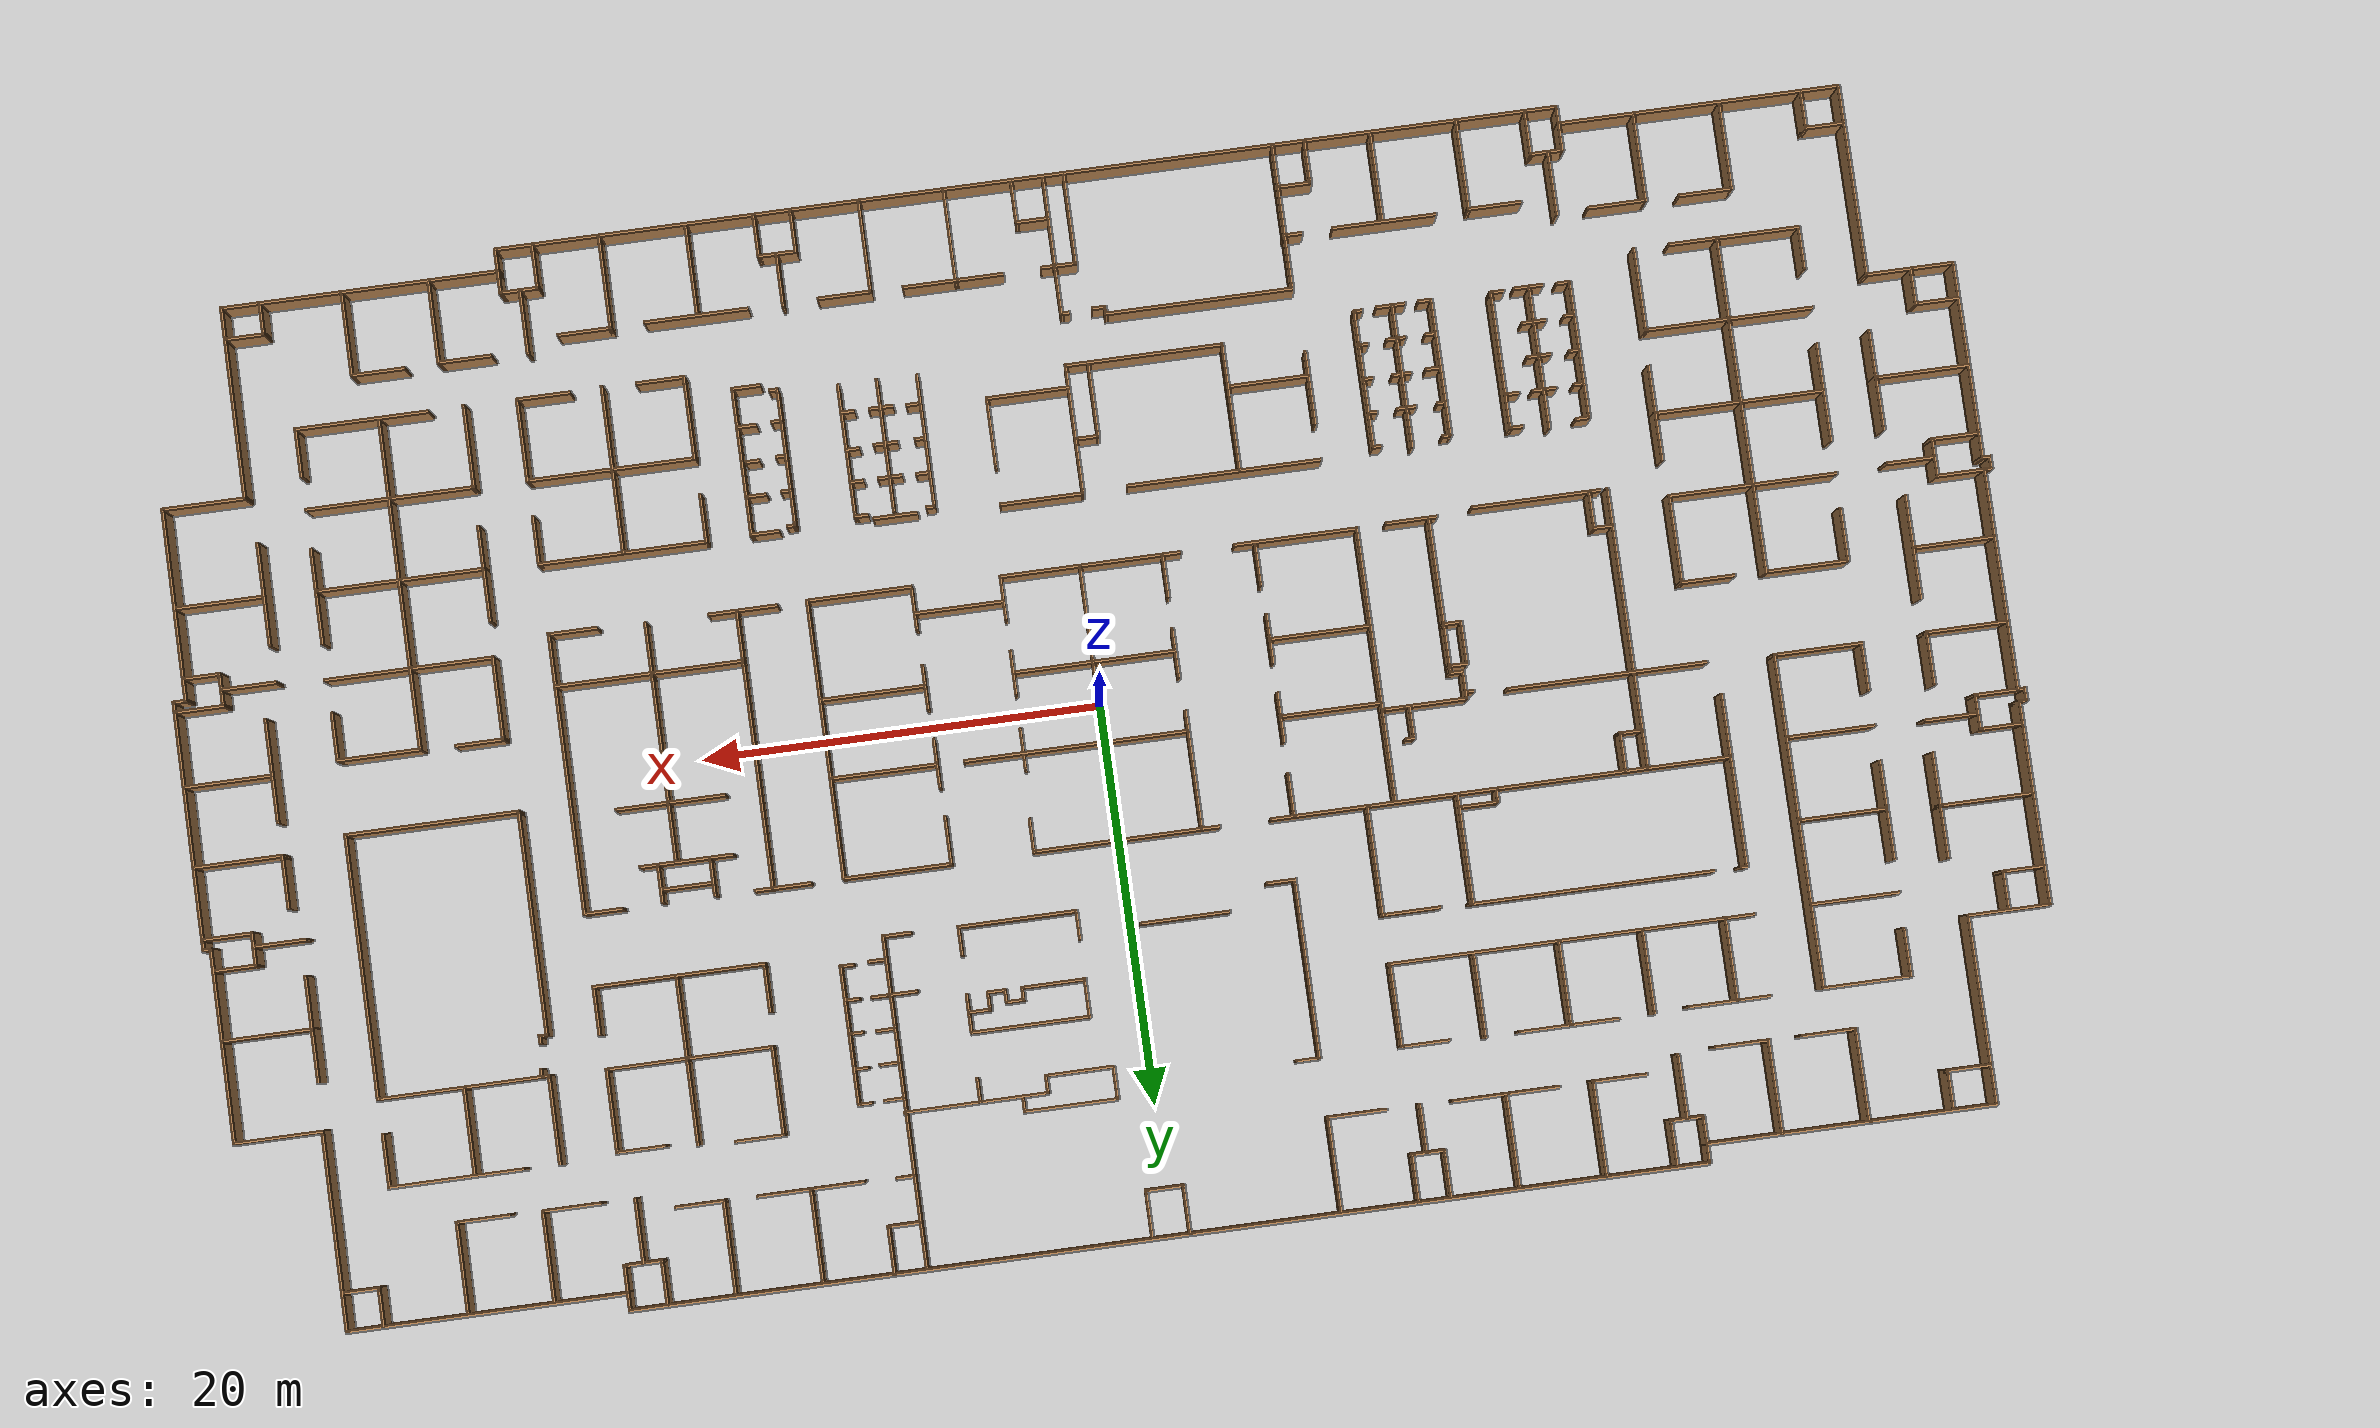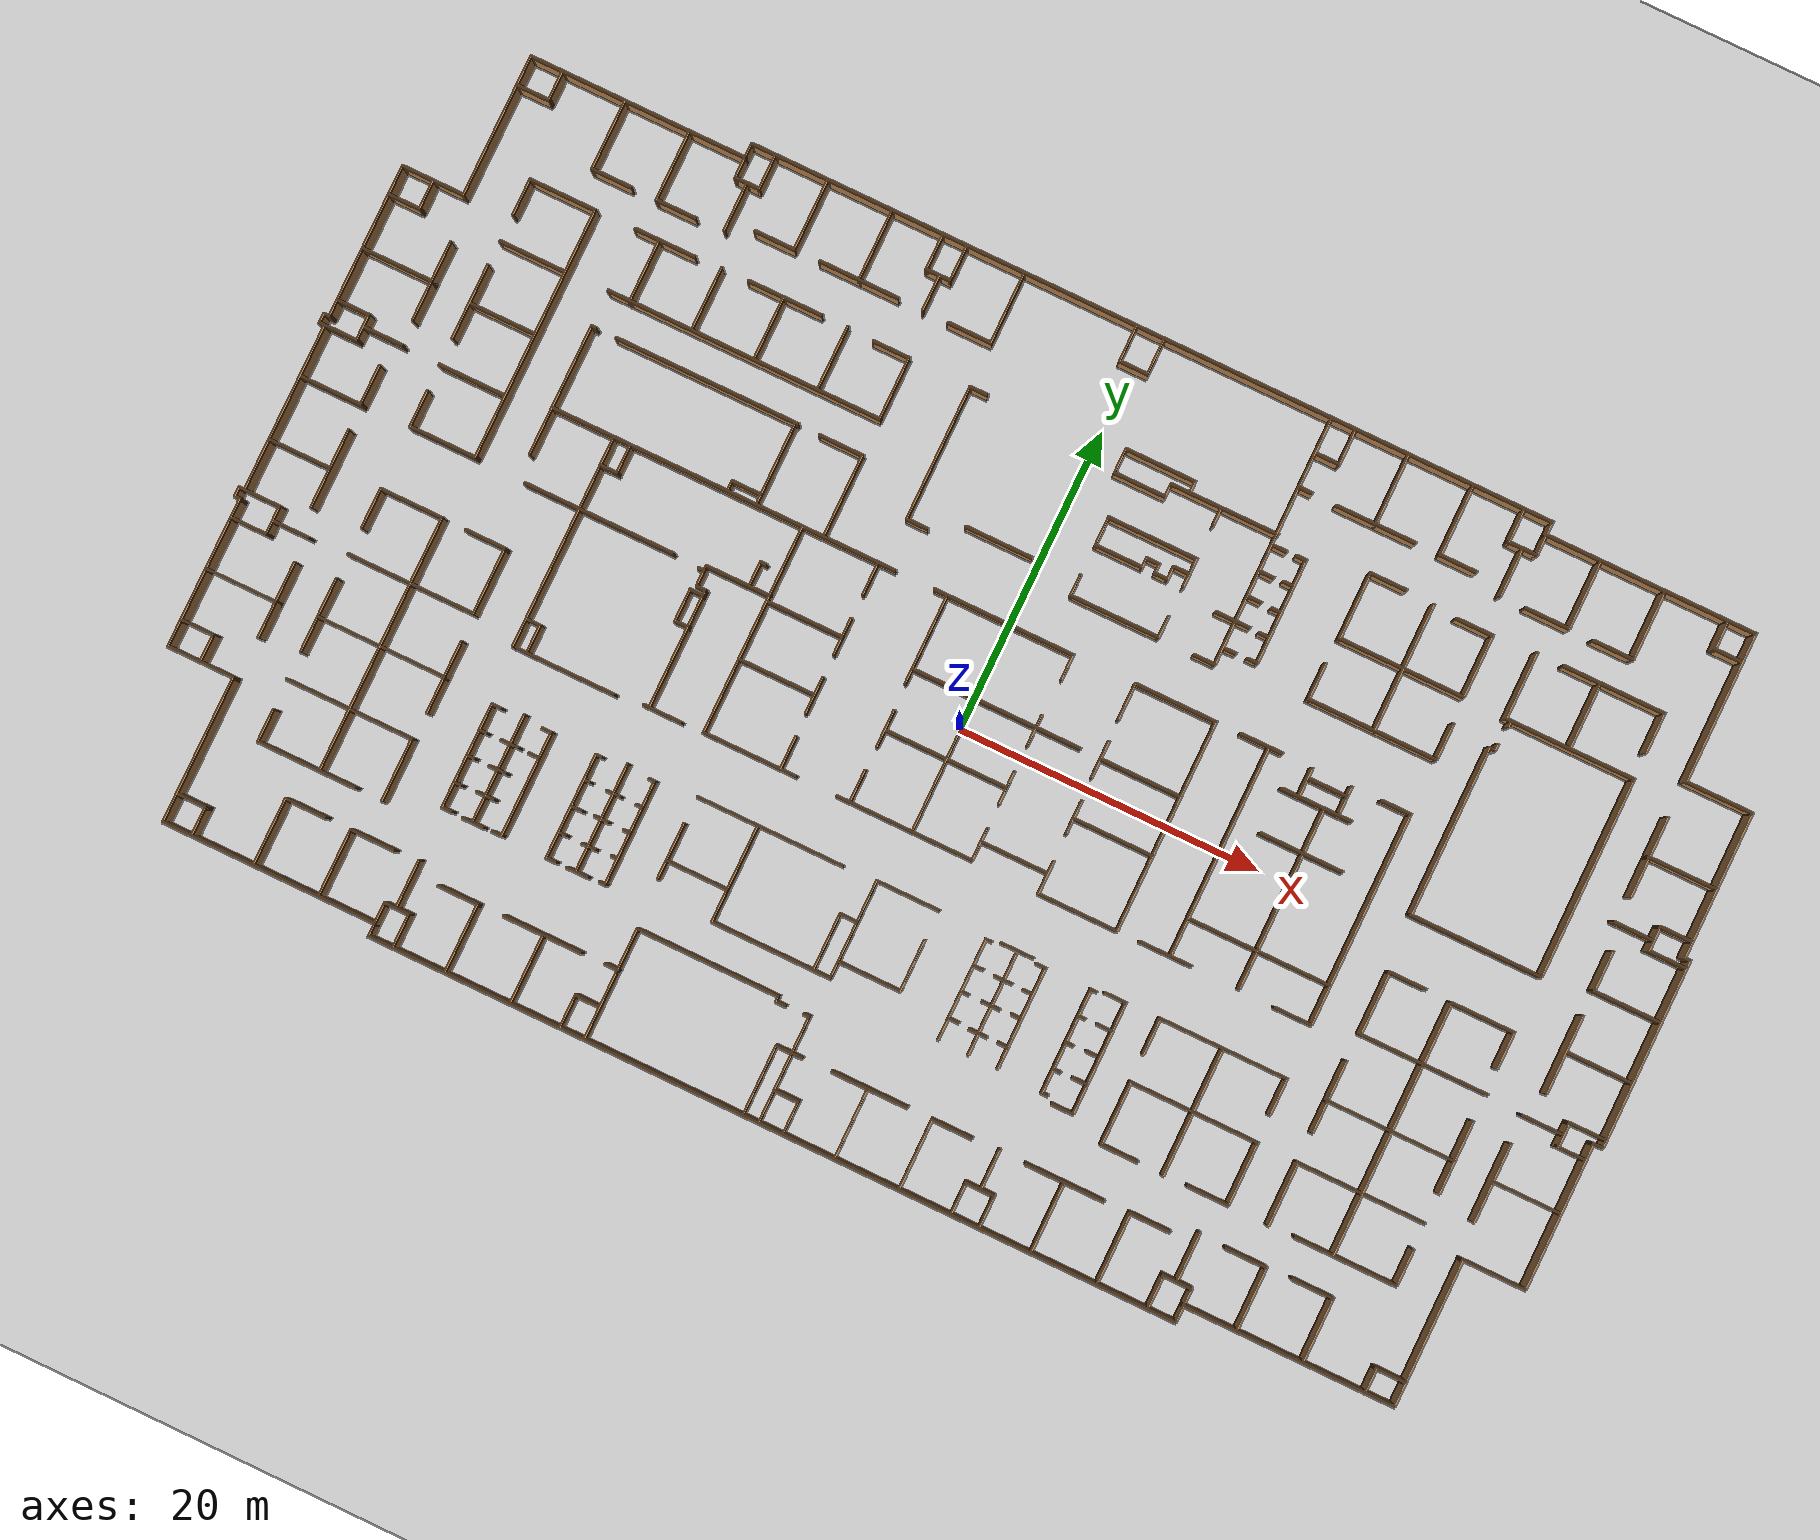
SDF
<sdf version="1.6">
 <world name="default">
  <light name="sun" type="directional">
   <pose>0 0 10 0 -0 0</pose>
   <diffuse>0.8 0.8 0.8 1</diffuse>
   <specular>0.1 0.1 0.1 1</specular>
   <attenuation>
    <range>1000</range>
    <constant>0.9</constant>
    <linear>0.01</linear>
    <quadratic>0.001</quadratic>
   </attenuation>
   <direction>-0.5 0.5 -1</direction>
  </light>
  <model name="ground_plane">
   <static>1</static>
   <link name="link">
    <collision name="collision">
     <geometry><plane><normal>0 0 1</normal><size>100 100</size></plane></geometry>
     <surface><friction><ode><mu>100</mu><mu2>50</mu2></ode></friction></surface>
    </collision>
    <visual name="visual">
     <cast_shadows>0</cast_shadows>
     <geometry><plane><normal>0 0 1</normal><size>100 100</size></plane></geometry>
     <material>
      <script><uri>file://media/materials/scripts/gazebo.material</uri><name>Gazebo/Grey</name></script>
     </material>
    </visual>
   </link>
  </model>
  <gravity>0 0 -9.8</gravity>
  <magnetic_field>6e-06 2.3e-05 -4.2e-05</magnetic_field>
  <atmosphere type="adiabatic"/>
  <physics name="default_physics" default="0" type="ode">
   <max_step_size>0.001</max_step_size>
   <real_time_factor>1</real_time_factor>
   <real_time_update_rate>1000</real_time_update_rate>
  </physics>
  <scene><ambient>0.4 0.4 0.4 1</ambient><background>0.7 0.7 0.7 1</background><shadows>1</shadows></scene>
  <spherical_coordinates>
   <surface_model>EARTH_WGS84</surface_model>
   <latitude_deg>0</latitude_deg>
   <longitude_deg>0</longitude_deg>
   <elevation>0</elevation>
   <heading_deg>0</heading_deg>
  </spherical_coordinates>
  <model name="floor_plan">
   <link name="Wall_10">
    <collision name="Wall_10_Collision">
     <geometry><box><size>10 0.15 2.5</size></box></geometry>
     <pose>0 0 1.25 0 -0 0</pose>
    </collision>
    <visual name="Wall_10_Visual">
     <pose>0 0 1.25 0 -0 0</pose>
     <geometry><box><size>10 0.15 2.5</size></box></geometry>
     <material>
      <script><uri>file://media/materials/scripts/gazebo.material</uri><name>Gazebo/Wood</name></script>
      <ambient>1 1 1 1</ambient>
     </material>
    </visual>
    <pose>40.65 20.6964 0 0 0 -1.5708</pose>
   </link>
   <link name="Wall_100">
    <collision name="Wall_100_Collision">
     <geometry><box><size>2.25 0.15 2.5</size></box></geometry>
     <pose>0 0 1.25 0 -0 0</pose>
    </collision>
    <visual name="Wall_100_Visual">
     <pose>0 0 1.25 0 -0 0</pose>
     <geometry><box><size>2.25 0.15 2.5</size></box></geometry>
     <material>
      <script><uri>file://media/materials/scripts/gazebo.material</uri><name>Gazebo/Wood</name></script>
      <ambient>1 1 1 1</ambient>
     </material>
    </visual>
    <pose>24.95 25.3214 0 0 -0 1.5708</pose>
   </link>
   <link name="Wall_102">
    <collision name="Wall_102_Collision">
     <geometry><box><size>3.25 0.15 2.5</size></box></geometry>
     <pose>0 0 1.25 0 -0 0</pose>
    </collision>
    <visual name="Wall_102_Visual">
     <pose>0 0 1.25 0 -0 0</pose>
     <geometry><box><size>3.25 0.15 2.5</size></box></geometry>
     <material>
      <script><uri>file://media/materials/scripts/gazebo.material</uri><name>Gazebo/Wood</name></script>
      <ambient>1 1 1 1</ambient>
     </material>
    </visual>
    <pose>25.8652 22.6731 0 0 0 -1.5708</pose>
   </link>
   <link name="Wall_104">
    <collision name="Wall_104_Collision">
     <geometry><box><size>3 0.15 2.5</size></box></geometry>
     <pose>0 0 1.25 0 -0 0</pose>
    </collision>
    <visual name="Wall_104_Visual">
     <pose>0 0 1.25 0 -0 0</pose>
     <geometry><box><size>3 0.15 2.5</size></box></geometry>
     <material>
      <script><uri>file://media/materials/scripts/gazebo.material</uri><name>Gazebo/Wood</name></script>
      <ambient>1 1 1 1</ambient>
     </material>
    </visual>
    <pose>28.998 21.0922 0 0 -0 0</pose>
   </link>
   <link name="Wall_105">
    <collision name="Wall_105_Collision">
     <geometry><box><size>4.65 0.15 2.5</size></box></geometry>
     <pose>0 0 1.25 0 -0 0</pose>
    </collision>
    <visual name="Wall_105_Visual">
     <pose>0 0 1.25 0 -0 0</pose>
     <geometry><box><size>4.65 0.15 2.5</size></box></geometry>
     <material>
      <script><uri>file://media/materials/scripts/gazebo.material</uri><name>Gazebo/Wood</name></script>
      <ambient>1 1 1 1</ambient>
     </material>
    </visual>
    <pose>30.423 23.3422 0 0 -0 1.5708</pose>
   </link>
   <link name="Wall_107">
    <collision name="Wall_107_Collision">
     <geometry><box><size>2.75 0.15 2.5</size></box></geometry>
     <pose>0 0 1.25 0 -0 0</pose>
    </collision>
    <visual name="Wall_107_Visual">
     <pose>0 0 1.25 0 -0 0</pose>
     <geometry><box><size>2.75 0.15 2.5</size></box></geometry>
     <material>
      <script><uri>file://media/materials/scripts/gazebo.material</uri><name>Gazebo/Wood</name></script>
      <ambient>1 1 1 1</ambient>
     </material>
    </visual>
    <pose>33.3717 21.0672 0 0 -0 0</pose>
   </link>
   <link name="Wall_108">
    <collision name="Wall_108_Collision">
     <geometry><box><size>4.65 0.15 2.5</size></box></geometry>
     <pose>0 0 1.25 0 -0 0</pose>
    </collision>
    <visual name="Wall_108_Visual">
     <pose>0 0 1.25 0 -0 0</pose>
     <geometry><box><size>4.65 0.15 2.5</size></box></geometry>
     <material>
      <script><uri>file://media/materials/scripts/gazebo.material</uri><name>Gazebo/Wood</name></script>
      <ambient>1 1 1 1</ambient>
     </material>
    </visual>
    <pose>34.6717 23.3172 0 0 -0 1.5708</pose>
   </link>
   <link name="Wall_11">
    <collision name="Wall_11_Collision">
     <geometry><box><size>4.5 0.15 2.5</size></box></geometry>
     <pose>0 0 1.25 0 -0 0</pose>
    </collision>
    <visual name="Wall_11_Visual">
     <pose>0 0 1.25 0 -0 0</pose>
     <geometry><box><size>4.5 0.15 2.5</size></box></geometry>
     <material>
      <script><uri>file://media/materials/scripts/gazebo.material</uri><name>Gazebo/Wood</name></script>
      <ambient>1 1 1 1</ambient>
     </material>
    </visual>
    <pose>42.825 15.7714 0 0 -0 0</pose>
   </link>
   <link name="Wall_110">
    <collision name="Wall_110_Collision">
     <geometry><box><size>2 0.15 2.5</size></box></geometry>
     <pose>0 0 1.25 0 -0 0</pose>
    </collision>
    <visual name="Wall_110_Visual">
     <pose>0 0 1.25 0 -0 0</pose>
     <geometry><box><size>2 0.15 2.5</size></box></geometry>
     <material>
      <script><uri>file://media/materials/scripts/gazebo.material</uri><name>Gazebo/Wood</name></script>
      <ambient>1 1 1 1</ambient>
     </material>
    </visual>
    <pose>38.8412 24.6589 0 0 0 -1.5708</pose>
   </link>
   <link name="Wall_111">
    <collision name="Wall_111_Collision">
     <geometry><box><size>1.9 0.15 2.5</size></box></geometry>
     <pose>0 0 1.25 0 -0 0</pose>
    </collision>
    <visual name="Wall_111_Visual">
     <pose>0 0 1.25 0 -0 0</pose>
     <geometry><box><size>1.9 0.15 2.5</size></box></geometry>
     <material>
      <script><uri>file://media/materials/scripts/gazebo.material</uri><name>Gazebo/Wood</name></script>
      <ambient>1 1 1 1</ambient>
     </material>
    </visual>
    <pose>39.7162 23.7339 0 0 -0 0</pose>
   </link>
   <link name="Wall_113">
    <collision name="Wall_113_Collision">
     <geometry><box><size>12 0.15 2.5</size></box></geometry>
     <pose>0 0 1.25 0 -0 0</pose>
    </collision>
    <visual name="Wall_113_Visual">
     <pose>0 0 1.25 0 -0 0</pose>
     <geometry><box><size>12 0.15 2.5</size></box></geometry>
     <material>
      <script><uri>file://media/materials/scripts/gazebo.material</uri><name>Gazebo/Wood</name></script>
      <ambient>1 1 1 1</ambient>
     </material>
    </visual>
    <pose>12.1534 15.9139 0 0 0 -1.5708</pose>
   </link>
   <link name="Wall_114">
    <collision name="Wall_114_Collision">
     <geometry><box><size>1.5 0.15 2.5</size></box></geometry>
     <pose>0 0 1.25 0 -0 0</pose>
    </collision>
    <visual name="Wall_114_Visual">
     <pose>0 0 1.25 0 -0 0</pose>
     <geometry><box><size>1.5 0.15 2.5</size></box></geometry>
     <material>
      <script><uri>file://media/materials/scripts/gazebo.material</uri><name>Gazebo/Wood</name></script>
      <ambient>1 1 1 1</ambient>
     </material>
    </visual>
    <pose>11.4784 9.98893 0 0 -0 3.14159</pose>
   </link>
   <link name="Wall_12">
    <collision name="Wall_12_Collision">
     <geometry><box><size>9.75 0.15 2.5</size></box></geometry>
     <pose>0 0 1.25 0 -0 0</pose>
    </collision>
    <visual name="Wall_12_Visual">
     <pose>0 0 1.25 0 -0 0</pose>
     <geometry><box><size>9.75 0.15 2.5</size></box></geometry>
     <material>
      <script><uri>file://media/materials/scripts/gazebo.material</uri><name>Gazebo/Wood</name></script>
      <ambient>1 1 1 1</ambient>
     </material>
    </visual>
    <pose>45 10.9714 0 0 0 -1.5708</pose>
   </link>
   <link name="Wall_120">
    <collision name="Wall_120_Collision">
     <geometry><box><size>1 0.15 2.5</size></box></geometry>
     <pose>0 0 1.25 0 -0 0</pose>
    </collision>
    <visual name="Wall_120_Visual">
     <pose>0 0 1.25 0 -0 0</pose>
     <geometry><box><size>1 0.15 2.5</size></box></geometry>
     <material>
      <script><uri>file://media/materials/scripts/gazebo.material</uri><name>Gazebo/Wood</name></script>
      <ambient>1 1 1 1</ambient>
     </material>
    </visual>
    <pose>12.6925 17.9951 0 0 -0 3.14159</pose>
   </link>
   <link name="Wall_124">
    <collision name="Wall_124_Collision">
     <geometry><box><size>1 0.15 2.5</size></box></geometry>
     <pose>0 0 1.25 0 -0 0</pose>
    </collision>
    <visual name="Wall_124_Visual">
     <pose>0 0 1.25 0 -0 0</pose>
     <geometry><box><size>1 0.15 2.5</size></box></geometry>
     <material>
      <script><uri>file://media/materials/scripts/gazebo.material</uri><name>Gazebo/Wood</name></script>
      <ambient>1 1 1 1</ambient>
     </material>
    </visual>
    <pose>12.669 16.2306 0 0 -0 3.14159</pose>
   </link>
   <link name="Wall_126">
    <collision name="Wall_126_Collision">
     <geometry><box><size>1 0.15 2.5</size></box></geometry>
     <pose>0 0 1.25 0 -0 0</pose>
    </collision>
    <visual name="Wall_126_Visual">
     <pose>0 0 1.25 0 -0 0</pose>
     <geometry><box><size>1 0.15 2.5</size></box></geometry>
     <material>
      <script><uri>file://media/materials/scripts/gazebo.material</uri><name>Gazebo/Wood</name></script>
      <ambient>1 1 1 1</ambient>
     </material>
    </visual>
    <pose>12.6219 14.5602 0 0 -0 3.14159</pose>
   </link>
   <link name="Wall_128">
    <collision name="Wall_128_Collision">
     <geometry><box><size>1 0.15 2.5</size></box></geometry>
     <pose>0 0 1.25 0 -0 0</pose>
    </collision>
    <visual name="Wall_128_Visual">
     <pose>0 0 1.25 0 -0 0</pose>
     <geometry><box><size>1 0.15 2.5</size></box></geometry>
     <material>
      <script><uri>file://media/materials/scripts/gazebo.material</uri><name>Gazebo/Wood</name></script>
      <ambient>1 1 1 1</ambient>
     </material>
    </visual>
    <pose>12.6454 12.8898 0 0 -0 3.14159</pose>
   </link>
   <link name="Wall_13">
    <collision name="Wall_13_Collision">
     <geometry><box><size>0.5 0.15 2.5</size></box></geometry>
     <pose>0 0 1.25 0 -0 0</pose>
    </collision>
    <visual name="Wall_13_Visual">
     <pose>0 0 1.25 0 -0 0</pose>
     <geometry><box><size>0.5 0.15 2.5</size></box></geometry>
     <material>
      <script><uri>file://media/materials/scripts/gazebo.material</uri><name>Gazebo/Wood</name></script>
      <ambient>1 1 1 1</ambient>
     </material>
    </visual>
    <pose>45.175 6.1714 0 0 -0 0</pose>
   </link>
   <link name="Wall_130">
    <collision name="Wall_130_Collision">
     <geometry><box><size>1 0.15 2.5</size></box></geometry>
     <pose>0 0 1.25 0 -0 0</pose>
    </collision>
    <visual name="Wall_130_Visual">
     <pose>0 0 1.25 0 -0 0</pose>
     <geometry><box><size>1 0.15 2.5</size></box></geometry>
     <material>
      <script><uri>file://media/materials/scripts/gazebo.material</uri><name>Gazebo/Wood</name></script>
      <ambient>1 1 1 1</ambient>
     </material>
    </visual>
    <pose>12.5749 11.1253 0 0 -0 3.14159</pose>
   </link>
   <link name="Wall_132">
    <collision name="Wall_132_Collision">
     <geometry><box><size>1.5 0.15 2.5</size></box></geometry>
     <pose>0 0 1.25 0 -0 0</pose>
    </collision>
    <visual name="Wall_132_Visual">
     <pose>0 0 1.25 0 -0 0</pose>
     <geometry><box><size>1.5 0.15 2.5</size></box></geometry>
     <material>
      <script><uri>file://media/materials/scripts/gazebo.material</uri><name>Gazebo/Wood</name></script>
      <ambient>1 1 1 1</ambient>
     </material>
    </visual>
    <pose>2.5583 10.705 0 0 0 -1.5708</pose>
   </link>
   <link name="Wall_133">
    <collision name="Wall_133_Collision">
     <geometry><box><size>6 0.15 2.5</size></box></geometry>
     <pose>0 0 1.25 0 -0 0</pose>
    </collision>
    <visual name="Wall_133_Visual">
     <pose>0 0 1.25 0 -0 0</pose>
     <geometry><box><size>6 0.15 2.5</size></box></geometry>
     <material>
      <script><uri>file://media/materials/scripts/gazebo.material</uri><name>Gazebo/Wood</name></script>
      <ambient>1 1 1 1</ambient>
     </material>
    </visual>
    <pose>5.4833 10.03 0 0 -0 0</pose>
   </link>
   <link name="Wall_134">
    <collision name="Wall_134_Collision">
     <geometry><box><size>1.5 0.15 2.5</size></box></geometry>
     <pose>0 0 1.25 0 -0 0</pose>
    </collision>
    <visual name="Wall_134_Visual">
     <pose>0 0 1.25 0 -0 0</pose>
     <geometry><box><size>1.5 0.15 2.5</size></box></geometry>
     <material>
      <script><uri>file://media/materials/scripts/gazebo.material</uri><name>Gazebo/Wood</name></script>
      <ambient>1 1 1 1</ambient>
     </material>
    </visual>
    <pose>8.4083 10.705 0 0 -0 1.5708</pose>
   </link>
   <link name="Wall_136">
    <collision name="Wall_136_Collision">
     <geometry><box><size>4.5 0.15 2.5</size></box></geometry>
     <pose>0 0 1.25 0 -0 0</pose>
    </collision>
    <visual name="Wall_136_Visual">
     <pose>0 0 1.25 0 -0 0</pose>
     <geometry><box><size>4.5 0.15 2.5</size></box></geometry>
     <material>
      <script><uri>file://media/materials/scripts/gazebo.material</uri><name>Gazebo/Wood</name></script>
      <ambient>1 1 1 1</ambient>
     </material>
    </visual>
    <pose>-2.72059 11.0775 0 0 -0 0</pose>
   </link>
   <link name="Wall_138">
    <collision name="Wall_138_Collision">
     <geometry><box><size>1.25 0.15 2.5</size></box></geometry>
     <pose>0 0 1.25 0 -0 0</pose>
    </collision>
    <visual name="Wall_138_Visual">
     <pose>0 0 1.25 0 -0 0</pose>
     <geometry><box><size>1.25 0.15 2.5</size></box></geometry>
     <material>
      <script><uri>file://media/materials/scripts/gazebo.material</uri><name>Gazebo/Wood</name></script>
      <ambient>1 1 1 1</ambient>
     </material>
    </visual>
    <pose>-7.75979 18.8072 0 0 -0 3.14159</pose>
   </link>
   <link name="Wall_139">
    <collision name="Wall_139_Collision">
     <geometry><box><size>9 0.15 2.5</size></box></geometry>
     <pose>0 0 1.25 0 -0 0</pose>
    </collision>
    <visual name="Wall_139_Visual">
     <pose>0 0 1.25 0 -0 0</pose>
     <geometry><box><size>9 0.15 2.5</size></box></geometry>
     <material>
      <script><uri>file://media/materials/scripts/gazebo.material</uri><name>Gazebo/Wood</name></script>
      <ambient>1 1 1 1</ambient>
     </material>
    </visual>
    <pose>-8.30979 14.3822 0 0 0 -1.5708</pose>
   </link>
   <link name="Wall_14">
    <collision name="Wall_14_Collision">
     <geometry><box><size>12.5 0.15 2.5</size></box></geometry>
     <pose>0 0 1.25 0 -0 0</pose>
    </collision>
    <visual name="Wall_14_Visual">
     <pose>0 0 1.25 0 -0 0</pose>
     <geometry><box><size>12.5 0.15 2.5</size></box></geometry>
     <material>
      <script><uri>file://media/materials/scripts/gazebo.material</uri><name>Gazebo/Wood</name></script>
      <ambient>1 1 1 1</ambient>
     </material>
    </visual>
    <pose>45.35 -0.003604 0 0 0 -1.5708</pose>
   </link>
   <link name="Wall_140">
    <collision name="Wall_140_Collision">
     <geometry><box><size>1.5 0.15 2.5</size></box></geometry>
     <pose>0 0 1.25 0 -0 0</pose>
    </collision>
    <visual name="Wall_140_Visual">
     <pose>0 0 1.25 0 -0 0</pose>
     <geometry><box><size>1.5 0.15 2.5</size></box></geometry>
     <material>
      <script><uri>file://media/materials/scripts/gazebo.material</uri><name>Gazebo/Wood</name></script>
      <ambient>1 1 1 1</ambient>
     </material>
    </visual>
    <pose>-7.63479 9.95716 0 0 -0 0</pose>
   </link>
   <link name="Wall_142">
    <collision name="Wall_142_Collision">
     <geometry><box><size>0.75 0.15 2.5</size></box></geometry>
     <pose>0 0 1.25 0 -0 0</pose>
    </collision>
    <visual name="Wall_142_Visual">
     <pose>0 0 1.25 0 -0 0</pose>
     <geometry><box><size>0.75 0.15 2.5</size></box></geometry>
     <material>
      <script><uri>file://media/materials/scripts/gazebo.material</uri><name>Gazebo/Wood</name></script>
      <ambient>1 1 1 1</ambient>
     </material>
    </visual>
    <pose>14.1127 18.0225 0 0 -0 0</pose>
   </link>
   <link name="Wall_143">
    <collision name="Wall_143_Collision">
     <geometry><box><size>7 0.15 2.5</size></box></geometry>
     <pose>0 0 1.25 0 -0 0</pose>
    </collision>
    <visual name="Wall_143_Visual">
     <pose>0 0 1.25 0 -0 0</pose>
     <geometry><box><size>7 0.15 2.5</size></box></geometry>
     <material>
      <script><uri>file://media/materials/scripts/gazebo.material</uri><name>Gazebo/Wood</name></script>
      <ambient>1 1 1 1</ambient>
     </material>
    </visual>
    <pose>14.4127 14.5975 0 0 0 -1.5708</pose>
   </link>
   <link name="Wall_144">
    <collision name="Wall_144_Collision">
     <geometry><box><size>0.75 0.15 2.5</size></box></geometry>
     <pose>0 0 1.25 0 -0 0</pose>
    </collision>
    <visual name="Wall_144_Visual">
     <pose>0 0 1.25 0 -0 0</pose>
     <geometry><box><size>0.75 0.15 2.5</size></box></geometry>
     <material>
      <script><uri>file://media/materials/scripts/gazebo.material</uri><name>Gazebo/Wood</name></script>
      <ambient>1 1 1 1</ambient>
     </material>
    </visual>
    <pose>14.1127 11.1725 0 0 -0 3.14159</pose>
   </link>
   <link name="Wall_148">
    <collision name="Wall_148_Collision">
     <geometry><box><size>0.75 0.15 2.5</size></box></geometry>
     <pose>0 0 1.25 0 -0 0</pose>
    </collision>
    <visual name="Wall_148_Visual">
     <pose>0 0 1.25 0 -0 0</pose>
     <geometry><box><size>0.75 0.15 2.5</size></box></geometry>
     <material>
      <script><uri>file://media/materials/scripts/gazebo.material</uri><name>Gazebo/Wood</name></script>
      <ambient>1 1 1 1</ambient>
     </material>
    </visual>
    <pose>14.0607 16.2859 0 0 -0 3.14159</pose>
   </link>
   <link name="Wall_15">
    <collision name="Wall_15_Collision">
     <geometry><box><size>0.75 0.15 2.5</size></box></geometry>
     <pose>0 0 1.25 0 -0 0</pose>
    </collision>
    <visual name="Wall_15_Visual">
     <pose>0 0 1.25 0 -0 0</pose>
     <geometry><box><size>0.75 0.15 2.5</size></box></geometry>
     <material>
      <script><uri>file://media/materials/scripts/gazebo.material</uri><name>Gazebo/Wood</name></script>
      <ambient>1 1 1 1</ambient>
     </material>
    </visual>
    <pose>45.05 -6.1786 0 0 -0 3.14159</pose>
   </link>
   <link name="Wall_150">
    <collision name="Wall_150_Collision">
     <geometry><box><size>0.75 0.15 2.5</size></box></geometry>
     <pose>0 0 1.25 0 -0 0</pose>
    </collision>
    <visual name="Wall_150_Visual">
     <pose>0 0 1.25 0 -0 0</pose>
     <geometry><box><size>0.75 0.15 2.5</size></box></geometry>
     <material>
      <script><uri>file://media/materials/scripts/gazebo.material</uri><name>Gazebo/Wood</name></script>
      <ambient>1 1 1 1</ambient>
     </material>
    </visual>
    <pose>14.1016 14.5265 0 0 -0 3.14159</pose>
   </link>
   <link name="Wall_152">
    <collision name="Wall_152_Collision">
     <geometry><box><size>0.75 0.15 2.5</size></box></geometry>
     <pose>0 0 1.25 0 -0 0</pose>
    </collision>
    <visual name="Wall_152_Visual">
     <pose>0 0 1.25 0 -0 0</pose>
     <geometry><box><size>0.75 0.15 2.5</size></box></geometry>
     <material>
      <script><uri>file://media/materials/scripts/gazebo.material</uri><name>Gazebo/Wood</name></script>
      <ambient>1 1 1 1</ambient>
     </material>
    </visual>
    <pose>14.0607 12.8694 0 0 -0 3.14159</pose>
   </link>
   <link name="Wall_16">
    <collision name="Wall_16_Collision">
     <geometry><box><size>9.75 0.15 2.5</size></box></geometry>
     <pose>0 0 1.25 0 -0 0</pose>
    </collision>
    <visual name="Wall_16_Visual">
     <pose>0 0 1.25 0 -0 0</pose>
     <geometry><box><size>9.75 0.15 2.5</size></box></geometry>
     <material>
      <script><uri>file://media/materials/scripts/gazebo.material</uri><name>Gazebo/Wood</name></script>
      <ambient>1 1 1 1</ambient>
     </material>
    </visual>
    <pose>44.75 -10.9786 0 0 0 -1.5708</pose>
   </link>
   <link name="Wall_17">
    <collision name="Wall_17_Collision">
     <geometry><box><size>4.25 0.15 2.5</size></box></geometry>
     <pose>0 0 1.25 0 -0 0</pose>
    </collision>
    <visual name="Wall_17_Visual">
     <pose>0 0 1.25 0 -0 0</pose>
     <geometry><box><size>4.25 0.15 2.5</size></box></geometry>
     <material>
      <script><uri>file://media/materials/scripts/gazebo.material</uri><name>Gazebo/Wood</name></script>
      <ambient>1 1 1 1</ambient>
     </material>
    </visual>
    <pose>42.7 -15.7786 0 0 -0 3.14159</pose>
   </link>
   <link name="Wall_171">
    <collision name="Wall_171_Collision">
     <geometry><box><size>8.5 0.15 2.5</size></box></geometry>
     <pose>0 0 1.25 0 -0 0</pose>
    </collision>
    <visual name="Wall_171_Visual">
     <pose>0 0 1.25 0 -0 0</pose>
     <geometry><box><size>8.5 0.15 2.5</size></box></geometry>
     <material>
      <script><uri>file://media/materials/scripts/gazebo.material</uri><name>Gazebo/Wood</name></script>
      <ambient>1 1 1 1</ambient>
     </material>
    </visual>
    <pose>22.4756 14.7101 0 0 0 -1.5708</pose>
   </link>
   <link name="Wall_172">
    <collision name="Wall_172_Collision">
     <geometry><box><size>4.5 0.15 2.5</size></box></geometry>
     <pose>0 0 1.25 0 -0 0</pose>
    </collision>
    <visual name="Wall_172_Visual">
     <pose>0 0 1.25 0 -0 0</pose>
     <geometry><box><size>4.5 0.15 2.5</size></box></geometry>
     <material>
      <script><uri>file://media/materials/scripts/gazebo.material</uri><name>Gazebo/Wood</name></script>
      <ambient>1 1 1 1</ambient>
     </material>
    </visual>
    <pose>20.3006 10.5351 0 0 -0 3.14159</pose>
   </link>
   <link name="Wall_173">
    <collision name="Wall_173_Collision">
     <geometry><box><size>2.5 0.15 2.5</size></box></geometry>
     <pose>0 0 1.25 0 -0 0</pose>
    </collision>
    <visual name="Wall_173_Visual">
     <pose>0 0 1.25 0 -0 0</pose>
     <geometry><box><size>2.5 0.15 2.5</size></box></geometry>
     <material>
      <script><uri>file://media/materials/scripts/gazebo.material</uri><name>Gazebo/Wood</name></script>
      <ambient>1 1 1 1</ambient>
     </material>
    </visual>
    <pose>18.1256 11.7101 0 0 -0 1.5708</pose>
   </link>
   <link name="Wall_175">
    <collision name="Wall_175_Collision">
     <geometry><box><size>4.25 0.15 2.5</size></box></geometry>
     <pose>0 0 1.25 0 -0 0</pose>
    </collision>
    <visual name="Wall_175_Visual">
     <pose>0 0 1.25 0 -0 0</pose>
     <geometry><box><size>4.25 0.15 2.5</size></box></geometry>
     <material>
      <script><uri>file://media/materials/scripts/gazebo.material</uri><name>Gazebo/Wood</name></script>
      <ambient>1 1 1 1</ambient>
     </material>
    </visual>
    <pose>20.3031 14.6405 0 0 -0 3.14159</pose>
   </link>
   <link name="Wall_176">
    <collision name="Wall_176_Collision">
     <geometry><box><size>4.5 0.15 2.5</size></box></geometry>
     <pose>0 0 1.25 0 -0 0</pose>
    </collision>
    <visual name="Wall_176_Visual">
     <pose>0 0 1.25 0 -0 0</pose>
     <geometry><box><size>4.5 0.15 2.5</size></box></geometry>
     <material>
      <script><uri>file://media/materials/scripts/gazebo.material</uri><name>Gazebo/Wood</name></script>
      <ambient>1 1 1 1</ambient>
     </material>
    </visual>
    <pose>18.2532 16.8155 0 0 -0 1.5708</pose>
   </link>
   <link name="Wall_178">
    <collision name="Wall_178_Collision">
     <geometry><box><size>4.25 0.15 2.5</size></box></geometry>
     <pose>0 0 1.25 0 -0 0</pose>
    </collision>
    <visual name="Wall_178_Visual">
     <pose>0 0 1.25 0 -0 0</pose>
     <geometry><box><size>4.25 0.15 2.5</size></box></geometry>
     <material>
      <script><uri>file://media/materials/scripts/gazebo.material</uri><name>Gazebo/Wood</name></script>
      <ambient>1 1 1 1</ambient>
     </material>
    </visual>
    <pose>24.5256 10.5351 0 0 -0 0</pose>
   </link>
   <link name="Wall_179">
    <collision name="Wall_179_Collision">
     <geometry><box><size>2.5 0.15 2.5</size></box></geometry>
     <pose>0 0 1.25 0 -0 0</pose>
    </collision>
    <visual name="Wall_179_Visual">
     <pose>0 0 1.25 0 -0 0</pose>
     <geometry><box><size>2.5 0.15 2.5</size></box></geometry>
     <material>
      <script><uri>file://media/materials/scripts/gazebo.material</uri><name>Gazebo/Wood</name></script>
      <ambient>1 1 1 1</ambient>
     </material>
    </visual>
    <pose>26.5756 11.7101 0 0 -0 1.5708</pose>
   </link>
   <link name="Wall_18">
    <collision name="Wall_18_Collision">
     <geometry><box><size>9.75 0.15 2.5</size></box></geometry>
     <pose>0 0 1.25 0 -0 0</pose>
    </collision>
    <visual name="Wall_18_Visual">
     <pose>0 0 1.25 0 -0 0</pose>
     <geometry><box><size>9.75 0.15 2.5</size></box></geometry>
     <material>
      <script><uri>file://media/materials/scripts/gazebo.material</uri><name>Gazebo/Wood</name></script>
      <ambient>1 1 1 1</ambient>
     </material>
    </visual>
    <pose>40.65 -20.5786 0 0 0 -1.5708</pose>
   </link>
   <link name="Wall_181">
    <collision name="Wall_181_Collision">
     <geometry><box><size>4.25 0.15 2.5</size></box></geometry>
     <pose>0 0 1.25 0 -0 0</pose>
    </collision>
    <visual name="Wall_181_Visual">
     <pose>0 0 1.25 0 -0 0</pose>
     <geometry><box><size>4.25 0.15 2.5</size></box></geometry>
     <material>
      <script><uri>file://media/materials/scripts/gazebo.material</uri><name>Gazebo/Wood</name></script>
      <ambient>1 1 1 1</ambient>
     </material>
    </visual>
    <pose>24.4032 14.6405 0 0 -0 0</pose>
   </link>
   <link name="Wall_182">
    <collision name="Wall_182_Collision">
     <geometry><box><size>4.25 0.15 2.5</size></box></geometry>
     <pose>0 0 1.25 0 -0 0</pose>
    </collision>
    <visual name="Wall_182_Visual">
     <pose>0 0 1.25 0 -0 0</pose>
     <geometry><box><size>4.25 0.15 2.5</size></box></geometry>
     <material>
      <script><uri>file://media/materials/scripts/gazebo.material</uri><name>Gazebo/Wood</name></script>
      <ambient>1 1 1 1</ambient>
     </material>
    </visual>
    <pose>26.4532 16.6905 0 0 -0 1.5708</pose>
   </link>
   <link name="Wall_183">
    <collision name="Wall_183_Collision">
     <geometry><box><size>2.5 0.15 2.5</size></box></geometry>
     <pose>0 0 1.25 0 -0 0</pose>
    </collision>
    <visual name="Wall_183_Visual">
     <pose>0 0 1.25 0 -0 0</pose>
     <geometry><box><size>2.5 0.15 2.5</size></box></geometry>
     <material>
      <script><uri>file://media/materials/scripts/gazebo.material</uri><name>Gazebo/Wood</name></script>
      <ambient>1 1 1 1</ambient>
     </material>
    </visual>
    <pose>25.2782 18.7405 0 0 -0 3.14159</pose>
   </link>
   <link name="Wall_185">
    <collision name="Wall_185_Collision">
     <geometry><box><size>2.5 0.15 2.5</size></box></geometry>
     <pose>0 0 1.25 0 -0 0</pose>
    </collision>
    <visual name="Wall_185_Visual">
     <pose>0 0 1.25 0 -0 0</pose>
     <geometry><box><size>2.5 0.15 2.5</size></box></geometry>
     <material>
      <script><uri>file://media/materials/scripts/gazebo.material</uri><name>Gazebo/Wood</name></script>
      <ambient>1 1 1 1</ambient>
     </material>
    </visual>
    <pose>19.4281 18.9905 0 0 -0 0</pose>
   </link>
   <link name="Wall_187">
    <collision name="Wall_187_Collision">
     <geometry><box><size>4.5 0.15 2.5</size></box></geometry>
     <pose>0 0 1.25 0 -0 0</pose>
    </collision>
    <visual name="Wall_187_Visual">
     <pose>0 0 1.25 0 -0 0</pose>
     <geometry><box><size>4.5 0.15 2.5</size></box></geometry>
     <material>
      <script><uri>file://media/materials/scripts/gazebo.material</uri><name>Gazebo/Wood</name></script>
      <ambient>1 1 1 1</ambient>
     </material>
    </visual>
    <pose>29.3003 16.7441 0 0 0 -1.5708</pose>
   </link>
   <link name="Wall_19">
    <collision name="Wall_19_Collision">
     <geometry><box><size>14 0.15 2.5</size></box></geometry>
     <pose>0 0 1.25 0 -0 0</pose>
    </collision>
    <visual name="Wall_19_Visual">
     <pose>0 0 1.25 0 -0 0</pose>
     <geometry><box><size>14 0.15 2.5</size></box></geometry>
     <material>
      <script><uri>file://media/materials/scripts/gazebo.material</uri><name>Gazebo/Wood</name></script>
      <ambient>1 1 1 1</ambient>
     </material>
    </visual>
    <pose>33.725 -25.3786 0 0 -0 3.14159</pose>
   </link>
   <link name="Wall_190">
    <collision name="Wall_190_Collision">
     <geometry><box><size>0.5 0.15 2.5</size></box></geometry>
     <pose>0 0 1.25 0 -0 0</pose>
    </collision>
    <visual name="Wall_190_Visual">
     <pose>0 0 1.25 0 -0 0</pose>
     <geometry><box><size>0.5 0.15 2.5</size></box></geometry>
     <material>
      <script><uri>file://media/materials/scripts/gazebo.material</uri><name>Gazebo/Wood</name></script>
      <ambient>1 1 1 1</ambient>
     </material>
    </visual>
    <pose>29.4753 14.5691 0 0 -0 0</pose>
   </link>
   <link name="Wall_191">
    <collision name="Wall_191_Collision">
     <geometry><box><size>0.5 0.15 2.5</size></box></geometry>
     <pose>0 0 1.25 0 -0 0</pose>
    </collision>
    <visual name="Wall_191_Visual">
     <pose>0 0 1.25 0 -0 0</pose>
     <geometry><box><size>0.5 0.15 2.5</size></box></geometry>
     <material>
      <script><uri>file://media/materials/scripts/gazebo.material</uri><name>Gazebo/Wood</name></script>
      <ambient>1 1 1 1</ambient>
     </material>
    </visual>
    <pose>29.6503 14.3941 0 0 0 -1.5708</pose>
   </link>
   <link name="Wall_193">
    <collision name="Wall_193_Collision">
     <geometry><box><size>6.75 0.15 2.5</size></box></geometry>
     <pose>0 0 1.25 0 -0 0</pose>
    </collision>
    <visual name="Wall_193_Visual">
     <pose>0 0 1.25 0 -0 0</pose>
     <geometry><box><size>6.75 0.15 2.5</size></box></geometry>
     <material>
      <script><uri>file://media/materials/scripts/gazebo.material</uri><name>Gazebo/Wood</name></script>
      <ambient>1 1 1 1</ambient>
     </material>
    </visual>
    <pose>34.4228 18.9244 0 0 -0 0</pose>
   </link>
   <link name="Wall_194">
    <collision name="Wall_194_Collision">
     <geometry><box><size>2.75 0.15 2.5</size></box></geometry>
     <pose>0 0 1.25 0 -0 0</pose>
    </collision>
    <visual name="Wall_194_Visual">
     <pose>0 0 1.25 0 -0 0</pose>
     <geometry><box><size>2.75 0.15 2.5</size></box></geometry>
     <material>
      <script><uri>file://media/materials/scripts/gazebo.material</uri><name>Gazebo/Wood</name></script>
      <ambient>1 1 1 1</ambient>
     </material>
    </visual>
    <pose>37.7228 17.6244 0 0 0 -1.5708</pose>
   </link>
   <link name="Wall_196">
    <collision name="Wall_196_Collision">
     <geometry><box><size>8.25 0.15 2.5</size></box></geometry>
     <pose>0 0 1.25 0 -0 0</pose>
    </collision>
    <visual name="Wall_196_Visual">
     <pose>0 0 1.25 0 -0 0</pose>
     <geometry><box><size>8.25 0.15 2.5</size></box></geometry>
     <material>
      <script><uri>file://media/materials/scripts/gazebo.material</uri><name>Gazebo/Wood</name></script>
      <ambient>1 1 1 1</ambient>
     </material>
    </visual>
    <pose>33.7003 14.5691 0 0 -0 0</pose>
   </link>
   <link name="Wall_197">
    <collision name="Wall_197_Collision">
     <geometry><box><size>13.25 0.15 2.5</size></box></geometry>
     <pose>0 0 1.25 0 -0 0</pose>
    </collision>
    <visual name="Wall_197_Visual">
     <pose>0 0 1.25 0 -0 0</pose>
     <geometry><box><size>13.25 0.15 2.5</size></box></geometry>
     <material>
      <script><uri>file://media/materials/scripts/gazebo.material</uri><name>Gazebo/Wood</name></script>
      <ambient>1 1 1 1</ambient>
     </material>
    </visual>
    <pose>37.7503 8.01909 0 0 0 -1.5708</pose>
   </link>
   <link name="Wall_198">
    <collision name="Wall_198_Collision">
     <geometry><box><size>8.75 0.15 2.5</size></box></geometry>
     <pose>0 0 1.25 0 -0 0</pose>
    </collision>
    <visual name="Wall_198_Visual">
     <pose>0 0 1.25 0 -0 0</pose>
     <geometry><box><size>8.75 0.15 2.5</size></box></geometry>
     <material>
      <script><uri>file://media/materials/scripts/gazebo.material</uri><name>Gazebo/Wood</name></script>
      <ambient>1 1 1 1</ambient>
     </material>
    </visual>
    <pose>33.4503 1.46909 0 0 -0 3.14159</pose>
   </link>
   <link name="Wall_199">
    <collision name="Wall_199_Collision">
     <geometry><box><size>11.25 0.15 2.5</size></box></geometry>
     <pose>0 0 1.25 0 -0 0</pose>
    </collision>
    <visual name="Wall_199_Visual">
     <pose>0 0 1.25 0 -0 0</pose>
     <geometry><box><size>11.25 0.15 2.5</size></box></geometry>
     <material>
      <script><uri>file://media/materials/scripts/gazebo.material</uri><name>Gazebo/Wood</name></script>
      <ambient>1 1 1 1</ambient>
     </material>
    </visual>
    <pose>29.1503 7.01909 0 0 -0 1.5708</pose>
   </link>
   <link name="Wall_20">
    <collision name="Wall_20_Collision">
     <geometry><box><size>1.25 0.15 2.5</size></box></geometry>
     <pose>0 0 1.25 0 -0 0</pose>
    </collision>
    <visual name="Wall_20_Visual">
     <pose>0 0 1.25 0 -0 0</pose>
     <geometry><box><size>1.25 0.15 2.5</size></box></geometry>
     <material>
      <script><uri>file://media/materials/scripts/gazebo.material</uri><name>Gazebo/Wood</name></script>
      <ambient>1 1 1 1</ambient>
     </material>
    </visual>
    <pose>26.8 -25.9286 0 0 0 -1.5708</pose>
   </link>
   <link name="Wall_200">
    <collision name="Wall_200_Collision">
     <geometry><box><size>0.5 0.15 2.5</size></box></geometry>
     <pose>0 0 1.25 0 -0 0</pose>
    </collision>
    <visual name="Wall_200_Visual">
     <pose>0 0 1.25 0 -0 0</pose>
     <geometry><box><size>0.5 0.15 2.5</size></box></geometry>
     <material>
      <script><uri>file://media/materials/scripts/gazebo.material</uri><name>Gazebo/Wood</name></script>
      <ambient>1 1 1 1</ambient>
     </material>
    </visual>
    <pose>29.3253 12.5691 0 0 -0 0</pose>
   </link>
   <link name="Wall_201">
    <collision name="Wall_201_Collision">
     <geometry><box><size>0.5 0.15 2.5</size></box></geometry>
     <pose>0 0 1.25 0 -0 0</pose>
    </collision>
    <visual name="Wall_201_Visual">
     <pose>0 0 1.25 0 -0 0</pose>
     <geometry><box><size>0.5 0.15 2.5</size></box></geometry>
     <material>
      <script><uri>file://media/materials/scripts/gazebo.material</uri><name>Gazebo/Wood</name></script>
      <ambient>1 1 1 1</ambient>
     </material>
    </visual>
    <pose>29.5003 12.7441 0 0 -0 1.5708</pose>
   </link>
   <link name="Wall_203">
    <collision name="Wall_203_Collision">
     <geometry><box><size>4.4 0.15 2.5</size></box></geometry>
     <pose>0 0 1.25 0 -0 0</pose>
    </collision>
    <visual name="Wall_203_Visual">
     <pose>0 0 1.25 0 -0 0</pose>
     <geometry><box><size>4.4 0.15 2.5</size></box></geometry>
     <material>
      <script><uri>file://media/materials/scripts/gazebo.material</uri><name>Gazebo/Wood</name></script>
      <ambient>1 1 1 1</ambient>
     </material>
    </visual>
    <pose>33.5048 16.7647 0 0 0 -1.5708</pose>
   </link>
   <link name="Wall_205">
    <collision name="Wall_205_Collision">
     <geometry><box><size>2.75 0.15 2.5</size></box></geometry>
     <pose>0 0 1.25 0 -0 0</pose>
    </collision>
    <visual name="Wall_205_Visual">
     <pose>0 0 1.25 0 -0 0</pose>
     <geometry><box><size>2.75 0.15 2.5</size></box></geometry>
     <material>
      <script><uri>file://media/materials/scripts/gazebo.material</uri><name>Gazebo/Wood</name></script>
      <ambient>1 1 1 1</ambient>
     </material>
    </visual>
    <pose>40.5462 12.0266 0 0 0 -1.5708</pose>
   </link>
   <link name="Wall_206">
    <collision name="Wall_206_Collision">
     <geometry><box><size>4.5 0.15 2.5</size></box></geometry>
     <pose>0 0 1.25 0 -0 0</pose>
    </collision>
    <visual name="Wall_206_Visual">
     <pose>0 0 1.25 0 -0 0</pose>
     <geometry><box><size>4.5 0.15 2.5</size></box></geometry>
     <material>
      <script><uri>file://media/materials/scripts/gazebo.material</uri><name>Gazebo/Wood</name></script>
      <ambient>1 1 1 1</ambient>
     </material>
    </visual>
    <pose>42.7212 10.7266 0 0 -0 0</pose>
   </link>
   <link name="Wall_208">
    <collision name="Wall_208_Collision">
     <geometry><box><size>2.75 0.15 2.5</size></box></geometry>
     <pose>0 0 1.25 0 -0 0</pose>
    </collision>
    <visual name="Wall_208_Visual">
     <pose>0 0 1.25 0 -0 0</pose>
     <geometry><box><size>2.75 0.15 2.5</size></box></geometry>
     <material>
      <script><uri>file://media/materials/scripts/gazebo.material</uri><name>Gazebo/Wood</name></script>
      <ambient>1 1 1 1</ambient>
     </material>
    </visual>
    <pose>40.5462 9.42658 0 0 0 -1.5708</pose>
   </link>
   <link name="Wall_21">
    <collision name="Wall_21_Collision">
     <geometry><box><size>53.5 0.15 2.5</size></box></geometry>
     <pose>0 0 1.25 0 -0 0</pose>
    </collision>
    <visual name="Wall_21_Visual">
     <pose>0 0 1.25 0 -0 0</pose>
     <geometry><box><size>53.5 0.15 2.5</size></box></geometry>
     <material>
      <script><uri>file://media/materials/scripts/gazebo.material</uri><name>Gazebo/Wood</name></script>
      <ambient>1 1 1 1</ambient>
     </material>
    </visual>
    <pose>0.125 -26.4786 0 0 -0 3.14159</pose>
   </link>
   <link name="Wall_210">
    <collision name="Wall_210_Collision">
     <geometry><box><size>2.25 0.15 2.5</size></box></geometry>
     <pose>0 0 1.25 0 -0 0</pose>
    </collision>
    <visual name="Wall_210_Visual">
     <pose>0 0 1.25 0 -0 0</pose>
     <geometry><box><size>2.25 0.15 2.5</size></box></geometry>
     <material>
      <script><uri>file://media/materials/scripts/gazebo.material</uri><name>Gazebo/Wood</name></script>
      <ambient>1 1 1 1</ambient>
     </material>
    </visual>
    <pose>43.9506 7.25134 0 0 -0 3.14159</pose>
   </link>
   <link name="Wall_211">
    <collision name="Wall_211_Collision">
     <geometry><box><size>1.75 0.15 2.5</size></box></geometry>
     <pose>0 0 1.25 0 -0 0</pose>
    </collision>
    <visual name="Wall_211_Visual">
     <pose>0 0 1.25 0 -0 0</pose>
     <geometry><box><size>1.75 0.15 2.5</size></box></geometry>
     <material>
      <script><uri>file://media/materials/scripts/gazebo.material</uri><name>Gazebo/Wood</name></script>
      <ambient>1 1 1 1</ambient>
     </material>
    </visual>
    <pose>42.9006 6.45134 0 0 0 -1.5708</pose>
   </link>
   <link name="Wall_212">
    <collision name="Wall_212_Collision">
     <geometry><box><size>2.5 0.15 2.5</size></box></geometry>
     <pose>0 0 1.25 0 -0 0</pose>
    </collision>
    <visual name="Wall_212_Visual">
     <pose>0 0 1.25 0 -0 0</pose>
     <geometry><box><size>2.5 0.15 2.5</size></box></geometry>
     <material>
      <script><uri>file://media/materials/scripts/gazebo.material</uri><name>Gazebo/Wood</name></script>
      <ambient>1 1 1 1</ambient>
     </material>
    </visual>
    <pose>44.0756 5.65134 0 0 -0 0</pose>
   </link>
   <link name="Wall_215">
    <collision name="Wall_215_Collision">
     <geometry><box><size>2.65 0.15 2.5</size></box></geometry>
     <pose>0 0 1.25 0 -0 0</pose>
    </collision>
    <visual name="Wall_215_Visual">
     <pose>0 0 1.25 0 -0 0</pose>
     <geometry><box><size>2.65 0.15 2.5</size></box></geometry>
     <material>
      <script><uri>file://media/materials/scripts/gazebo.material</uri><name>Gazebo/Wood</name></script>
      <ambient>1 1 1 1</ambient>
     </material>
    </visual>
    <pose>41.5966 6.31954 0 0 -0 3.14159</pose>
   </link>
   <link name="Wall_218">
    <collision name="Wall_218_Collision">
     <geometry><box><size>4.5 0.15 2.5</size></box></geometry>
     <pose>0 0 1.25 0 -0 0</pose>
    </collision>
    <visual name="Wall_218_Visual">
     <pose>0 0 1.25 0 -0 0</pose>
     <geometry><box><size>4.5 0.15 2.5</size></box></geometry>
     <material>
      <script><uri>file://media/materials/scripts/gazebo.material</uri><name>Gazebo/Wood</name></script>
      <ambient>1 1 1 1</ambient>
     </material>
    </visual>
    <pose>43.1299 2.06258 0 0 -0 3.14159</pose>
   </link>
   <link name="Wall_219">
    <collision name="Wall_219_Collision">
     <geometry><box><size>2.75 0.15 2.5</size></box></geometry>
     <pose>0 0 1.25 0 -0 0</pose>
    </collision>
    <visual name="Wall_219_Visual">
     <pose>0 0 1.25 0 -0 0</pose>
     <geometry><box><size>2.75 0.15 2.5</size></box></geometry>
     <material>
      <script><uri>file://media/materials/scripts/gazebo.material</uri><name>Gazebo/Wood</name></script>
      <ambient>1 1 1 1</ambient>
     </material>
    </visual>
    <pose>40.9549 3.36258 0 0 -0 1.5708</pose>
   </link>
   <link name="Wall_22">
    <collision name="Wall_22_Collision">
     <geometry><box><size>1 0.15 2.5</size></box></geometry>
     <pose>0 0 1.25 0 -0 0</pose>
    </collision>
    <visual name="Wall_22_Visual">
     <pose>0 0 1.25 0 -0 0</pose>
     <geometry><box><size>1 0.15 2.5</size></box></geometry>
     <material>
      <script><uri>file://media/materials/scripts/gazebo.material</uri><name>Gazebo/Wood</name></script>
      <ambient>1 1 1 1</ambient>
     </material>
    </visual>
    <pose>-26.55 -26.0536 0 0 -0 1.5708</pose>
   </link>
   <link name="Wall_221">
    <collision name="Wall_221_Collision">
     <geometry><box><size>5.25 0.15 2.5</size></box></geometry>
     <pose>0 0 1.25 0 -0 0</pose>
    </collision>
    <visual name="Wall_221_Visual">
     <pose>0 0 1.25 0 -0 0</pose>
     <geometry><box><size>5.25 0.15 2.5</size></box></geometry>
     <material>
      <script><uri>file://media/materials/scripts/gazebo.material</uri><name>Gazebo/Wood</name></script>
      <ambient>1 1 1 1</ambient>
     </material>
    </visual>
    <pose>40.9639 -2.14991 0 0 0 -1.5708</pose>
   </link>
   <link name="Wall_223">
    <collision name="Wall_223_Collision">
     <geometry><box><size>4.4 0.15 2.5</size></box></geometry>
     <pose>0 0 1.25 0 -0 0</pose>
    </collision>
    <visual name="Wall_223_Visual">
     <pose>0 0 1.25 0 -0 0</pose>
     <geometry><box><size>4.4 0.15 2.5</size></box></geometry>
     <material>
      <script><uri>file://media/materials/scripts/gazebo.material</uri><name>Gazebo/Wood</name></script>
      <ambient>1 1 1 1</ambient>
     </material>
    </visual>
    <pose>43.2195 -1.93728 0 0 -0 3.14159</pose>
   </link>
   <link name="Wall_228">
    <collision name="Wall_228_Collision">
     <geometry><box><size>2.5 0.15 2.5</size></box></geometry>
     <pose>0 0 1.25 0 -0 0</pose>
    </collision>
    <visual name="Wall_228_Visual">
     <pose>0 0 1.25 0 -0 0</pose>
     <geometry><box><size>2.5 0.15 2.5</size></box></geometry>
     <material>
      <script><uri>file://media/materials/scripts/gazebo.material</uri><name>Gazebo/Wood</name></script>
      <ambient>1 1 1 1</ambient>
     </material>
    </visual>
    <pose>44.1176 -5.67636 0 0 -0 3.14159</pose>
   </link>
   <link name="Wall_229">
    <collision name="Wall_229_Collision">
     <geometry><box><size>1.75 0.15 2.5</size></box></geometry>
     <pose>0 0 1.25 0 -0 0</pose>
    </collision>
    <visual name="Wall_229_Visual">
     <pose>0 0 1.25 0 -0 0</pose>
     <geometry><box><size>1.75 0.15 2.5</size></box></geometry>
     <material>
      <script><uri>file://media/materials/scripts/gazebo.material</uri><name>Gazebo/Wood</name></script>
      <ambient>1 1 1 1</ambient>
     </material>
    </visual>
    <pose>42.9426 -6.47636 0 0 0 -1.5708</pose>
   </link>
   <link name="Wall_23">
    <collision name="Wall_23_Collision">
     <geometry><box><size>14.25 0.15 2.5</size></box></geometry>
     <pose>0 0 1.25 0 -0 0</pose>
    </collision>
    <visual name="Wall_23_Visual">
     <pose>0 0 1.25 0 -0 0</pose>
     <geometry><box><size>14.25 0.15 2.5</size></box></geometry>
     <material>
      <script><uri>file://media/materials/scripts/gazebo.material</uri><name>Gazebo/Wood</name></script>
      <ambient>1 1 1 1</ambient>
     </material>
    </visual>
    <pose>-33.6 -25.6286 0 0 -0 3.14159</pose>
   </link>
   <link name="Wall_230">
    <collision name="Wall_230_Collision">
     <geometry><box><size>1.9 0.15 2.5</size></box></geometry>
     <pose>0 0 1.25 0 -0 0</pose>
    </collision>
    <visual name="Wall_230_Visual">
     <pose>0 0 1.25 0 -0 0</pose>
     <geometry><box><size>1.9 0.15 2.5</size></box></geometry>
     <material>
      <script><uri>file://media/materials/scripts/gazebo.material</uri><name>Gazebo/Wood</name></script>
      <ambient>1 1 1 1</ambient>
     </material>
    </visual>
    <pose>43.8176 -7.27636 0 0 -0 0</pose>
   </link>
   <link name="Wall_232">
    <collision name="Wall_232_Collision">
     <geometry><box><size>2.75 0.15 2.5</size></box></geometry>
     <pose>0 0 1.25 0 -0 0</pose>
    </collision>
    <visual name="Wall_232_Visual">
     <pose>0 0 1.25 0 -0 0</pose>
     <geometry><box><size>2.75 0.15 2.5</size></box></geometry>
     <material>
      <script><uri>file://media/materials/scripts/gazebo.material</uri><name>Gazebo/Wood</name></script>
      <ambient>1 1 1 1</ambient>
     </material>
    </visual>
    <pose>41.5582 -6.4904 0 0 -0 3.14159</pose>
   </link>
   <link name="Wall_234">
    <collision name="Wall_234_Collision">
     <geometry><box><size>5.25 0.15 2.5</size></box></geometry>
     <pose>0 0 1.25 0 -0 0</pose>
    </collision>
    <visual name="Wall_234_Visual">
     <pose>0 0 1.25 0 -0 0</pose>
     <geometry><box><size>5.25 0.15 2.5</size></box></geometry>
     <material>
      <script><uri>file://media/materials/scripts/gazebo.material</uri><name>Gazebo/Wood</name></script>
      <ambient>1 1 1 1</ambient>
     </material>
    </visual>
    <pose>40.2991 -10.8994 0 0 0 -1.5708</pose>
   </link>
   <link name="Wall_236">
    <collision name="Wall_236_Collision">
     <geometry><box><size>4.5 0.15 2.5</size></box></geometry>
     <pose>0 0 1.25 0 -0 0</pose>
    </collision>
    <visual name="Wall_236_Visual">
     <pose>0 0 1.25 0 -0 0</pose>
     <geometry><box><size>4.5 0.15 2.5</size></box></geometry>
     <material>
      <script><uri>file://media/materials/scripts/gazebo.material</uri><name>Gazebo/Wood</name></script>
      <ambient>1 1 1 1</ambient>
     </material>
    </visual>
    <pose>42.5224 -10.7998 0 0 -0 0</pose>
   </link>
   <link name="Wall_238">
    <collision name="Wall_238_Collision">
     <geometry><box><size>2 0.15 2.5</size></box></geometry>
     <pose>0 0 1.25 0 -0 0</pose>
    </collision>
    <visual name="Wall_238_Visual">
     <pose>0 0 1.25 0 -0 0</pose>
     <geometry><box><size>2 0.15 2.5</size></box></geometry>
     <material>
      <script><uri>file://media/materials/scripts/gazebo.material</uri><name>Gazebo/Wood</name></script>
      <ambient>1 1 1 1</ambient>
     </material>
    </visual>
    <pose>39.6556 -23.8032 0 0 -0 3.14159</pose>
   </link>
   <link name="Wall_239">
    <collision name="Wall_239_Collision">
     <geometry><box><size>1.75 0.15 2.5</size></box></geometry>
     <pose>0 0 1.25 0 -0 0</pose>
    </collision>
    <visual name="Wall_239_Visual">
     <pose>0 0 1.25 0 -0 0</pose>
     <geometry><box><size>1.75 0.15 2.5</size></box></geometry>
     <material>
      <script><uri>file://media/materials/scripts/gazebo.material</uri><name>Gazebo/Wood</name></script>
      <ambient>1 1 1 1</ambient>
     </material>
    </visual>
    <pose>38.7306 -24.6032 0 0 0 -1.5708</pose>
   </link>
   <link name="Wall_24">
    <collision name="Wall_24_Collision">
     <geometry><box><size>9.75 0.15 2.5</size></box></geometry>
     <pose>0 0 1.25 0 -0 0</pose>
    </collision>
    <visual name="Wall_24_Visual">
     <pose>0 0 1.25 0 -0 0</pose>
     <geometry><box><size>9.75 0.15 2.5</size></box></geometry>
     <material>
      <script><uri>file://media/materials/scripts/gazebo.material</uri><name>Gazebo/Wood</name></script>
      <ambient>1 1 1 1</ambient>
     </material>
    </visual>
    <pose>-40.65 -20.8286 0 0 -0 1.5708</pose>
   </link>
   <link name="Wall_241">
    <collision name="Wall_241_Collision">
     <geometry><box><size>2.5 0.15 2.5</size></box></geometry>
     <pose>0 0 1.25 0 -0 0</pose>
    </collision>
    <visual name="Wall_241_Visual">
     <pose>0 0 1.25 0 -0 0</pose>
     <geometry><box><size>2.5 0.15 2.5</size></box></geometry>
     <material>
      <script><uri>file://media/materials/scripts/gazebo.material</uri><name>Gazebo/Wood</name></script>
      <ambient>1 1 1 1</ambient>
     </material>
    </visual>
    <pose>37.7304 -17.6945 0 0 0 -1.5708</pose>
   </link>
   <link name="Wall_242">
    <collision name="Wall_242_Collision">
     <geometry><box><size>6.75 0.15 2.5</size></box></geometry>
     <pose>0 0 1.25 0 -0 0</pose>
    </collision>
    <visual name="Wall_242_Visual">
     <pose>0 0 1.25 0 -0 0</pose>
     <geometry><box><size>6.75 0.15 2.5</size></box></geometry>
     <material>
      <script><uri>file://media/materials/scripts/gazebo.material</uri><name>Gazebo/Wood</name></script>
      <ambient>1 1 1 1</ambient>
     </material>
    </visual>
    <pose>34.4304 -18.8695 0 0 -0 3.14159</pose>
   </link>
   <link name="Wall_244">
    <collision name="Wall_244_Collision">
     <geometry><box><size>4.25 0.15 2.5</size></box></geometry>
     <pose>0 0 1.25 0 -0 0</pose>
    </collision>
    <visual name="Wall_244_Visual">
     <pose>0 0 1.25 0 -0 0</pose>
     <geometry><box><size>4.25 0.15 2.5</size></box></geometry>
     <material>
      <script><uri>file://media/materials/scripts/gazebo.material</uri><name>Gazebo/Wood</name></script>
      <ambient>1 1 1 1</ambient>
     </material>
    </visual>
    <pose>29.3262 -16.8568 0 0 -0 1.5708</pose>
   </link>
   <link name="Wall_245">
    <collision name="Wall_245_Collision">
     <geometry><box><size>8.5 0.15 2.5</size></box></geometry>
     <pose>0 0 1.25 0 -0 0</pose>
    </collision>
    <visual name="Wall_245_Visual">
     <pose>0 0 1.25 0 -0 0</pose>
     <geometry><box><size>8.5 0.15 2.5</size></box></geometry>
     <material>
      <script><uri>file://media/materials/scripts/gazebo.material</uri><name>Gazebo/Wood</name></script>
      <ambient>1 1 1 1</ambient>
     </material>
    </visual>
    <pose>33.5012 -14.8068 0 0 -0 0</pose>
   </link>
   <link name="Wall_247">
    <collision name="Wall_247_Collision">
     <geometry><box><size>16.75 0.15 2.5</size></box></geometry>
     <pose>0 0 1.25 0 -0 0</pose>
    </collision>
    <visual name="Wall_247_Visual">
     <pose>0 0 1.25 0 -0 0</pose>
     <geometry><box><size>16.75 0.15 2.5</size></box></geometry>
     <material>
      <script><uri>file://media/materials/scripts/gazebo.material</uri><name>Gazebo/Wood</name></script>
      <ambient>1 1 1 1</ambient>
     </material>
    </visual>
    <pose>33.575 -10.534 0 0 -0 1.5708</pose>
   </link>
   <link name="Wall_249">
    <collision name="Wall_249_Collision">
     <geometry><box><size>2.5 0.15 2.5</size></box></geometry>
     <pose>0 0 1.25 0 -0 0</pose>
    </collision>
    <visual name="Wall_249_Visual">
     <pose>0 0 1.25 0 -0 0</pose>
     <geometry><box><size>2.5 0.15 2.5</size></box></geometry>
     <material>
      <script><uri>file://media/materials/scripts/gazebo.material</uri><name>Gazebo/Wood</name></script>
      <ambient>1 1 1 1</ambient>
     </material>
    </visual>
    <pose>30.631 -2.1715 0 0 -0 3.14159</pose>
   </link>
   <link name="Wall_25">
    <collision name="Wall_25_Collision">
     <geometry><box><size>4.5 0.15 2.5</size></box></geometry>
     <pose>0 0 1.25 0 -0 0</pose>
    </collision>
    <visual name="Wall_25_Visual">
     <pose>0 0 1.25 0 -0 0</pose>
     <geometry><box><size>4.5 0.15 2.5</size></box></geometry>
     <material>
      <script><uri>file://media/materials/scripts/gazebo.material</uri><name>Gazebo/Wood</name></script>
      <ambient>1 1 1 1</ambient>
     </material>
    </visual>
    <pose>-42.825 -16.0286 0 0 -0 3.14159</pose>
   </link>
   <link name="Wall_250">
    <collision name="Wall_250_Collision">
     <geometry><box><size>4.25 0.15 2.5</size></box></geometry>
     <pose>0 0 1.25 0 -0 0</pose>
    </collision>
    <visual name="Wall_250_Visual">
     <pose>0 0 1.25 0 -0 0</pose>
     <geometry><box><size>4.25 0.15 2.5</size></box></geometry>
     <material>
      <script><uri>file://media/materials/scripts/gazebo.material</uri><name>Gazebo/Wood</name></script>
      <ambient>1 1 1 1</ambient>
     </material>
    </visual>
    <pose>29.456 -4.2215 0 0 0 -1.5708</pose>
   </link>
   <link name="Wall_251">
    <collision name="Wall_251_Collision">
     <geometry><box><size>8.5 0.15 2.5</size></box></geometry>
     <pose>0 0 1.25 0 -0 0</pose>
    </collision>
    <visual name="Wall_251_Visual">
     <pose>0 0 1.25 0 -0 0</pose>
     <geometry><box><size>8.5 0.15 2.5</size></box></geometry>
     <material>
      <script><uri>file://media/materials/scripts/gazebo.material</uri><name>Gazebo/Wood</name></script>
      <ambient>1 1 1 1</ambient>
     </material>
    </visual>
    <pose>33.631 -6.2715 0 0 -0 0</pose>
   </link>
   <link name="Wall_253">
    <collision name="Wall_253_Collision">
     <geometry><box><size>4.25 0.15 2.5</size></box></geometry>
     <pose>0 0 1.25 0 -0 0</pose>
    </collision>
    <visual name="Wall_253_Visual">
     <pose>0 0 1.25 0 -0 0</pose>
     <geometry><box><size>4.25 0.15 2.5</size></box></geometry>
     <material>
      <script><uri>file://media/materials/scripts/gazebo.material</uri><name>Gazebo/Wood</name></script>
      <ambient>1 1 1 1</ambient>
     </material>
    </visual>
    <pose>35.6251 -2.23396 0 0 -0 0</pose>
   </link>
   <link name="Wall_254">
    <collision name="Wall_254_Collision">
     <geometry><box><size>2.5 0.15 2.5</size></box></geometry>
     <pose>0 0 1.25 0 -0 0</pose>
    </collision>
    <visual name="Wall_254_Visual">
     <pose>0 0 1.25 0 -0 0</pose>
     <geometry><box><size>2.5 0.15 2.5</size></box></geometry>
     <material>
      <script><uri>file://media/materials/scripts/gazebo.material</uri><name>Gazebo/Wood</name></script>
      <ambient>1 1 1 1</ambient>
     </material>
    </visual>
    <pose>37.675 -3.40896 0 0 0 -1.5708</pose>
   </link>
   <link name="Wall_256">
    <collision name="Wall_256_Collision">
     <geometry><box><size>2.75 0.15 2.5</size></box></geometry>
     <pose>0 0 1.25 0 -0 0</pose>
    </collision>
    <visual name="Wall_256_Visual">
     <pose>0 0 1.25 0 -0 0</pose>
     <geometry><box><size>2.75 0.15 2.5</size></box></geometry>
     <material>
      <script><uri>file://media/materials/scripts/gazebo.material</uri><name>Gazebo/Wood</name></script>
      <ambient>1 1 1 1</ambient>
     </material>
    </visual>
    <pose>29.357 -9.40409 0 0 0 -1.5708</pose>
   </link>
   <link name="Wall_257">
    <collision name="Wall_257_Collision">
     <geometry><box><size>8.5 0.15 2.5</size></box></geometry>
     <pose>0 0 1.25 0 -0 0</pose>
    </collision>
    <visual name="Wall_257_Visual">
     <pose>0 0 1.25 0 -0 0</pose>
     <geometry><box><size>8.5 0.15 2.5</size></box></geometry>
     <material>
      <script><uri>file://media/materials/scripts/gazebo.material</uri><name>Gazebo/Wood</name></script>
      <ambient>1 1 1 1</ambient>
     </material>
    </visual>
    <pose>33.532 -10.7041 0 0 -0 0</pose>
   </link>
   <link name="Wall_258">
    <collision name="Wall_258_Collision">
     <geometry><box><size>2.75 0.15 2.5</size></box></geometry>
     <pose>0 0 1.25 0 -0 0</pose>
    </collision>
    <visual name="Wall_258_Visual">
     <pose>0 0 1.25 0 -0 0</pose>
     <geometry><box><size>2.75 0.15 2.5</size></box></geometry>
     <material>
      <script><uri>file://media/materials/scripts/gazebo.material</uri><name>Gazebo/Wood</name></script>
      <ambient>1 1 1 1</ambient>
     </material>
    </visual>
    <pose>37.707 -9.40409 0 0 -0 1.5708</pose>
   </link>
   <link name="Wall_26">
    <collision name="Wall_26_Collision">
     <geometry><box><size>10 0.15 2.5</size></box></geometry>
     <pose>0 0 1.25 0 -0 0</pose>
    </collision>
    <visual name="Wall_26_Visual">
     <pose>0 0 1.25 0 -0 0</pose>
     <geometry><box><size>10 0.15 2.5</size></box></geometry>
     <material>
      <script><uri>file://media/materials/scripts/gazebo.material</uri><name>Gazebo/Wood</name></script>
      <ambient>1 1 1 1</ambient>
     </material>
    </visual>
    <pose>-45 -11.1036 0 0 -0 1.5708</pose>
   </link>
   <link name="Wall_260">
    <collision name="Wall_260_Collision">
     <geometry><box><size>2.25 0.15 2.5</size></box></geometry>
     <pose>0 0 1.25 0 -0 0</pose>
    </collision>
    <visual name="Wall_260_Visual">
     <pose>0 0 1.25 0 -0 0</pose>
     <geometry><box><size>2.25 0.15 2.5</size></box></geometry>
     <material>
      <script><uri>file://media/materials/scripts/gazebo.material</uri><name>Gazebo/Wood</name></script>
      <ambient>1 1 1 1</ambient>
     </material>
    </visual>
    <pose>37.707 -11.7541 0 0 0 -1.5708</pose>
   </link>
   <link name="Wall_262">
    <collision name="Wall_262_Collision">
     <geometry><box><size>2.25 0.15 2.5</size></box></geometry>
     <pose>0 0 1.25 0 -0 0</pose>
    </collision>
    <visual name="Wall_262_Visual">
     <pose>0 0 1.25 0 -0 0</pose>
     <geometry><box><size>2.25 0.15 2.5</size></box></geometry>
     <material>
      <script><uri>file://media/materials/scripts/gazebo.material</uri><name>Gazebo/Wood</name></script>
      <ambient>1 1 1 1</ambient>
     </material>
    </visual>
    <pose>29.357 -11.7541 0 0 0 -1.5708</pose>
   </link>
   <link name="Wall_264">
    <collision name="Wall_264_Collision">
     <geometry><box><size>4.25 0.15 2.5</size></box></geometry>
     <pose>0 0 1.25 0 -0 0</pose>
    </collision>
    <visual name="Wall_264_Visual">
     <pose>0 0 1.25 0 -0 0</pose>
     <geometry><box><size>4.25 0.15 2.5</size></box></geometry>
     <material>
      <script><uri>file://media/materials/scripts/gazebo.material</uri><name>Gazebo/Wood</name></script>
      <ambient>1 1 1 1</ambient>
     </material>
    </visual>
    <pose>34.6333 -23.2208 0 0 -0 1.5708</pose>
   </link>
   <link name="Wall_265">
    <collision name="Wall_265_Collision">
     <geometry><box><size>2.75 0.15 2.5</size></box></geometry>
     <pose>0 0 1.25 0 -0 0</pose>
    </collision>
    <visual name="Wall_265_Visual">
     <pose>0 0 1.25 0 -0 0</pose>
     <geometry><box><size>2.75 0.15 2.5</size></box></geometry>
     <material>
      <script><uri>file://media/materials/scripts/gazebo.material</uri><name>Gazebo/Wood</name></script>
      <ambient>1 1 1 1</ambient>
     </material>
    </visual>
    <pose>33.3333 -21.1708 0 0 -0 3.14159</pose>
   </link>
   <link name="Wall_269">
    <collision name="Wall_269_Collision">
     <geometry><box><size>4.25 0.15 2.5</size></box></geometry>
     <pose>0 0 1.25 0 -0 0</pose>
    </collision>
    <visual name="Wall_269_Visual">
     <pose>0 0 1.25 0 -0 0</pose>
     <geometry><box><size>4.25 0.15 2.5</size></box></geometry>
     <material>
      <script><uri>file://media/materials/scripts/gazebo.material</uri><name>Gazebo/Wood</name></script>
      <ambient>1 1 1 1</ambient>
     </material>
    </visual>
    <pose>30.2855 -23.2732 0 0 -0 1.5708</pose>
   </link>
   <link name="Wall_27">
    <collision name="Wall_27_Collision">
     <geometry><box><size>0.5 0.15 2.5</size></box></geometry>
     <pose>0 0 1.25 0 -0 0</pose>
    </collision>
    <visual name="Wall_27_Visual">
     <pose>0 0 1.25 0 -0 0</pose>
     <geometry><box><size>0.5 0.15 2.5</size></box></geometry>
     <material>
      <script><uri>file://media/materials/scripts/gazebo.material</uri><name>Gazebo/Wood</name></script>
      <ambient>1 1 1 1</ambient>
     </material>
    </visual>
    <pose>-45.175 -6.1786 0 0 -0 3.14159</pose>
   </link>
   <link name="Wall_270">
    <collision name="Wall_270_Collision">
     <geometry><box><size>2.75 0.15 2.5</size></box></geometry>
     <pose>0 0 1.25 0 -0 0</pose>
    </collision>
    <visual name="Wall_270_Visual">
     <pose>0 0 1.25 0 -0 0</pose>
     <geometry><box><size>2.75 0.15 2.5</size></box></geometry>
     <material>
      <script><uri>file://media/materials/scripts/gazebo.material</uri><name>Gazebo/Wood</name></script>
      <ambient>1 1 1 1</ambient>
     </material>
    </visual>
    <pose>28.9855 -21.2232 0 0 -0 3.14159</pose>
   </link>
   <link name="Wall_276">
    <collision name="Wall_276_Collision">
     <geometry><box><size>1.25 0.15 2.5</size></box></geometry>
     <pose>0 0 1.25 0 -0 0</pose>
    </collision>
    <visual name="Wall_276_Visual">
     <pose>0 0 1.25 0 -0 0</pose>
     <geometry><box><size>1.25 0.15 2.5</size></box></geometry>
     <material>
      <script><uri>file://media/materials/scripts/gazebo.material</uri><name>Gazebo/Wood</name></script>
      <ambient>1 1 1 1</ambient>
     </material>
    </visual>
    <pose>26.8 -24.8286 0 0 -0 1.5708</pose>
   </link>
   <link name="Wall_278">
    <collision name="Wall_278_Collision">
     <geometry><box><size>2 0.15 2.5</size></box></geometry>
     <pose>0 0 1.25 0 -0 0</pose>
    </collision>
    <visual name="Wall_278_Visual">
     <pose>0 0 1.25 0 -0 0</pose>
     <geometry><box><size>2 0.15 2.5</size></box></geometry>
     <material>
      <script><uri>file://media/materials/scripts/gazebo.material</uri><name>Gazebo/Wood</name></script>
      <ambient>1 1 1 1</ambient>
     </material>
    </visual>
    <pose>25.875 -24.2786 0 0 -0 3.14159</pose>
   </link>
   <link name="Wall_279">
    <collision name="Wall_279_Collision">
     <geometry><box><size>2.25 0.15 2.5</size></box></geometry>
     <pose>0 0 1.25 0 -0 0</pose>
    </collision>
    <visual name="Wall_279_Visual">
     <pose>0 0 1.25 0 -0 0</pose>
     <geometry><box><size>2.25 0.15 2.5</size></box></geometry>
     <material>
      <script><uri>file://media/materials/scripts/gazebo.material</uri><name>Gazebo/Wood</name></script>
      <ambient>1 1 1 1</ambient>
     </material>
    </visual>
    <pose>24.95 -25.3286 0 0 0 -1.5708</pose>
   </link>
   <link name="Wall_281">
    <collision name="Wall_281_Collision">
     <geometry><box><size>3.25 0.15 2.5</size></box></geometry>
     <pose>0 0 1.25 0 -0 0</pose>
    </collision>
    <visual name="Wall_281_Visual">
     <pose>0 0 1.25 0 -0 0</pose>
     <geometry><box><size>3.25 0.15 2.5</size></box></geometry>
     <material>
      <script><uri>file://media/materials/scripts/gazebo.material</uri><name>Gazebo/Wood</name></script>
      <ambient>1 1 1 1</ambient>
     </material>
    </visual>
    <pose>25.8315 -22.6587 0 0 0 -1.5708</pose>
   </link>
   <link name="Wall_283">
    <collision name="Wall_283_Collision">
     <geometry><box><size>4.75 0.15 2.5</size></box></geometry>
     <pose>0 0 1.25 0 -0 0</pose>
    </collision>
    <visual name="Wall_283_Visual">
     <pose>0 0 1.25 0 -0 0</pose>
     <geometry><box><size>4.75 0.15 2.5</size></box></geometry>
     <material>
      <script><uri>file://media/materials/scripts/gazebo.material</uri><name>Gazebo/Wood</name></script>
      <ambient>1 1 1 1</ambient>
     </material>
    </visual>
    <pose>21.6011 -24.0928 0 0 -0 1.5708</pose>
   </link>
   <link name="Wall_284">
    <collision name="Wall_284_Collision">
     <geometry><box><size>2.75 0.15 2.5</size></box></geometry>
     <pose>0 0 1.25 0 -0 0</pose>
    </collision>
    <visual name="Wall_284_Visual">
     <pose>0 0 1.25 0 -0 0</pose>
     <geometry><box><size>2.75 0.15 2.5</size></box></geometry>
     <material>
      <script><uri>file://media/materials/scripts/gazebo.material</uri><name>Gazebo/Wood</name></script>
      <ambient>1 1 1 1</ambient>
     </material>
    </visual>
    <pose>22.9011 -21.7928 0 0 -0 0</pose>
   </link>
   <link name="Wall_286">
    <collision name="Wall_286_Collision">
     <geometry><box><size>5.25 0.15 2.5</size></box></geometry>
     <pose>0 0 1.25 0 -0 0</pose>
    </collision>
    <visual name="Wall_286_Visual">
     <pose>0 0 1.25 0 -0 0</pose>
     <geometry><box><size>5.25 0.15 2.5</size></box></geometry>
     <material>
      <script><uri>file://media/materials/scripts/gazebo.material</uri><name>Gazebo/Wood</name></script>
      <ambient>1 1 1 1</ambient>
     </material>
    </visual>
    <pose>17.3025 -21.8431 0 0 -0 0</pose>
   </link>
   <link name="Wall_288">
    <collision name="Wall_288_Collision">
     <geometry><box><size>4.75 0.15 2.5</size></box></geometry>
     <pose>0 0 1.25 0 -0 0</pose>
    </collision>
    <visual name="Wall_288_Visual">
     <pose>0 0 1.25 0 -0 0</pose>
     <geometry><box><size>4.75 0.15 2.5</size></box></geometry>
     <material>
      <script><uri>file://media/materials/scripts/gazebo.material</uri><name>Gazebo/Wood</name></script>
      <ambient>1 1 1 1</ambient>
     </material>
    </visual>
    <pose>17.2588 -24.175 0 0 0 -1.5708</pose>
   </link>
   <link name="Wall_290">
    <collision name="Wall_290_Collision">
     <geometry><box><size>2.25 0.15 2.5</size></box></geometry>
     <pose>0 0 1.25 0 -0 0</pose>
    </collision>
    <visual name="Wall_290_Visual">
     <pose>0 0 1.25 0 -0 0</pose>
     <geometry><box><size>2.25 0.15 2.5</size></box></geometry>
     <material>
      <script><uri>file://media/materials/scripts/gazebo.material</uri><name>Gazebo/Wood</name></script>
      <ambient>1 1 1 1</ambient>
     </material>
    </visual>
    <pose>13.8425 -25.4226 0 0 -0 1.5708</pose>
   </link>
   <link name="Wall_291">
    <collision name="Wall_291_Collision">
     <geometry><box><size>2 0.15 2.5</size></box></geometry>
     <pose>0 0 1.25 0 -0 0</pose>
    </collision>
    <visual name="Wall_291_Visual">
     <pose>0 0 1.25 0 -0 0</pose>
     <geometry><box><size>2 0.15 2.5</size></box></geometry>
     <material>
      <script><uri>file://media/materials/scripts/gazebo.material</uri><name>Gazebo/Wood</name></script>
      <ambient>1 1 1 1</ambient>
     </material>
    </visual>
    <pose>12.9175 -24.3726 0 0 -0 3.14159</pose>
   </link>
   <link name="Wall_292">
    <collision name="Wall_292_Collision">
     <geometry><box><size>2.25 0.15 2.5</size></box></geometry>
     <pose>0 0 1.25 0 -0 0</pose>
    </collision>
    <visual name="Wall_292_Visual">
     <pose>0 0 1.25 0 -0 0</pose>
     <geometry><box><size>2.25 0.15 2.5</size></box></geometry>
     <material>
      <script><uri>file://media/materials/scripts/gazebo.material</uri><name>Gazebo/Wood</name></script>
      <ambient>1 1 1 1</ambient>
     </material>
    </visual>
    <pose>11.9925 -25.4226 0 0 0 -1.5708</pose>
   </link>
   <link name="Wall_294">
    <collision name="Wall_294_Collision">
     <geometry><box><size>2.75 0.15 2.5</size></box></geometry>
     <pose>0 0 1.25 0 -0 0</pose>
    </collision>
    <visual name="Wall_294_Visual">
     <pose>0 0 1.25 0 -0 0</pose>
     <geometry><box><size>2.75 0.15 2.5</size></box></geometry>
     <material>
      <script><uri>file://media/materials/scripts/gazebo.material</uri><name>Gazebo/Wood</name></script>
      <ambient>1 1 1 1</ambient>
     </material>
    </visual>
    <pose>12.9592 -23.0793 0 0 -0 1.5708</pose>
   </link>
   <link name="Wall_296">
    <collision name="Wall_296_Collision">
     <geometry><box><size>2.75 0.15 2.5</size></box></geometry>
     <pose>0 0 1.25 0 -0 0</pose>
    </collision>
    <visual name="Wall_296_Visual">
     <pose>0 0 1.25 0 -0 0</pose>
     <geometry><box><size>2.75 0.15 2.5</size></box></geometry>
     <material>
      <script><uri>file://media/materials/scripts/gazebo.material</uri><name>Gazebo/Wood</name></script>
      <ambient>1 1 1 1</ambient>
     </material>
    </visual>
    <pose>9.86009 -21.8642 0 0 -0 3.14159</pose>
   </link>
   <link name="Wall_297">
    <collision name="Wall_297_Collision">
     <geometry><box><size>4.75 0.15 2.5</size></box></geometry>
     <pose>0 0 1.25 0 -0 0</pose>
    </collision>
    <visual name="Wall_297_Visual">
     <pose>0 0 1.25 0 -0 0</pose>
     <geometry><box><size>4.75 0.15 2.5</size></box></geometry>
     <material>
      <script><uri>file://media/materials/scripts/gazebo.material</uri><name>Gazebo/Wood</name></script>
      <ambient>1 1 1 1</ambient>
     </material>
    </visual>
    <pose>8.56009 -24.1642 0 0 0 -1.5708</pose>
   </link>
   <link name="Wall_300">
    <collision name="Wall_300_Collision">
     <geometry><box><size>4.75 0.15 2.5</size></box></geometry>
     <pose>0 0 1.25 0 -0 0</pose>
    </collision>
    <visual name="Wall_300_Visual">
     <pose>0 0 1.25 0 -0 0</pose>
     <geometry><box><size>4.75 0.15 2.5</size></box></geometry>
     <material>
      <script><uri>file://media/materials/scripts/gazebo.material</uri><name>Gazebo/Wood</name></script>
      <ambient>1 1 1 1</ambient>
     </material>
    </visual>
    <pose>4.29396 -24.1538 0 0 -0 1.5708</pose>
   </link>
   <link name="Wall_302">
    <collision name="Wall_302_Collision">
     <geometry><box><size>2.5 0.15 2.5</size></box></geometry>
     <pose>0 0 1.25 0 -0 0</pose>
    </collision>
    <visual name="Wall_302_Visual">
     <pose>0 0 1.25 0 -0 0</pose>
     <geometry><box><size>2.5 0.15 2.5</size></box></geometry>
     <material>
      <script><uri>file://media/materials/scripts/gazebo.material</uri><name>Gazebo/Wood</name></script>
      <ambient>1 1 1 1</ambient>
     </material>
    </visual>
    <pose>3.11896 -21.8538 0 0 -0 3.14159</pose>
   </link>
   <link name="Wall_304">
    <collision name="Wall_304_Collision">
     <geometry><box><size>2.75 0.15 2.5</size></box></geometry>
     <pose>0 0 1.25 0 -0 0</pose>
    </collision>
    <visual name="Wall_304_Visual">
     <pose>0 0 1.25 0 -0 0</pose>
     <geometry><box><size>2.75 0.15 2.5</size></box></geometry>
     <material>
      <script><uri>file://media/materials/scripts/gazebo.material</uri><name>Gazebo/Wood</name></script>
      <ambient>1 1 1 1</ambient>
     </material>
    </visual>
    <pose>5.59396 -21.8538 0 0 -0 0</pose>
   </link>
   <link name="Wall_307">
    <collision name="Wall_307_Collision">
     <geometry><box><size>2.25 0.15 2.5</size></box></geometry>
     <pose>0 0 1.25 0 -0 0</pose>
    </collision>
    <visual name="Wall_307_Visual">
     <pose>0 0 1.25 0 -0 0</pose>
     <geometry><box><size>2.25 0.15 2.5</size></box></geometry>
     <material>
      <script><uri>file://media/materials/scripts/gazebo.material</uri><name>Gazebo/Wood</name></script>
      <ambient>1 1 1 1</ambient>
     </material>
    </visual>
    <pose>0.897617 -25.3855 0 0 -0 1.5708</pose>
   </link>
   <link name="Wall_308">
    <collision name="Wall_308_Collision">
     <geometry><box><size>1.75 0.15 2.5</size></box></geometry>
     <pose>0 0 1.25 0 -0 0</pose>
    </collision>
    <visual name="Wall_308_Visual">
     <pose>0 0 1.25 0 -0 0</pose>
     <geometry><box><size>1.75 0.15 2.5</size></box></geometry>
     <material>
      <script><uri>file://media/materials/scripts/gazebo.material</uri><name>Gazebo/Wood</name></script>
      <ambient>1 1 1 1</ambient>
     </material>
    </visual>
    <pose>0.097617 -24.3355 0 0 -0 3.14159</pose>
   </link>
   <link name="Wall_309">
    <collision name="Wall_309_Collision">
     <geometry><box><size>2.25 0.15 2.5</size></box></geometry>
     <pose>0 0 1.25 0 -0 0</pose>
    </collision>
    <visual name="Wall_309_Visual">
     <pose>0 0 1.25 0 -0 0</pose>
     <geometry><box><size>2.25 0.15 2.5</size></box></geometry>
     <material>
      <script><uri>file://media/materials/scripts/gazebo.material</uri><name>Gazebo/Wood</name></script>
      <ambient>1 1 1 1</ambient>
     </material>
    </visual>
    <pose>-0.702384 -25.3855 0 0 0 -1.5708</pose>
   </link>
   <link name="Wall_31">
    <collision name="Wall_31_Collision">
     <geometry><box><size>4.23243 0.15 2.5</size></box></geometry>
     <pose>0 0 1.25 0 -0 0</pose>
    </collision>
    <visual name="Wall_31_Visual">
     <pose>0 0 1.25 0 -0 0</pose>
     <geometry><box><size>4.23243 0.15 2.5</size></box></geometry>
     <material>
      <script><uri>file://media/materials/scripts/gazebo.material</uri><name>Gazebo/Wood</name></script>
      <ambient>1 1 1 1</ambient>
     </material>
    </visual>
    <pose>-42.9531 16.1808 0 0 -0 0</pose>
   </link>
   <link name="Wall_311">
    <collision name="Wall_311_Collision">
     <geometry><box><size>5 0.15 2.5</size></box></geometry>
     <pose>0 0 1.25 0 -0 0</pose>
    </collision>
    <visual name="Wall_311_Visual">
     <pose>0 0 1.25 0 -0 0</pose>
     <geometry><box><size>5 0.15 2.5</size></box></geometry>
     <material>
      <script><uri>file://media/materials/scripts/gazebo.material</uri><name>Gazebo/Wood</name></script>
      <ambient>1 1 1 1</ambient>
     </material>
    </visual>
    <pose>-0.702384 -21.9105 0 0 -0 1.5708</pose>
   </link>
   <link name="Wall_312">
    <collision name="Wall_312_Collision">
     <geometry><box><size>0.5 0.15 2.5</size></box></geometry>
     <pose>0 0 1.25 0 -0 0</pose>
    </collision>
    <visual name="Wall_312_Visual">
     <pose>0 0 1.25 0 -0 0</pose>
     <geometry><box><size>0.5 0.15 2.5</size></box></geometry>
     <material>
      <script><uri>file://media/materials/scripts/gazebo.material</uri><name>Gazebo/Wood</name></script>
      <ambient>1 1 1 1</ambient>
     </material>
    </visual>
    <pose>-0.877383 -19.4855 0 0 -0 3.14159</pose>
   </link>
   <link name="Wall_314">
    <collision name="Wall_314_Collision">
     <geometry><box><size>0.75 0.15 2.5</size></box></geometry>
     <pose>0 0 1.25 0 -0 0</pose>
    </collision>
    <visual name="Wall_314_Visual">
     <pose>0 0 1.25 0 -0 0</pose>
     <geometry><box><size>0.75 0.15 2.5</size></box></geometry>
     <material>
      <script><uri>file://media/materials/scripts/gazebo.material</uri><name>Gazebo/Wood</name></script>
      <ambient>1 1 1 1</ambient>
     </material>
    </visual>
    <pose>-2.59679 -19.5326 0 0 -0 3.14159</pose>
   </link>
   <link name="Wall_315">
    <collision name="Wall_315_Collision">
     <geometry><box><size>0.5 0.15 2.5</size></box></geometry>
     <pose>0 0 1.25 0 -0 0</pose>
    </collision>
    <visual name="Wall_315_Visual">
     <pose>0 0 1.25 0 -0 0</pose>
     <geometry><box><size>0.5 0.15 2.5</size></box></geometry>
     <material>
      <script><uri>file://media/materials/scripts/gazebo.material</uri><name>Gazebo/Wood</name></script>
      <ambient>1 1 1 1</ambient>
     </material>
    </visual>
    <pose>-2.89679 -19.3576 0 0 -0 1.5708</pose>
   </link>
   <link name="Wall_316">
    <collision name="Wall_316_Collision">
     <geometry><box><size>9.5 0.15 2.5</size></box></geometry>
     <pose>0 0 1.25 0 -0 0</pose>
    </collision>
    <visual name="Wall_316_Visual">
     <pose>0 0 1.25 0 -0 0</pose>
     <geometry><box><size>9.5 0.15 2.5</size></box></geometry>
     <material>
      <script><uri>file://media/materials/scripts/gazebo.material</uri><name>Gazebo/Wood</name></script>
      <ambient>1 1 1 1</ambient>
     </material>
    </visual>
    <pose>-7.57179 -19.1826 0 0 -0 3.14159</pose>
   </link>
   <link name="Wall_317">
    <collision name="Wall_317_Collision">
     <geometry><box><size>7.4 0.15 2.5</size></box></geometry>
     <pose>0 0 1.25 0 -0 0</pose>
    </collision>
    <visual name="Wall_317_Visual">
     <pose>0 0 1.25 0 -0 0</pose>
     <geometry><box><size>7.4 0.15 2.5</size></box></geometry>
     <material>
      <script><uri>file://media/materials/scripts/gazebo.material</uri><name>Gazebo/Wood</name></script>
      <ambient>1 1 1 1</ambient>
     </material>
    </visual>
    <pose>-12.2468 -22.8076 0 0 0 -1.5708</pose>
   </link>
   <link name="Wall_319">
    <collision name="Wall_319_Collision">
     <geometry><box><size>0.75 0.15 2.5</size></box></geometry>
     <pose>0 0 1.25 0 -0 0</pose>
    </collision>
    <visual name="Wall_319_Visual">
     <pose>0 0 1.25 0 -0 0</pose>
     <geometry><box><size>0.75 0.15 2.5</size></box></geometry>
     <material>
      <script><uri>file://media/materials/scripts/gazebo.material</uri><name>Gazebo/Wood</name></script>
      <ambient>1 1 1 1</ambient>
     </material>
    </visual>
    <pose>-0.344509 -21.9009 0 0 -0 0</pose>
   </link>
   <link name="Wall_32">
    <collision name="Wall_32_Collision">
     <geometry><box><size>9.5 0.15 2.5</size></box></geometry>
     <pose>0 0 1.25 0 -0 0</pose>
    </collision>
    <visual name="Wall_32_Visual">
     <pose>0 0 1.25 0 -0 0</pose>
     <geometry><box><size>9.5 0.15 2.5</size></box></geometry>
     <material>
      <script><uri>file://media/materials/scripts/gazebo.material</uri><name>Gazebo/Wood</name></script>
      <ambient>1 1 1 1</ambient>
     </material>
    </visual>
    <pose>-40.9119 20.8558 0 0 -0 1.5708</pose>
   </link>
   <link name="Wall_321">
    <collision name="Wall_321_Collision">
     <geometry><box><size>1.75 0.15 2.5</size></box></geometry>
     <pose>0 0 1.25 0 -0 0</pose>
    </collision>
    <visual name="Wall_321_Visual">
     <pose>0 0 1.25 0 -0 0</pose>
     <geometry><box><size>1.75 0.15 2.5</size></box></geometry>
     <material>
      <script><uri>file://media/materials/scripts/gazebo.material</uri><name>Gazebo/Wood</name></script>
      <ambient>1 1 1 1</ambient>
     </material>
    </visual>
    <pose>-13.0655 -24.3426 0 0 -0 3.14159</pose>
   </link>
   <link name="Wall_322">
    <collision name="Wall_322_Collision">
     <geometry><box><size>2.25 0.15 2.5</size></box></geometry>
     <pose>0 0 1.25 0 -0 0</pose>
    </collision>
    <visual name="Wall_322_Visual">
     <pose>0 0 1.25 0 -0 0</pose>
     <geometry><box><size>2.25 0.15 2.5</size></box></geometry>
     <material>
      <script><uri>file://media/materials/scripts/gazebo.material</uri><name>Gazebo/Wood</name></script>
      <ambient>1 1 1 1</ambient>
     </material>
    </visual>
    <pose>-13.8655 -25.3926 0 0 0 -1.5708</pose>
   </link>
   <link name="Wall_324">
    <collision name="Wall_324_Collision">
     <geometry><box><size>1 0.15 2.5</size></box></geometry>
     <pose>0 0 1.25 0 -0 0</pose>
    </collision>
    <visual name="Wall_324_Visual">
     <pose>0 0 1.25 0 -0 0</pose>
     <geometry><box><size>1 0.15 2.5</size></box></geometry>
     <material>
      <script><uri>file://media/materials/scripts/gazebo.material</uri><name>Gazebo/Wood</name></script>
      <ambient>1 1 1 1</ambient>
     </material>
    </visual>
    <pose>-12.6354 -21.8825 0 0 -0 3.14159</pose>
   </link>
   <link name="Wall_326">
    <collision name="Wall_326_Collision">
     <geometry><box><size>5.25 0.15 2.5</size></box></geometry>
     <pose>0 0 1.25 0 -0 0</pose>
    </collision>
    <visual name="Wall_326_Visual">
     <pose>0 0 1.25 0 -0 0</pose>
     <geometry><box><size>5.25 0.15 2.5</size></box></geometry>
     <material>
      <script><uri>file://media/materials/scripts/gazebo.material</uri><name>Gazebo/Wood</name></script>
      <ambient>1 1 1 1</ambient>
     </material>
    </visual>
    <pose>-17.2389 -21.9193 0 0 -0 3.14159</pose>
   </link>
   <link name="Wall_330">
    <collision name="Wall_330_Collision">
     <geometry><box><size>4.5 0.15 2.5</size></box></geometry>
     <pose>0 0 1.25 0 -0 0</pose>
    </collision>
    <visual name="Wall_330_Visual">
     <pose>0 0 1.25 0 -0 0</pose>
     <geometry><box><size>4.5 0.15 2.5</size></box></geometry>
     <material>
      <script><uri>file://media/materials/scripts/gazebo.material</uri><name>Gazebo/Wood</name></script>
      <ambient>1 1 1 1</ambient>
     </material>
    </visual>
    <pose>-17.1673 -24.191 0 0 0 -1.5708</pose>
   </link>
   <link name="Wall_334">
    <collision name="Wall_334_Collision">
     <geometry><box><size>4.6 0.15 2.5</size></box></geometry>
     <pose>0 0 1.25 0 -0 0</pose>
    </collision>
    <visual name="Wall_334_Visual">
     <pose>0 0 1.25 0 -0 0</pose>
     <geometry><box><size>4.6 0.15 2.5</size></box></geometry>
     <material>
      <script><uri>file://media/materials/scripts/gazebo.material</uri><name>Gazebo/Wood</name></script>
      <ambient>1 1 1 1</ambient>
     </material>
    </visual>
    <pose>-21.4986 -24.1906 0 0 -0 1.5708</pose>
   </link>
   <link name="Wall_336">
    <collision name="Wall_336_Collision">
     <geometry><box><size>2.75 0.15 2.5</size></box></geometry>
     <pose>0 0 1.25 0 -0 0</pose>
    </collision>
    <visual name="Wall_336_Visual">
     <pose>0 0 1.25 0 -0 0</pose>
     <geometry><box><size>2.75 0.15 2.5</size></box></geometry>
     <material>
      <script><uri>file://media/materials/scripts/gazebo.material</uri><name>Gazebo/Wood</name></script>
      <ambient>1 1 1 1</ambient>
     </material>
    </visual>
    <pose>-22.7986 -21.9656 0 0 -0 3.14159</pose>
   </link>
   <link name="Wall_338">
    <collision name="Wall_338_Collision">
     <geometry><box><size>1.5 0.15 2.5</size></box></geometry>
     <pose>0 0 1.25 0 -0 0</pose>
    </collision>
    <visual name="Wall_338_Visual">
     <pose>0 0 1.25 0 -0 0</pose>
     <geometry><box><size>1.5 0.15 2.5</size></box></geometry>
     <material>
      <script><uri>file://media/materials/scripts/gazebo.material</uri><name>Gazebo/Wood</name></script>
      <ambient>1 1 1 1</ambient>
     </material>
    </visual>
    <pose>-26.55 -24.9536 0 0 -0 1.5708</pose>
   </link>
   <link name="Wall_339">
    <collision name="Wall_339_Collision">
     <geometry><box><size>1.75 0.15 2.5</size></box></geometry>
     <pose>0 0 1.25 0 -0 0</pose>
    </collision>
    <visual name="Wall_339_Visual">
     <pose>0 0 1.25 0 -0 0</pose>
     <geometry><box><size>1.75 0.15 2.5</size></box></geometry>
     <material>
      <script><uri>file://media/materials/scripts/gazebo.material</uri><name>Gazebo/Wood</name></script>
      <ambient>1 1 1 1</ambient>
     </material>
    </visual>
    <pose>-25.75 -24.2786 0 0 -0 0</pose>
   </link>
   <link name="Wall_34">
    <collision name="Wall_34_Collision">
     <geometry><box><size>14.5 0.15 2.5</size></box></geometry>
     <pose>0 0 1.25 0 -0 0</pose>
    </collision>
    <visual name="Wall_34_Visual">
     <pose>0 0 1.25 0 -0 0</pose>
     <geometry><box><size>14.5 0.15 2.5</size></box></geometry>
     <material>
      <script><uri>file://media/materials/scripts/gazebo.material</uri><name>Gazebo/Wood</name></script>
      <ambient>1 1 1 1</ambient>
     </material>
    </visual>
    <pose>-33.7369 25.5308 0 0 -0 0</pose>
   </link>
   <link name="Wall_340">
    <collision name="Wall_340_Collision">
     <geometry><box><size>2.25 0.15 2.5</size></box></geometry>
     <pose>0 0 1.25 0 -0 0</pose>
    </collision>
    <visual name="Wall_340_Visual">
     <pose>0 0 1.25 0 -0 0</pose>
     <geometry><box><size>2.25 0.15 2.5</size></box></geometry>
     <material>
      <script><uri>file://media/materials/scripts/gazebo.material</uri><name>Gazebo/Wood</name></script>
      <ambient>1 1 1 1</ambient>
     </material>
    </visual>
    <pose>-24.95 -25.3286 0 0 0 -1.5708</pose>
   </link>
   <link name="Wall_342">
    <collision name="Wall_342_Collision">
     <geometry><box><size>3.25 0.15 2.5</size></box></geometry>
     <pose>0 0 1.25 0 -0 0</pose>
    </collision>
    <visual name="Wall_342_Visual">
     <pose>0 0 1.25 0 -0 0</pose>
     <geometry><box><size>3.25 0.15 2.5</size></box></geometry>
     <material>
      <script><uri>file://media/materials/scripts/gazebo.material</uri><name>Gazebo/Wood</name></script>
      <ambient>1 1 1 1</ambient>
     </material>
    </visual>
    <pose>-25.8158 -22.6722 0 0 -0 1.5708</pose>
   </link>
   <link name="Wall_345">
    <collision name="Wall_345_Collision">
     <geometry><box><size>4.5 0.15 2.5</size></box></geometry>
     <pose>0 0 1.25 0 -0 0</pose>
    </collision>
    <visual name="Wall_345_Visual">
     <pose>0 0 1.25 0 -0 0</pose>
     <geometry><box><size>4.5 0.15 2.5</size></box></geometry>
     <material>
      <script><uri>file://media/materials/scripts/gazebo.material</uri><name>Gazebo/Wood</name></script>
      <ambient>1 1 1 1</ambient>
     </material>
    </visual>
    <pose>-30.2996 -23.3938 0 0 -0 1.5708</pose>
   </link>
   <link name="Wall_346">
    <collision name="Wall_346_Collision">
     <geometry><box><size>3 0.15 2.5</size></box></geometry>
     <pose>0 0 1.25 0 -0 0</pose>
    </collision>
    <visual name="Wall_346_Visual">
     <pose>0 0 1.25 0 -0 0</pose>
     <geometry><box><size>3 0.15 2.5</size></box></geometry>
     <material>
      <script><uri>file://media/materials/scripts/gazebo.material</uri><name>Gazebo/Wood</name></script>
      <ambient>1 1 1 1</ambient>
     </material>
    </visual>
    <pose>-28.8746 -21.2188 0 0 -0 0</pose>
   </link>
   <link name="Wall_348">
    <collision name="Wall_348_Collision">
     <geometry><box><size>4.5 0.15 2.5</size></box></geometry>
     <pose>0 0 1.25 0 -0 0</pose>
    </collision>
    <visual name="Wall_348_Visual">
     <pose>0 0 1.25 0 -0 0</pose>
     <geometry><box><size>4.5 0.15 2.5</size></box></geometry>
     <material>
      <script><uri>file://media/materials/scripts/gazebo.material</uri><name>Gazebo/Wood</name></script>
      <ambient>1 1 1 1</ambient>
     </material>
    </visual>
    <pose>-34.6308 -23.3938 0 0 -0 1.5708</pose>
   </link>
   <link name="Wall_349">
    <collision name="Wall_349_Collision">
     <geometry><box><size>2.75 0.15 2.5</size></box></geometry>
     <pose>0 0 1.25 0 -0 0</pose>
    </collision>
    <visual name="Wall_349_Visual">
     <pose>0 0 1.25 0 -0 0</pose>
     <geometry><box><size>2.75 0.15 2.5</size></box></geometry>
     <material>
      <script><uri>file://media/materials/scripts/gazebo.material</uri><name>Gazebo/Wood</name></script>
      <ambient>1 1 1 1</ambient>
     </material>
    </visual>
    <pose>-33.3308 -21.2188 0 0 -0 0</pose>
   </link>
   <link name="Wall_35">
    <collision name="Wall_35_Collision">
     <geometry><box><size>1.09066 0.15 2.5</size></box></geometry>
     <pose>0 0 1.25 0 -0 0</pose>
    </collision>
    <visual name="Wall_35_Visual">
     <pose>0 0 1.25 0 -0 0</pose>
     <geometry><box><size>1.09066 0.15 2.5</size></box></geometry>
     <material>
      <script><uri>file://media/materials/scripts/gazebo.material</uri><name>Gazebo/Wood</name></script>
      <ambient>1 1 1 1</ambient>
     </material>
    </visual>
    <pose>-26.556 26.0011 0 0 -0 1.55812</pose>
   </link>
   <link name="Wall_351">
    <collision name="Wall_351_Collision">
     <geometry><box><size>2 0.15 2.5</size></box></geometry>
     <pose>0 0 1.25 0 -0 0</pose>
    </collision>
    <visual name="Wall_351_Visual">
     <pose>0 0 1.25 0 -0 0</pose>
     <geometry><box><size>2 0.15 2.5</size></box></geometry>
     <material>
      <script><uri>file://media/materials/scripts/gazebo.material</uri><name>Gazebo/Wood</name></script>
      <ambient>1 1 1 1</ambient>
     </material>
    </visual>
    <pose>-38.7398 -24.6715 0 0 -0 1.5708</pose>
   </link>
   <link name="Wall_352">
    <collision name="Wall_352_Collision">
     <geometry><box><size>2 0.15 2.5</size></box></geometry>
     <pose>0 0 1.25 0 -0 0</pose>
    </collision>
    <visual name="Wall_352_Visual">
     <pose>0 0 1.25 0 -0 0</pose>
     <geometry><box><size>2 0.15 2.5</size></box></geometry>
     <material>
      <script><uri>file://media/materials/scripts/gazebo.material</uri><name>Gazebo/Wood</name></script>
      <ambient>1 1 1 1</ambient>
     </material>
    </visual>
    <pose>-39.6648 -23.7465 0 0 -0 3.14159</pose>
   </link>
   <link name="Wall_355">
    <collision name="Wall_355_Collision">
     <geometry><box><size>7.5 0.15 2.5</size></box></geometry>
     <pose>0 0 1.25 0 -0 0</pose>
    </collision>
    <visual name="Wall_355_Visual">
     <pose>0 0 1.25 0 -0 0</pose>
     <geometry><box><size>7.5 0.15 2.5</size></box></geometry>
     <material>
      <script><uri>file://media/materials/scripts/gazebo.material</uri><name>Gazebo/Wood</name></script>
      <ambient>1 1 1 1</ambient>
     </material>
    </visual>
    <pose>15.9998 -14.275 0 0 0 -1.5708</pose>
   </link>
   <link name="Wall_356">
    <collision name="Wall_356_Collision">
     <geometry><box><size>1.5 0.15 2.5</size></box></geometry>
     <pose>0 0 1.25 0 -0 0</pose>
    </collision>
    <visual name="Wall_356_Visual">
     <pose>0 0 1.25 0 -0 0</pose>
     <geometry><box><size>1.5 0.15 2.5</size></box></geometry>
     <material>
      <script><uri>file://media/materials/scripts/gazebo.material</uri><name>Gazebo/Wood</name></script>
      <ambient>1 1 1 1</ambient>
     </material>
    </visual>
    <pose>15.3248 -17.95 0 0 -0 3.14159</pose>
   </link>
   <link name="Wall_359">
    <collision name="Wall_359_Collision">
     <geometry><box><size>1.5 0.15 2.5</size></box></geometry>
     <pose>0 0 1.25 0 -0 0</pose>
    </collision>
    <visual name="Wall_359_Visual">
     <pose>0 0 1.25 0 -0 0</pose>
     <geometry><box><size>1.5 0.15 2.5</size></box></geometry>
     <material>
      <script><uri>file://media/materials/scripts/gazebo.material</uri><name>Gazebo/Wood</name></script>
      <ambient>1 1 1 1</ambient>
     </material>
    </visual>
    <pose>15.3248 -10.6 0 0 -0 3.14159</pose>
   </link>
   <link name="Wall_361">
    <collision name="Wall_361_Collision">
     <geometry><box><size>0.75 0.15 2.5</size></box></geometry>
     <pose>0 0 1.25 0 -0 0</pose>
    </collision>
    <visual name="Wall_361_Visual">
     <pose>0 0 1.25 0 -0 0</pose>
     <geometry><box><size>0.75 0.15 2.5</size></box></geometry>
     <material>
      <script><uri>file://media/materials/scripts/gazebo.material</uri><name>Gazebo/Wood</name></script>
      <ambient>1 1 1 1</ambient>
     </material>
    </visual>
    <pose>15.4696 -14.2231 0 0 -0 3.14159</pose>
   </link>
   <link name="Wall_363">
    <collision name="Wall_363_Collision">
     <geometry><box><size>1 0.15 2.5</size></box></geometry>
     <pose>0 0 1.25 0 -0 0</pose>
    </collision>
    <visual name="Wall_363_Visual">
     <pose>0 0 1.25 0 -0 0</pose>
     <geometry><box><size>1 0.15 2.5</size></box></geometry>
     <material>
      <script><uri>file://media/materials/scripts/gazebo.material</uri><name>Gazebo/Wood</name></script>
      <ambient>1 1 1 1</ambient>
     </material>
    </visual>
    <pose>15.4723 -12.4989 0 0 -0 3.14159</pose>
   </link>
   <link name="Wall_365">
    <collision name="Wall_365_Collision">
     <geometry><box><size>1 0.15 2.5</size></box></geometry>
     <pose>0 0 1.25 0 -0 0</pose>
    </collision>
    <visual name="Wall_365_Visual">
     <pose>0 0 1.25 0 -0 0</pose>
     <geometry><box><size>1 0.15 2.5</size></box></geometry>
     <material>
      <script><uri>file://media/materials/scripts/gazebo.material</uri><name>Gazebo/Wood</name></script>
      <ambient>1 1 1 1</ambient>
     </material>
    </visual>
    <pose>15.5362 -16.011 0 0 -0 3.14159</pose>
   </link>
   <link name="Wall_368">
    <collision name="Wall_368_Collision">
     <geometry><box><size>0.5 0.15 2.5</size></box></geometry>
     <pose>0 0 1.25 0 -0 0</pose>
    </collision>
    <visual name="Wall_368_Visual">
     <pose>0 0 1.25 0 -0 0</pose>
     <geometry><box><size>0.5 0.15 2.5</size></box></geometry>
     <material>
      <script><uri>file://media/materials/scripts/gazebo.material</uri><name>Gazebo/Wood</name></script>
      <ambient>1 1 1 1</ambient>
     </material>
    </visual>
    <pose>13.9663 -10.7748 0 0 -0 3.14159</pose>
   </link>
   <link name="Wall_369">
    <collision name="Wall_369_Collision">
     <geometry><box><size>7 0.15 2.5</size></box></geometry>
     <pose>0 0 1.25 0 -0 0</pose>
    </collision>
    <visual name="Wall_369_Visual">
     <pose>0 0 1.25 0 -0 0</pose>
     <geometry><box><size>7 0.15 2.5</size></box></geometry>
     <material>
      <script><uri>file://media/materials/scripts/gazebo.material</uri><name>Gazebo/Wood</name></script>
      <ambient>1 1 1 1</ambient>
     </material>
    </visual>
    <pose>13.7913 -14.1998 0 0 0 -1.5708</pose>
   </link>
   <link name="Wall_37">
    <collision name="Wall_37_Collision">
     <geometry><box><size>2 0.15 2.5</size></box></geometry>
     <pose>0 0 1.25 0 -0 0</pose>
    </collision>
    <visual name="Wall_37_Visual">
     <pose>0 0 1.25 0 -0 0</pose>
     <geometry><box><size>2 0.15 2.5</size></box></geometry>
     <material>
      <script><uri>file://media/materials/scripts/gazebo.material</uri><name>Gazebo/Wood</name></script>
      <ambient>1 1 1 1</ambient>
     </material>
    </visual>
    <pose>-38.7822 24.511 0 0 0 -1.5708</pose>
   </link>
   <link name="Wall_370">
    <collision name="Wall_370_Collision">
     <geometry><box><size>0.5 0.15 2.5</size></box></geometry>
     <pose>0 0 1.25 0 -0 0</pose>
    </collision>
    <visual name="Wall_370_Visual">
     <pose>0 0 1.25 0 -0 0</pose>
     <geometry><box><size>0.5 0.15 2.5</size></box></geometry>
     <material>
      <script><uri>file://media/materials/scripts/gazebo.material</uri><name>Gazebo/Wood</name></script>
      <ambient>1 1 1 1</ambient>
     </material>
    </visual>
    <pose>13.9663 -17.6248 0 0 -0 0</pose>
   </link>
   <link name="Wall_372">
    <collision name="Wall_372_Collision">
     <geometry><box><size>0.5 0.15 2.5</size></box></geometry>
     <pose>0 0 1.25 0 -0 0</pose>
    </collision>
    <visual name="Wall_372_Visual">
     <pose>0 0 1.25 0 -0 0</pose>
     <geometry><box><size>0.5 0.15 2.5</size></box></geometry>
     <material>
      <script><uri>file://media/materials/scripts/gazebo.material</uri><name>Gazebo/Wood</name></script>
      <ambient>1 1 1 1</ambient>
     </material>
    </visual>
    <pose>14.0289 -12.5309 0 0 -0 0</pose>
   </link>
   <link name="Wall_374">
    <collision name="Wall_374_Collision">
     <geometry><box><size>0.5 0.15 2.5</size></box></geometry>
     <pose>0 0 1.25 0 -0 0</pose>
    </collision>
    <visual name="Wall_374_Visual">
     <pose>0 0 1.25 0 -0 0</pose>
     <geometry><box><size>0.5 0.15 2.5</size></box></geometry>
     <material>
      <script><uri>file://media/materials/scripts/gazebo.material</uri><name>Gazebo/Wood</name></script>
      <ambient>1 1 1 1</ambient>
     </material>
    </visual>
    <pose>14.0608 -14.2869 0 0 -0 0</pose>
   </link>
   <link name="Wall_376">
    <collision name="Wall_376_Collision">
     <geometry><box><size>0.5 0.15 2.5</size></box></geometry>
     <pose>0 0 1.25 0 -0 0</pose>
    </collision>
    <visual name="Wall_376_Visual">
     <pose>0 0 1.25 0 -0 0</pose>
     <geometry><box><size>0.5 0.15 2.5</size></box></geometry>
     <material>
      <script><uri>file://media/materials/scripts/gazebo.material</uri><name>Gazebo/Wood</name></script>
      <ambient>1 1 1 1</ambient>
     </material>
    </visual>
    <pose>14.0608 -16.043 0 0 -0 0</pose>
   </link>
   <link name="Wall_378">
    <collision name="Wall_378_Collision">
     <geometry><box><size>2.25 0.15 2.5</size></box></geometry>
     <pose>0 0 1.25 0 -0 0</pose>
    </collision>
    <visual name="Wall_378_Visual">
     <pose>0 0 1.25 0 -0 0</pose>
     <geometry><box><size>2.25 0.15 2.5</size></box></geometry>
     <material>
      <script><uri>file://media/materials/scripts/gazebo.material</uri><name>Gazebo/Wood</name></script>
      <ambient>1 1 1 1</ambient>
     </material>
    </visual>
    <pose>8.80564 -10.5833 0 0 -0 0</pose>
   </link>
   <link name="Wall_38">
    <collision name="Wall_38_Collision">
     <geometry><box><size>2.25 0.15 2.5</size></box></geometry>
     <pose>0 0 1.25 0 -0 0</pose>
    </collision>
    <visual name="Wall_38_Visual">
     <pose>0 0 1.25 0 -0 0</pose>
     <geometry><box><size>2.25 0.15 2.5</size></box></geometry>
     <material>
      <script><uri>file://media/materials/scripts/gazebo.material</uri><name>Gazebo/Wood</name></script>
      <ambient>1 1 1 1</ambient>
     </material>
    </visual>
    <pose>-39.8322 23.586 0 0 -0 3.14159</pose>
   </link>
   <link name="Wall_380">
    <collision name="Wall_380_Collision">
     <geometry><box><size>6.75 0.15 2.5</size></box></geometry>
     <pose>0 0 1.25 0 -0 0</pose>
    </collision>
    <visual name="Wall_380_Visual">
     <pose>0 0 1.25 0 -0 0</pose>
     <geometry><box><size>6.75 0.15 2.5</size></box></geometry>
     <material>
      <script><uri>file://media/materials/scripts/gazebo.material</uri><name>Gazebo/Wood</name></script>
      <ambient>1 1 1 1</ambient>
     </material>
    </visual>
    <pose>8.8412 -14.1387 0 0 0 -1.5708</pose>
   </link>
   <link name="Wall_382">
    <collision name="Wall_382_Collision">
     <geometry><box><size>1.25 0.15 2.5</size></box></geometry>
     <pose>0 0 1.25 0 -0 0</pose>
    </collision>
    <visual name="Wall_382_Visual">
     <pose>0 0 1.25 0 -0 0</pose>
     <geometry><box><size>1.25 0.15 2.5</size></box></geometry>
     <material>
      <script><uri>file://media/materials/scripts/gazebo.material</uri><name>Gazebo/Wood</name></script>
      <ambient>1 1 1 1</ambient>
     </material>
    </visual>
    <pose>8.81649 -12.5309 0 0 -0 0</pose>
   </link>
   <link name="Wall_384">
    <collision name="Wall_384_Collision">
     <geometry><box><size>1.25 0.15 2.5</size></box></geometry>
     <pose>0 0 1.25 0 -0 0</pose>
    </collision>
    <visual name="Wall_384_Visual">
     <pose>0 0 1.25 0 -0 0</pose>
     <geometry><box><size>1.25 0.15 2.5</size></box></geometry>
     <material>
      <script><uri>file://media/materials/scripts/gazebo.material</uri><name>Gazebo/Wood</name></script>
      <ambient>1 1 1 1</ambient>
     </material>
    </visual>
    <pose>8.81649 -14.2231 0 0 -0 0</pose>
   </link>
   <link name="Wall_386">
    <collision name="Wall_386_Collision">
     <geometry><box><size>1.25 0.15 2.5</size></box></geometry>
     <pose>0 0 1.25 0 -0 0</pose>
    </collision>
    <visual name="Wall_386_Visual">
     <pose>0 0 1.25 0 -0 0</pose>
     <geometry><box><size>1.25 0.15 2.5</size></box></geometry>
     <material>
      <script><uri>file://media/materials/scripts/gazebo.material</uri><name>Gazebo/Wood</name></script>
      <ambient>1 1 1 1</ambient>
     </material>
    </visual>
    <pose>8.81649 -16.043 0 0 -0 0</pose>
   </link>
   <link name="Wall_388">
    <collision name="Wall_388_Collision">
     <geometry><box><size>0.75 0.15 2.5</size></box></geometry>
     <pose>0 0 1.25 0 -0 0</pose>
    </collision>
    <visual name="Wall_388_Visual">
     <pose>0 0 1.25 0 -0 0</pose>
     <geometry><box><size>0.75 0.15 2.5</size></box></geometry>
     <material>
      <script><uri>file://media/materials/scripts/gazebo.material</uri><name>Gazebo/Wood</name></script>
      <ambient>1 1 1 1</ambient>
     </material>
    </visual>
    <pose>10.4822 -10.8068 0 0 -0 0</pose>
   </link>
   <link name="Wall_389">
    <collision name="Wall_389_Collision">
     <geometry><box><size>6.75 0.15 2.5</size></box></geometry>
     <pose>0 0 1.25 0 -0 0</pose>
    </collision>
    <visual name="Wall_389_Visual">
     <pose>0 0 1.25 0 -0 0</pose>
     <geometry><box><size>6.75 0.15 2.5</size></box></geometry>
     <material>
      <script><uri>file://media/materials/scripts/gazebo.material</uri><name>Gazebo/Wood</name></script>
      <ambient>1 1 1 1</ambient>
     </material>
    </visual>
    <pose>10.7822 -14.1068 0 0 0 -1.5708</pose>
   </link>
   <link name="Wall_393">
    <collision name="Wall_393_Collision">
     <geometry><box><size>0.75 0.15 2.5</size></box></geometry>
     <pose>0 0 1.25 0 -0 0</pose>
    </collision>
    <visual name="Wall_393_Visual">
     <pose>0 0 1.25 0 -0 0</pose>
     <geometry><box><size>0.75 0.15 2.5</size></box></geometry>
     <material>
      <script><uri>file://media/materials/scripts/gazebo.material</uri><name>Gazebo/Wood</name></script>
      <ambient>1 1 1 1</ambient>
     </material>
    </visual>
    <pose>10.4888 -12.5309 0 0 -0 3.14159</pose>
   </link>
   <link name="Wall_395">
    <collision name="Wall_395_Collision">
     <geometry><box><size>0.75 0.15 2.5</size></box></geometry>
     <pose>0 0 1.25 0 -0 0</pose>
    </collision>
    <visual name="Wall_395_Visual">
     <pose>0 0 1.25 0 -0 0</pose>
     <geometry><box><size>0.75 0.15 2.5</size></box></geometry>
     <material>
      <script><uri>file://media/materials/scripts/gazebo.material</uri><name>Gazebo/Wood</name></script>
      <ambient>1 1 1 1</ambient>
     </material>
    </visual>
    <pose>10.4888 -14.1592 0 0 -0 3.14159</pose>
   </link>
   <link name="Wall_398">
    <collision name="Wall_398_Collision">
     <geometry><box><size>0.75 0.15 2.5</size></box></geometry>
     <pose>0 0 1.25 0 -0 0</pose>
    </collision>
    <visual name="Wall_398_Visual">
     <pose>0 0 1.25 0 -0 0</pose>
     <geometry><box><size>0.75 0.15 2.5</size></box></geometry>
     <material>
      <script><uri>file://media/materials/scripts/gazebo.material</uri><name>Gazebo/Wood</name></script>
      <ambient>1 1 1 1</ambient>
     </material>
    </visual>
    <pose>10.4888 -16.043 0 0 -0 3.14159</pose>
   </link>
   <link name="Wall_40">
    <collision name="Wall_40_Collision">
     <geometry><box><size>4.75 0.15 2.5</size></box></geometry>
     <pose>0 0 1.25 0 -0 0</pose>
    </collision>
    <visual name="Wall_40_Visual">
     <pose>0 0 1.25 0 -0 0</pose>
     <geometry><box><size>4.75 0.15 2.5</size></box></geometry>
     <material>
      <script><uri>file://media/materials/scripts/gazebo.material</uri><name>Gazebo/Wood</name></script>
      <ambient>1 1 1 1</ambient>
     </material>
    </visual>
    <pose>-34.595 23.2407 0 0 0 -1.5708</pose>
   </link>
   <link name="Wall_400">
    <collision name="Wall_400_Collision">
     <geometry><box><size>0.5 0.15 2.5</size></box></geometry>
     <pose>0 0 1.25 0 -0 0</pose>
    </collision>
    <visual name="Wall_400_Visual">
     <pose>0 0 1.25 0 -0 0</pose>
     <geometry><box><size>0.5 0.15 2.5</size></box></geometry>
     <material>
      <script><uri>file://media/materials/scripts/gazebo.material</uri><name>Gazebo/Wood</name></script>
      <ambient>1 1 1 1</ambient>
     </material>
    </visual>
    <pose>7.00594 -10.7748 0 0 -0 3.14159</pose>
   </link>
   <link name="Wall_401">
    <collision name="Wall_401_Collision">
     <geometry><box><size>6.75 0.15 2.5</size></box></geometry>
     <pose>0 0 1.25 0 -0 0</pose>
    </collision>
    <visual name="Wall_401_Visual">
     <pose>0 0 1.25 0 -0 0</pose>
     <geometry><box><size>6.75 0.15 2.5</size></box></geometry>
     <material>
      <script><uri>file://media/materials/scripts/gazebo.material</uri><name>Gazebo/Wood</name></script>
      <ambient>1 1 1 1</ambient>
     </material>
    </visual>
    <pose>6.83094 -14.0748 0 0 0 -1.5708</pose>
   </link>
   <link name="Wall_403">
    <collision name="Wall_403_Collision">
     <geometry><box><size>0.75 0.15 2.5</size></box></geometry>
     <pose>0 0 1.25 0 -0 0</pose>
    </collision>
    <visual name="Wall_403_Visual">
     <pose>0 0 1.25 0 -0 0</pose>
     <geometry><box><size>0.75 0.15 2.5</size></box></geometry>
     <material>
      <script><uri>file://media/materials/scripts/gazebo.material</uri><name>Gazebo/Wood</name></script>
      <ambient>1 1 1 1</ambient>
     </material>
    </visual>
    <pose>7.16166 -12.4989 0 0 -0 0</pose>
   </link>
   <link name="Wall_406">
    <collision name="Wall_406_Collision">
     <geometry><box><size>0.75 0.15 2.5</size></box></geometry>
     <pose>0 0 1.25 0 -0 0</pose>
    </collision>
    <visual name="Wall_406_Visual">
     <pose>0 0 1.25 0 -0 0</pose>
     <geometry><box><size>0.75 0.15 2.5</size></box></geometry>
     <material>
      <script><uri>file://media/materials/scripts/gazebo.material</uri><name>Gazebo/Wood</name></script>
      <ambient>1 1 1 1</ambient>
     </material>
    </visual>
    <pose>7.19359 -15.9791 0 0 -0 0</pose>
   </link>
   <link name="Wall_408">
    <collision name="Wall_408_Collision">
     <geometry><box><size>0.5 0.15 2.5</size></box></geometry>
     <pose>0 0 1.25 0 -0 0</pose>
    </collision>
    <visual name="Wall_408_Visual">
     <pose>0 0 1.25 0 -0 0</pose>
     <geometry><box><size>0.5 0.15 2.5</size></box></geometry>
     <material>
      <script><uri>file://media/materials/scripts/gazebo.material</uri><name>Gazebo/Wood</name></script>
      <ambient>1 1 1 1</ambient>
     </material>
    </visual>
    <pose>7.13244 -14.2231 0 0 -0 0</pose>
   </link>
   <link name="Wall_41">
    <collision name="Wall_41_Collision">
     <geometry><box><size>2.75 0.15 2.5</size></box></geometry>
     <pose>0 0 1.25 0 -0 0</pose>
    </collision>
    <visual name="Wall_41_Visual">
     <pose>0 0 1.25 0 -0 0</pose>
     <geometry><box><size>2.75 0.15 2.5</size></box></geometry>
     <material>
      <script><uri>file://media/materials/scripts/gazebo.material</uri><name>Gazebo/Wood</name></script>
      <ambient>1 1 1 1</ambient>
     </material>
    </visual>
    <pose>-33.295 20.9407 0 0 -0 0</pose>
   </link>
   <link name="Wall_410">
    <collision name="Wall_410_Collision">
     <geometry><box><size>2.5 0.15 2.5</size></box></geometry>
     <pose>0 0 1.25 0 -0 0</pose>
    </collision>
    <visual name="Wall_410_Visual">
     <pose>0 0 1.25 0 -0 0</pose>
     <geometry><box><size>2.5 0.15 2.5</size></box></geometry>
     <material>
      <script><uri>file://media/materials/scripts/gazebo.material</uri><name>Gazebo/Wood</name></script>
      <ambient>1 1 1 1</ambient>
     </material>
    </visual>
    <pose>18.26 -11.739 0 0 -0 1.5708</pose>
   </link>
   <link name="Wall_411">
    <collision name="Wall_411_Collision">
     <geometry><box><size>8.5 0.15 2.5</size></box></geometry>
     <pose>0 0 1.25 0 -0 0</pose>
    </collision>
    <visual name="Wall_411_Visual">
     <pose>0 0 1.25 0 -0 0</pose>
     <geometry><box><size>8.5 0.15 2.5</size></box></geometry>
     <material>
      <script><uri>file://media/materials/scripts/gazebo.material</uri><name>Gazebo/Wood</name></script>
      <ambient>1 1 1 1</ambient>
     </material>
    </visual>
    <pose>22.435 -10.564 0 0 -0 0</pose>
   </link>
   <link name="Wall_412">
    <collision name="Wall_412_Collision">
     <geometry><box><size>2.5 0.15 2.5</size></box></geometry>
     <pose>0 0 1.25 0 -0 0</pose>
    </collision>
    <visual name="Wall_412_Visual">
     <pose>0 0 1.25 0 -0 0</pose>
     <geometry><box><size>2.5 0.15 2.5</size></box></geometry>
     <material>
      <script><uri>file://media/materials/scripts/gazebo.material</uri><name>Gazebo/Wood</name></script>
      <ambient>1 1 1 1</ambient>
     </material>
    </visual>
    <pose>26.61 -11.739 0 0 0 -1.5708</pose>
   </link>
   <link name="Wall_414">
    <collision name="Wall_414_Collision">
     <geometry><box><size>8.5 0.15 2.5</size></box></geometry>
     <pose>0 0 1.25 0 -0 0</pose>
    </collision>
    <visual name="Wall_414_Visual">
     <pose>0 0 1.25 0 -0 0</pose>
     <geometry><box><size>8.5 0.15 2.5</size></box></geometry>
     <material>
      <script><uri>file://media/materials/scripts/gazebo.material</uri><name>Gazebo/Wood</name></script>
      <ambient>1 1 1 1</ambient>
     </material>
    </visual>
    <pose>22.4821 -14.7658 0 0 -0 3.14159</pose>
   </link>
   <link name="Wall_415">
    <collision name="Wall_415_Collision">
     <geometry><box><size>4.25 0.15 2.5</size></box></geometry>
     <pose>0 0 1.25 0 -0 0</pose>
    </collision>
    <visual name="Wall_415_Visual">
     <pose>0 0 1.25 0 -0 0</pose>
     <geometry><box><size>4.25 0.15 2.5</size></box></geometry>
     <material>
      <script><uri>file://media/materials/scripts/gazebo.material</uri><name>Gazebo/Wood</name></script>
      <ambient>1 1 1 1</ambient>
     </material>
    </visual>
    <pose>18.3071 -16.8158 0 0 0 -1.5708</pose>
   </link>
   <link name="Wall_416">
    <collision name="Wall_416_Collision">
     <geometry><box><size>2.5 0.15 2.5</size></box></geometry>
     <pose>0 0 1.25 0 -0 0</pose>
    </collision>
    <visual name="Wall_416_Visual">
     <pose>0 0 1.25 0 -0 0</pose>
     <geometry><box><size>2.5 0.15 2.5</size></box></geometry>
     <material>
      <script><uri>file://media/materials/scripts/gazebo.material</uri><name>Gazebo/Wood</name></script>
      <ambient>1 1 1 1</ambient>
     </material>
    </visual>
    <pose>19.4821 -18.8658 0 0 -0 0</pose>
   </link>
   <link name="Wall_418">
    <collision name="Wall_418_Collision">
     <geometry><box><size>8.45 0.15 2.5</size></box></geometry>
     <pose>0 0 1.25 0 -0 0</pose>
    </collision>
    <visual name="Wall_418_Visual">
     <pose>0 0 1.25 0 -0 0</pose>
     <geometry><box><size>8.45 0.15 2.5</size></box></geometry>
     <material>
      <script><uri>file://media/materials/scripts/gazebo.material</uri><name>Gazebo/Wood</name></script>
      <ambient>1 1 1 1</ambient>
     </material>
    </visual>
    <pose>22.4106 -14.7652 0 0 0 -1.5708</pose>
   </link>
   <link name="Wall_420">
    <collision name="Wall_420_Collision">
     <geometry><box><size>4.25 0.15 2.5</size></box></geometry>
     <pose>0 0 1.25 0 -0 0</pose>
    </collision>
    <visual name="Wall_420_Visual">
     <pose>0 0 1.25 0 -0 0</pose>
     <geometry><box><size>4.25 0.15 2.5</size></box></geometry>
     <material>
      <script><uri>file://media/materials/scripts/gazebo.material</uri><name>Gazebo/Wood</name></script>
      <ambient>1 1 1 1</ambient>
     </material>
    </visual>
    <pose>26.6571 -16.8158 0 0 0 -1.5708</pose>
   </link>
   <link name="Wall_421">
    <collision name="Wall_421_Collision">
     <geometry><box><size>2.75 0.15 2.5</size></box></geometry>
     <pose>0 0 1.25 0 -0 0</pose>
    </collision>
    <visual name="Wall_421_Visual">
     <pose>0 0 1.25 0 -0 0</pose>
     <geometry><box><size>2.75 0.15 2.5</size></box></geometry>
     <material>
      <script><uri>file://media/materials/scripts/gazebo.material</uri><name>Gazebo/Wood</name></script>
      <ambient>1 1 1 1</ambient>
     </material>
    </visual>
    <pose>25.3571 -18.8658 0 0 -0 3.14159</pose>
   </link>
   <link name="Wall_423">
    <collision name="Wall_423_Collision">
     <geometry><box><size>1 0.15 2.5</size></box></geometry>
     <pose>0 0 1.25 0 -0 0</pose>
    </collision>
    <visual name="Wall_423_Visual">
     <pose>0 0 1.25 0 -0 0</pose>
     <geometry><box><size>1 0.15 2.5</size></box></geometry>
     <material>
      <script><uri>file://media/materials/scripts/gazebo.material</uri><name>Gazebo/Wood</name></script>
      <ambient>1 1 1 1</ambient>
     </material>
    </visual>
    <pose>17.6434 6.91331 0 0 -0 3.14159</pose>
   </link>
   <link name="Wall_424">
    <collision name="Wall_424_Collision">
     <geometry><box><size>11.5 0.15 2.5</size></box></geometry>
     <pose>0 0 1.25 0 -0 0</pose>
    </collision>
    <visual name="Wall_424_Visual">
     <pose>0 0 1.25 0 -0 0</pose>
     <geometry><box><size>11.5 0.15 2.5</size></box></geometry>
     <material>
      <script><uri>file://media/materials/scripts/gazebo.material</uri><name>Gazebo/Wood</name></script>
      <ambient>1 1 1 1</ambient>
     </material>
    </visual>
    <pose>17.2184 1.23832 0 0 0 -1.5708</pose>
   </link>
   <link name="Wall_425">
    <collision name="Wall_425_Collision">
     <geometry><box><size>9.5 0.15 2.5</size></box></geometry>
     <pose>0 0 1.25 0 -0 0</pose>
    </collision>
    <visual name="Wall_425_Visual">
     <pose>0 0 1.25 0 -0 0</pose>
     <geometry><box><size>9.5 0.15 2.5</size></box></geometry>
     <material>
      <script><uri>file://media/materials/scripts/gazebo.material</uri><name>Gazebo/Wood</name></script>
      <ambient>1 1 1 1</ambient>
     </material>
    </visual>
    <pose>21.8934 -4.43668 0 0 -0 0</pose>
   </link>
   <link name="Wall_428">
    <collision name="Wall_428_Collision">
     <geometry><box><size>11.5 0.15 2.5</size></box></geometry>
     <pose>0 0 1.25 0 -0 0</pose>
    </collision>
    <visual name="Wall_428_Visual">
     <pose>0 0 1.25 0 -0 0</pose>
     <geometry><box><size>11.5 0.15 2.5</size></box></geometry>
     <material>
      <script><uri>file://media/materials/scripts/gazebo.material</uri><name>Gazebo/Wood</name></script>
      <ambient>1 1 1 1</ambient>
     </material>
    </visual>
    <pose>26.5684 1.23832 0 0 -0 1.5708</pose>
   </link>
   <link name="Wall_429">
    <collision name="Wall_429_Collision">
     <geometry><box><size>2 0.15 2.5</size></box></geometry>
     <pose>0 0 1.25 0 -0 0</pose>
    </collision>
    <visual name="Wall_429_Visual">
     <pose>0 0 1.25 0 -0 0</pose>
     <geometry><box><size>2 0.15 2.5</size></box></geometry>
     <material>
      <script><uri>file://media/materials/scripts/gazebo.material</uri><name>Gazebo/Wood</name></script>
      <ambient>1 1 1 1</ambient>
     </material>
    </visual>
    <pose>25.6434 6.91331 0 0 -0 3.14159</pose>
   </link>
   <link name="Wall_43">
    <collision name="Wall_43_Collision">
     <geometry><box><size>4.75 0.15 2.5</size></box></geometry>
     <pose>0 0 1.25 0 -0 0</pose>
    </collision>
    <visual name="Wall_43_Visual">
     <pose>0 0 1.25 0 -0 0</pose>
     <geometry><box><size>4.75 0.15 2.5</size></box></geometry>
     <material>
      <script><uri>file://media/materials/scripts/gazebo.material</uri><name>Gazebo/Wood</name></script>
      <ambient>1 1 1 1</ambient>
     </material>
    </visual>
    <pose>-30.277 23.2145 0 0 0 -1.5708</pose>
   </link>
   <link name="Wall_431">
    <collision name="Wall_431_Collision">
     <geometry><box><size>2 0.15 2.5</size></box></geometry>
     <pose>0 0 1.25 0 -0 0</pose>
    </collision>
    <visual name="Wall_431_Visual">
     <pose>0 0 1.25 0 -0 0</pose>
     <geometry><box><size>2 0.15 2.5</size></box></geometry>
     <material>
      <script><uri>file://media/materials/scripts/gazebo.material</uri><name>Gazebo/Wood</name></script>
      <ambient>1 1 1 1</ambient>
     </material>
    </visual>
    <pose>20.0799 5.92446 0 0 0 -1.5708</pose>
   </link>
   <link name="Wall_432">
    <collision name="Wall_432_Collision">
     <geometry><box><size>2.75 0.15 2.5</size></box></geometry>
     <pose>0 0 1.25 0 -0 0</pose>
    </collision>
    <visual name="Wall_432_Visual">
     <pose>0 0 1.25 0 -0 0</pose>
     <geometry><box><size>2.75 0.15 2.5</size></box></geometry>
     <material>
      <script><uri>file://media/materials/scripts/gazebo.material</uri><name>Gazebo/Wood</name></script>
      <ambient>1 1 1 1</ambient>
     </material>
    </visual>
    <pose>21.3799 4.99946 0 0 -0 0</pose>
   </link>
   <link name="Wall_433">
    <collision name="Wall_433_Collision">
     <geometry><box><size>2 0.15 2.5</size></box></geometry>
     <pose>0 0 1.25 0 -0 0</pose>
    </collision>
    <visual name="Wall_433_Visual">
     <pose>0 0 1.25 0 -0 0</pose>
     <geometry><box><size>2 0.15 2.5</size></box></geometry>
     <material>
      <script><uri>file://media/materials/scripts/gazebo.material</uri><name>Gazebo/Wood</name></script>
      <ambient>1 1 1 1</ambient>
     </material>
    </visual>
    <pose>22.6799 5.92446 0 0 -0 1.5708</pose>
   </link>
   <link name="Wall_435">
    <collision name="Wall_435_Collision">
     <geometry><box><size>2.6 0.15 2.5</size></box></geometry>
     <pose>0 0 1.25 0 -0 0</pose>
    </collision>
    <visual name="Wall_435_Visual">
     <pose>0 0 1.25 0 -0 0</pose>
     <geometry><box><size>2.6 0.15 2.5</size></box></geometry>
     <material>
      <script><uri>file://media/materials/scripts/gazebo.material</uri><name>Gazebo/Wood</name></script>
      <ambient>1 1 1 1</ambient>
     </material>
    </visual>
    <pose>21.4007 6.24283 0 0 -0 0</pose>
   </link>
   <link name="Wall_437">
    <collision name="Wall_437_Collision">
     <geometry><box><size>1.25 0.15 2.5</size></box></geometry>
     <pose>0 0 1.25 0 -0 0</pose>
    </collision>
    <visual name="Wall_437_Visual">
     <pose>0 0 1.25 0 -0 0</pose>
     <geometry><box><size>1.25 0.15 2.5</size></box></geometry>
     <material>
      <script><uri>file://media/materials/scripts/gazebo.material</uri><name>Gazebo/Wood</name></script>
      <ambient>1 1 1 1</ambient>
     </material>
    </visual>
    <pose>19.5299 4.99946 0 0 -0 3.14159</pose>
   </link>
   <link name="Wall_439">
    <collision name="Wall_439_Collision">
     <geometry><box><size>1 0.15 2.5</size></box></geometry>
     <pose>0 0 1.25 0 -0 0</pose>
    </collision>
    <visual name="Wall_439_Visual">
     <pose>0 0 1.25 0 -0 0</pose>
     <geometry><box><size>1 0.15 2.5</size></box></geometry>
     <material>
      <script><uri>file://media/materials/scripts/gazebo.material</uri><name>Gazebo/Wood</name></script>
      <ambient>1 1 1 1</ambient>
     </material>
    </visual>
    <pose>23.1049 4.99946 0 0 -0 0</pose>
   </link>
   <link name="Wall_44">
    <collision name="Wall_44_Collision">
     <geometry><box><size>2.75 0.15 2.5</size></box></geometry>
     <pose>0 0 1.25 0 -0 0</pose>
    </collision>
    <visual name="Wall_44_Visual">
     <pose>0 0 1.25 0 -0 0</pose>
     <geometry><box><size>2.75 0.15 2.5</size></box></geometry>
     <material>
      <script><uri>file://media/materials/scripts/gazebo.material</uri><name>Gazebo/Wood</name></script>
      <ambient>1 1 1 1</ambient>
     </material>
    </visual>
    <pose>-28.977 20.9145 0 0 -0 0</pose>
   </link>
   <link name="Wall_442">
    <collision name="Wall_442_Collision">
     <geometry><box><size>9.4 0.15 2.5</size></box></geometry>
     <pose>0 0 1.25 0 -0 0</pose>
    </collision>
    <visual name="Wall_442_Visual">
     <pose>0 0 1.25 0 -0 0</pose>
     <geometry><box><size>9.4 0.15 2.5</size></box></geometry>
     <material>
      <script><uri>file://media/materials/scripts/gazebo.material</uri><name>Gazebo/Wood</name></script>
      <ambient>1 1 1 1</ambient>
     </material>
    </visual>
    <pose>21.7721 0.299639 0 0 -0 1.5708</pose>
   </link>
   <link name="Wall_444">
    <collision name="Wall_444_Collision">
     <geometry><box><size>5.5 0.15 2.5</size></box></geometry>
     <pose>0 0 1.25 0 -0 0</pose>
    </collision>
    <visual name="Wall_444_Visual">
     <pose>0 0 1.25 0 -0 0</pose>
     <geometry><box><size>5.5 0.15 2.5</size></box></geometry>
     <material>
      <script><uri>file://media/materials/scripts/gazebo.material</uri><name>Gazebo/Wood</name></script>
      <ambient>1 1 1 1</ambient>
     </material>
    </visual>
    <pose>21.6693 2.02832 0 0 -0 0</pose>
   </link>
   <link name="Wall_446">
    <collision name="Wall_446_Collision">
     <geometry><box><size>2.6 0.15 2.5</size></box></geometry>
     <pose>0 0 1.25 0 -0 0</pose>
    </collision>
    <visual name="Wall_446_Visual">
     <pose>0 0 1.25 0 -0 0</pose>
     <geometry><box><size>2.6 0.15 2.5</size></box></geometry>
     <material>
      <script><uri>file://media/materials/scripts/gazebo.material</uri><name>Gazebo/Wood</name></script>
      <ambient>1 1 1 1</ambient>
     </material>
    </visual>
    <pose>17.2184 -5.66169 0 0 0 -1.5708</pose>
   </link>
   <link name="Wall_450">
    <collision name="Wall_450_Collision">
     <geometry><box><size>2.75 0.15 2.5</size></box></geometry>
     <pose>0 0 1.25 0 -0 0</pose>
    </collision>
    <visual name="Wall_450_Visual">
     <pose>0 0 1.25 0 -0 0</pose>
     <geometry><box><size>2.75 0.15 2.5</size></box></geometry>
     <material>
      <script><uri>file://media/materials/scripts/gazebo.material</uri><name>Gazebo/Wood</name></script>
      <ambient>1 1 1 1</ambient>
     </material>
    </visual>
    <pose>21.7721 -5.62536 0 0 0 -1.5708</pose>
   </link>
   <link name="Wall_452">
    <collision name="Wall_452_Collision">
     <geometry><box><size>2.75 0.15 2.5</size></box></geometry>
     <pose>0 0 1.25 0 -0 0</pose>
    </collision>
    <visual name="Wall_452_Visual">
     <pose>0 0 1.25 0 -0 0</pose>
     <geometry><box><size>2.75 0.15 2.5</size></box></geometry>
     <material>
      <script><uri>file://media/materials/scripts/gazebo.material</uri><name>Gazebo/Wood</name></script>
      <ambient>1 1 1 1</ambient>
     </material>
    </visual>
    <pose>26.5684 -5.73668 0 0 0 -1.5708</pose>
   </link>
   <link name="Wall_453">
    <collision name="Wall_453_Collision">
     <geometry><box><size>2.5 0.15 2.5</size></box></geometry>
     <pose>0 0 1.25 0 -0 0</pose>
    </collision>
    <visual name="Wall_453_Visual">
     <pose>0 0 1.25 0 -0 0</pose>
     <geometry><box><size>2.5 0.15 2.5</size></box></geometry>
     <material>
      <script><uri>file://media/materials/scripts/gazebo.material</uri><name>Gazebo/Wood</name></script>
      <ambient>1 1 1 1</ambient>
     </material>
    </visual>
    <pose>25.3934 -7.03669 0 0 -0 3.14159</pose>
   </link>
   <link name="Wall_458">
    <collision name="Wall_458_Collision">
     <geometry><box><size>3.5 0.15 2.5</size></box></geometry>
     <pose>0 0 1.25 0 -0 0</pose>
    </collision>
    <visual name="Wall_458_Visual">
     <pose>0 0 1.25 0 -0 0</pose>
     <geometry><box><size>3.5 0.15 2.5</size></box></geometry>
     <material>
      <script><uri>file://media/materials/scripts/gazebo.material</uri><name>Gazebo/Wood</name></script>
      <ambient>1 1 1 1</ambient>
     </material>
    </visual>
    <pose>16.9018 -6.94346 0 0 -0 0</pose>
   </link>
   <link name="Wall_460">
    <collision name="Wall_460_Collision">
     <geometry><box><size>2 0.15 2.5</size></box></geometry>
     <pose>0 0 1.25 0 -0 0</pose>
    </collision>
    <visual name="Wall_460_Visual">
     <pose>0 0 1.25 0 -0 0</pose>
     <geometry><box><size>2 0.15 2.5</size></box></geometry>
     <material>
      <script><uri>file://media/materials/scripts/gazebo.material</uri><name>Gazebo/Wood</name></script>
      <ambient>1 1 1 1</ambient>
     </material>
    </visual>
    <pose>16.2934 6.91331 0 0 -0 3.14159</pose>
   </link>
   <link name="Wall_462">
    <collision name="Wall_462_Collision">
     <geometry><box><size>14 0.15 2.5</size></box></geometry>
     <pose>0 0 1.25 0 -0 0</pose>
    </collision>
    <visual name="Wall_462_Visual">
     <pose>0 0 1.25 0 -0 0</pose>
     <geometry><box><size>14 0.15 2.5</size></box></geometry>
     <material>
      <script><uri>file://media/materials/scripts/gazebo.material</uri><name>Gazebo/Wood</name></script>
      <ambient>1 1 1 1</ambient>
     </material>
    </visual>
    <pose>13.6943 -0.018462 0 0 -0 1.5708</pose>
   </link>
   <link name="Wall_463">
    <collision name="Wall_463_Collision">
     <geometry><box><size>5.5 0.15 2.5</size></box></geometry>
     <pose>0 0 1.25 0 -0 0</pose>
    </collision>
    <visual name="Wall_463_Visual">
     <pose>0 0 1.25 0 -0 0</pose>
     <geometry><box><size>5.5 0.15 2.5</size></box></geometry>
     <material>
      <script><uri>file://media/materials/scripts/gazebo.material</uri><name>Gazebo/Wood</name></script>
      <ambient>1 1 1 1</ambient>
     </material>
    </visual>
    <pose>11.0193 6.90654 0 0 -0 3.14159</pose>
   </link>
   <link name="Wall_464">
    <collision name="Wall_464_Collision">
     <geometry><box><size>2.5 0.15 2.5</size></box></geometry>
     <pose>0 0 1.25 0 -0 0</pose>
    </collision>
    <visual name="Wall_464_Visual">
     <pose>0 0 1.25 0 -0 0</pose>
     <geometry><box><size>2.5 0.15 2.5</size></box></geometry>
     <material>
      <script><uri>file://media/materials/scripts/gazebo.material</uri><name>Gazebo/Wood</name></script>
      <ambient>1 1 1 1</ambient>
     </material>
    </visual>
    <pose>8.34426 5.73154 0 0 0 -1.5708</pose>
   </link>
   <link name="Wall_466">
    <collision name="Wall_466_Collision">
     <geometry><box><size>2.5 0.15 2.5</size></box></geometry>
     <pose>0 0 1.25 0 -0 0</pose>
    </collision>
    <visual name="Wall_466_Visual">
     <pose>0 0 1.25 0 -0 0</pose>
     <geometry><box><size>2.5 0.15 2.5</size></box></geometry>
     <material>
      <script><uri>file://media/materials/scripts/gazebo.material</uri><name>Gazebo/Wood</name></script>
      <ambient>1 1 1 1</ambient>
     </material>
    </visual>
    <pose>8.3942 1.87502 0 0 0 -1.5708</pose>
   </link>
   <link name="Wall_468">
    <collision name="Wall_468_Collision">
     <geometry><box><size>2.25 0.15 2.5</size></box></geometry>
     <pose>0 0 1.25 0 -0 0</pose>
    </collision>
    <visual name="Wall_468_Visual">
     <pose>0 0 1.25 0 -0 0</pose>
     <geometry><box><size>2.25 0.15 2.5</size></box></geometry>
     <material>
      <script><uri>file://media/materials/scripts/gazebo.material</uri><name>Gazebo/Wood</name></script>
      <ambient>1 1 1 1</ambient>
     </material>
    </visual>
    <pose>8.45806 -1.92713 0 0 0 -1.5708</pose>
   </link>
   <link name="Wall_470">
    <collision name="Wall_470_Collision">
     <geometry><box><size>2.25 0.15 2.5</size></box></geometry>
     <pose>0 0 1.25 0 -0 0</pose>
    </collision>
    <visual name="Wall_470_Visual">
     <pose>0 0 1.25 0 -0 0</pose>
     <geometry><box><size>2.25 0.15 2.5</size></box></geometry>
     <material>
      <script><uri>file://media/materials/scripts/gazebo.material</uri><name>Gazebo/Wood</name></script>
      <ambient>1 1 1 1</ambient>
     </material>
    </visual>
    <pose>8.48999 -5.91814 0 0 0 -1.5708</pose>
   </link>
   <link name="Wall_471">
    <collision name="Wall_471_Collision">
     <geometry><box><size>5.25 0.15 2.5</size></box></geometry>
     <pose>0 0 1.25 0 -0 0</pose>
    </collision>
    <visual name="Wall_471_Visual">
     <pose>0 0 1.25 0 -0 0</pose>
     <geometry><box><size>5.25 0.15 2.5</size></box></geometry>
     <material>
      <script><uri>file://media/materials/scripts/gazebo.material</uri><name>Gazebo/Wood</name></script>
      <ambient>1 1 1 1</ambient>
     </material>
    </visual>
    <pose>11.04 -6.96814 0 0 -0 0</pose>
   </link>
   <link name="Wall_473">
    <collision name="Wall_473_Collision">
     <geometry><box><size>5.25 0.15 2.5</size></box></geometry>
     <pose>0 0 1.25 0 -0 0</pose>
    </collision>
    <visual name="Wall_473_Visual">
     <pose>0 0 1.25 0 -0 0</pose>
     <geometry><box><size>5.25 0.15 2.5</size></box></geometry>
     <material>
      <script><uri>file://media/materials/scripts/gazebo.material</uri><name>Gazebo/Wood</name></script>
      <ambient>1 1 1 1</ambient>
     </material>
    </visual>
    <pose>11.04 1.93254 0 0 -0 0</pose>
   </link>
   <link name="Wall_475">
    <collision name="Wall_475_Collision">
     <geometry><box><size>5.25 0.15 2.5</size></box></geometry>
     <pose>0 0 1.25 0 -0 0</pose>
    </collision>
    <visual name="Wall_475_Visual">
     <pose>0 0 1.25 0 -0 0</pose>
     <geometry><box><size>5.25 0.15 2.5</size></box></geometry>
     <material>
      <script><uri>file://media/materials/scripts/gazebo.material</uri><name>Gazebo/Wood</name></script>
      <ambient>1 1 1 1</ambient>
     </material>
    </visual>
    <pose>11.0719 -1.99461 0 0 -0 0</pose>
   </link>
   <link name="Wall_477">
    <collision name="Wall_477_Collision">
     <geometry><box><size>2.25 0.15 2.5</size></box></geometry>
     <pose>0 0 1.25 0 -0 0</pose>
    </collision>
    <visual name="Wall_477_Visual">
     <pose>0 0 1.25 0 -0 0</pose>
     <geometry><box><size>2.25 0.15 2.5</size></box></geometry>
     <material>
      <script><uri>file://media/materials/scripts/gazebo.material</uri><name>Gazebo/Wood</name></script>
      <ambient>1 1 1 1</ambient>
     </material>
    </visual>
    <pose>4.05199 -5.82235 0 0 0 -1.5708</pose>
   </link>
   <link name="Wall_478">
    <collision name="Wall_478_Collision">
     <geometry><box><size>8.25 0.15 2.5</size></box></geometry>
     <pose>0 0 1.25 0 -0 0</pose>
    </collision>
    <visual name="Wall_478_Visual">
     <pose>0 0 1.25 0 -0 0</pose>
     <geometry><box><size>8.25 0.15 2.5</size></box></geometry>
     <material>
      <script><uri>file://media/materials/scripts/gazebo.material</uri><name>Gazebo/Wood</name></script>
      <ambient>1 1 1 1</ambient>
     </material>
    </visual>
    <pose>0.001989 -6.87235 0 0 -0 3.14159</pose>
   </link>
   <link name="Wall_479">
    <collision name="Wall_479_Collision">
     <geometry><box><size>2.25 0.15 2.5</size></box></geometry>
     <pose>0 0 1.25 0 -0 0</pose>
    </collision>
    <visual name="Wall_479_Visual">
     <pose>0 0 1.25 0 -0 0</pose>
     <geometry><box><size>2.25 0.15 2.5</size></box></geometry>
     <material>
      <script><uri>file://media/materials/scripts/gazebo.material</uri><name>Gazebo/Wood</name></script>
      <ambient>1 1 1 1</ambient>
     </material>
    </visual>
    <pose>-4.04801 -5.82235 0 0 -0 1.5708</pose>
   </link>
   <link name="Wall_481">
    <collision name="Wall_481_Collision">
     <geometry><box><size>2.25 0.15 2.5</size></box></geometry>
     <pose>0 0 1.25 0 -0 0</pose>
    </collision>
    <visual name="Wall_481_Visual">
     <pose>0 0 1.25 0 -0 0</pose>
     <geometry><box><size>2.25 0.15 2.5</size></box></geometry>
     <material>
      <script><uri>file://media/materials/scripts/gazebo.material</uri><name>Gazebo/Wood</name></script>
      <ambient>1 1 1 1</ambient>
     </material>
    </visual>
    <pose>4.05199 -2.06209 0 0 -0 1.5708</pose>
   </link>
   <link name="Wall_483">
    <collision name="Wall_483_Collision">
     <geometry><box><size>1.25 0.15 2.5</size></box></geometry>
     <pose>0 0 1.25 0 -0 0</pose>
    </collision>
    <visual name="Wall_483_Visual">
     <pose>0 0 1.25 0 -0 0</pose>
     <geometry><box><size>1.25 0.15 2.5</size></box></geometry>
     <material>
      <script><uri>file://media/materials/scripts/gazebo.material</uri><name>Gazebo/Wood</name></script>
      <ambient>1 1 1 1</ambient>
     </material>
    </visual>
    <pose>4.08392 1.33313 0 0 -0 1.5708</pose>
   </link>
   <link name="Wall_487">
    <collision name="Wall_487_Collision">
     <geometry><box><size>2.5 0.15 2.5</size></box></geometry>
     <pose>0 0 1.25 0 -0 0</pose>
    </collision>
    <visual name="Wall_487_Visual">
     <pose>0 0 1.25 0 -0 0</pose>
     <geometry><box><size>2.5 0.15 2.5</size></box></geometry>
     <material>
      <script><uri>file://media/materials/scripts/gazebo.material</uri><name>Gazebo/Wood</name></script>
      <ambient>1 1 1 1</ambient>
     </material>
    </visual>
    <pose>-4.02581 -1.96902 0 0 -0 1.5708</pose>
   </link>
   <link name="Wall_489">
    <collision name="Wall_489_Collision">
     <geometry><box><size>6 0.15 2.5</size></box></geometry>
     <pose>0 0 1.25 0 -0 0</pose>
    </collision>
    <visual name="Wall_489_Visual">
     <pose>0 0 1.25 0 -0 0</pose>
     <geometry><box><size>6 0.15 2.5</size></box></geometry>
     <material>
      <script><uri>file://media/materials/scripts/gazebo.material</uri><name>Gazebo/Wood</name></script>
      <ambient>1 1 1 1</ambient>
     </material>
    </visual>
    <pose>-4.12159 3.93162 0 0 -0 1.5708</pose>
   </link>
   <link name="Wall_49">
    <collision name="Wall_49_Collision">
     <geometry><box><size>1.5 0.15 2.5</size></box></geometry>
     <pose>0 0 1.25 0 -0 0</pose>
    </collision>
    <visual name="Wall_49_Visual">
     <pose>0 0 1.25 0 -0 0</pose>
     <geometry><box><size>1.5 0.15 2.5</size></box></geometry>
     <material>
      <script><uri>file://media/materials/scripts/gazebo.material</uri><name>Gazebo/Wood</name></script>
      <ambient>1 1 1 1</ambient>
     </material>
    </visual>
    <pose>-26.5619 24.8558 0 0 0 -1.5708</pose>
   </link>
   <link name="Wall_490">
    <collision name="Wall_490_Collision">
     <geometry><box><size>8.5 0.15 2.5</size></box></geometry>
     <pose>0 0 1.25 0 -0 0</pose>
    </collision>
    <visual name="Wall_490_Visual">
     <pose>0 0 1.25 0 -0 0</pose>
     <geometry><box><size>8.5 0.15 2.5</size></box></geometry>
     <material>
      <script><uri>file://media/materials/scripts/gazebo.material</uri><name>Gazebo/Wood</name></script>
      <ambient>1 1 1 1</ambient>
     </material>
    </visual>
    <pose>0.053406 6.85663 0 0 -0 0</pose>
   </link>
   <link name="Wall_491">
    <collision name="Wall_491_Collision">
     <geometry><box><size>1.75 0.15 2.5</size></box></geometry>
     <pose>0 0 1.25 0 -0 0</pose>
    </collision>
    <visual name="Wall_491_Visual">
     <pose>0 0 1.25 0 -0 0</pose>
     <geometry><box><size>1.75 0.15 2.5</size></box></geometry>
     <material>
      <script><uri>file://media/materials/scripts/gazebo.material</uri><name>Gazebo/Wood</name></script>
      <ambient>1 1 1 1</ambient>
     </material>
    </visual>
    <pose>4.22841 6.05662 0 0 0 -1.5708</pose>
   </link>
   <link name="Wall_493">
    <collision name="Wall_493_Collision">
     <geometry><box><size>1 0.15 2.5</size></box></geometry>
     <pose>0 0 1.25 0 -0 0</pose>
    </collision>
    <visual name="Wall_493_Visual">
     <pose>0 0 1.25 0 -0 0</pose>
     <geometry><box><size>1 0.15 2.5</size></box></geometry>
     <material>
      <script><uri>file://media/materials/scripts/gazebo.material</uri><name>Gazebo/Wood</name></script>
      <ambient>1 1 1 1</ambient>
     </material>
    </visual>
    <pose>4.08392 2.30813 0 0 -0 1.5708</pose>
   </link>
   <link name="Wall_495">
    <collision name="Wall_495_Collision">
     <geometry><box><size>11.25 0.15 2.5</size></box></geometry>
     <pose>0 0 1.25 0 -0 0</pose>
    </collision>
    <visual name="Wall_495_Visual">
     <pose>0 0 1.25 0 -0 0</pose>
     <geometry><box><size>11.25 0.15 2.5</size></box></geometry>
     <material>
      <script><uri>file://media/materials/scripts/gazebo.material</uri><name>Gazebo/Wood</name></script>
      <ambient>1 1 1 1</ambient>
     </material>
    </visual>
    <pose>1.46033 1.96447 0 0 -0 0</pose>
   </link>
   <link name="Wall_498">
    <collision name="Wall_498_Collision">
     <geometry><box><size>8.15 0.15 2.5</size></box></geometry>
     <pose>0 0 1.25 0 -0 0</pose>
    </collision>
    <visual name="Wall_498_Visual">
     <pose>0 0 1.25 0 -0 0</pose>
     <geometry><box><size>8.15 0.15 2.5</size></box></geometry>
     <material>
      <script><uri>file://media/materials/scripts/gazebo.material</uri><name>Gazebo/Wood</name></script>
      <ambient>1 1 1 1</ambient>
     </material>
    </visual>
    <pose>0.006118 -2.05847 0 0 -0 0</pose>
   </link>
   <link name="Wall_50">
    <collision name="Wall_50_Collision">
     <geometry><box><size>1.75 0.15 2.5</size></box></geometry>
     <pose>0 0 1.25 0 -0 0</pose>
    </collision>
    <visual name="Wall_50_Visual">
     <pose>0 0 1.25 0 -0 0</pose>
     <geometry><box><size>1.75 0.15 2.5</size></box></geometry>
     <material>
      <script><uri>file://media/materials/scripts/gazebo.material</uri><name>Gazebo/Wood</name></script>
      <ambient>1 1 1 1</ambient>
     </material>
    </visual>
    <pose>-25.7619 24.1808 0 0 -0 0</pose>
   </link>
   <link name="Wall_500">
    <collision name="Wall_500_Collision">
     <geometry><box><size>8.9 0.15 2.5</size></box></geometry>
     <pose>0 0 1.25 0 -0 0</pose>
    </collision>
    <visual name="Wall_500_Visual">
     <pose>0 0 1.25 0 -0 0</pose>
     <geometry><box><size>8.9 0.15 2.5</size></box></geometry>
     <material>
      <script><uri>file://media/materials/scripts/gazebo.material</uri><name>Gazebo/Wood</name></script>
      <ambient>1 1 1 1</ambient>
     </material>
    </visual>
    <pose>0.079028 -2.46115 0 0 -0 1.5708</pose>
   </link>
   <link name="Wall_502">
    <collision name="Wall_502_Collision">
     <geometry><box><size>9.75 0.15 2.5</size></box></geometry>
     <pose>0 0 1.25 0 -0 0</pose>
    </collision>
    <visual name="Wall_502_Visual">
     <pose>0 0 1.25 0 -0 0</pose>
     <geometry><box><size>9.75 0.15 2.5</size></box></geometry>
     <material>
      <script><uri>file://media/materials/scripts/gazebo.material</uri><name>Gazebo/Wood</name></script>
      <ambient>1 1 1 1</ambient>
     </material>
    </visual>
    <pose>-7.61295 -10.5084 0 0 -0 0</pose>
   </link>
   <link name="Wall_506">
    <collision name="Wall_506_Collision">
     <geometry><box><size>3.5 0.15 2.5</size></box></geometry>
     <pose>0 0 1.25 0 -0 0</pose>
    </collision>
    <visual name="Wall_506_Visual">
     <pose>0 0 1.25 0 -0 0</pose>
     <geometry><box><size>3.5 0.15 2.5</size></box></geometry>
     <material>
      <script><uri>file://media/materials/scripts/gazebo.material</uri><name>Gazebo/Wood</name></script>
      <ambient>1 1 1 1</ambient>
     </material>
    </visual>
    <pose>3.53898 -14.1035 0 0 0 -1.5708</pose>
   </link>
   <link name="Wall_507">
    <collision name="Wall_507_Collision">
     <geometry><box><size>4.25 0.15 2.5</size></box></geometry>
     <pose>0 0 1.25 0 -0 0</pose>
    </collision>
    <visual name="Wall_507_Visual">
     <pose>0 0 1.25 0 -0 0</pose>
     <geometry><box><size>4.25 0.15 2.5</size></box></geometry>
     <material>
      <script><uri>file://media/materials/scripts/gazebo.material</uri><name>Gazebo/Wood</name></script>
      <ambient>1 1 1 1</ambient>
     </material>
    </visual>
    <pose>1.48898 -15.7785 0 0 -0 3.14159</pose>
   </link>
   <link name="Wall_508">
    <collision name="Wall_508_Collision">
     <geometry><box><size>1.25 0.15 2.5</size></box></geometry>
     <pose>0 0 1.25 0 -0 0</pose>
    </collision>
    <visual name="Wall_508_Visual">
     <pose>0 0 1.25 0 -0 0</pose>
     <geometry><box><size>1.25 0.15 2.5</size></box></geometry>
     <material>
      <script><uri>file://media/materials/scripts/gazebo.material</uri><name>Gazebo/Wood</name></script>
      <ambient>1 1 1 1</ambient>
     </material>
    </visual>
    <pose>-0.561019 -16.3285 0 0 0 -1.5708</pose>
   </link>
   <link name="Wall_509">
    <collision name="Wall_509_Collision">
     <geometry><box><size>8 0.15 2.5</size></box></geometry>
     <pose>0 0 1.25 0 -0 0</pose>
    </collision>
    <visual name="Wall_509_Visual">
     <pose>0 0 1.25 0 -0 0</pose>
     <geometry><box><size>8 0.15 2.5</size></box></geometry>
     <material>
      <script><uri>file://media/materials/scripts/gazebo.material</uri><name>Gazebo/Wood</name></script>
      <ambient>1 1 1 1</ambient>
     </material>
    </visual>
    <pose>-4.48602 -16.8785 0 0 -0 3.14159</pose>
   </link>
   <link name="Wall_510">
    <collision name="Wall_510_Collision">
     <geometry><box><size>6.5 0.15 2.5</size></box></geometry>
     <pose>0 0 1.25 0 -0 0</pose>
    </collision>
    <visual name="Wall_510_Visual">
     <pose>0 0 1.25 0 -0 0</pose>
     <geometry><box><size>6.5 0.15 2.5</size></box></geometry>
     <material>
      <script><uri>file://media/materials/scripts/gazebo.material</uri><name>Gazebo/Wood</name></script>
      <ambient>1 1 1 1</ambient>
     </material>
    </visual>
    <pose>-8.41102 -13.7035 0 0 -0 1.5708</pose>
   </link>
   <link name="Wall_512">
    <collision name="Wall_512_Collision">
     <geometry><box><size>3.75 0.15 2.5</size></box></geometry>
     <pose>0 0 1.25 0 -0 0</pose>
    </collision>
    <visual name="Wall_512_Visual">
     <pose>0 0 1.25 0 -0 0</pose>
     <geometry><box><size>3.75 0.15 2.5</size></box></geometry>
     <material>
      <script><uri>file://media/materials/scripts/gazebo.material</uri><name>Gazebo/Wood</name></script>
      <ambient>1 1 1 1</ambient>
     </material>
    </visual>
    <pose>-12.449 -14.135 0 0 0 -1.5708</pose>
   </link>
   <link name="Wall_514">
    <collision name="Wall_514_Collision">
     <geometry><box><size>4.1 0.15 2.5</size></box></geometry>
     <pose>0 0 1.25 0 -0 0</pose>
    </collision>
    <visual name="Wall_514_Visual">
     <pose>0 0 1.25 0 -0 0</pose>
     <geometry><box><size>4.1 0.15 2.5</size></box></geometry>
     <material>
      <script><uri>file://media/materials/scripts/gazebo.material</uri><name>Gazebo/Wood</name></script>
      <ambient>1 1 1 1</ambient>
     </material>
    </visual>
    <pose>-10.4175 -14.7536 0 0 -0 3.14159</pose>
   </link>
   <link name="Wall_517">
    <collision name="Wall_517_Collision">
     <geometry><box><size>5.5 0.15 2.5</size></box></geometry>
     <pose>0 0 1.25 0 -0 0</pose>
    </collision>
    <visual name="Wall_517_Visual">
     <pose>0 0 1.25 0 -0 0</pose>
     <geometry><box><size>5.5 0.15 2.5</size></box></geometry>
     <material>
      <script><uri>file://media/materials/scripts/gazebo.material</uri><name>Gazebo/Wood</name></script>
      <ambient>1 1 1 1</ambient>
     </material>
    </visual>
    <pose>-0.561019 -13.1035 0 0 -0 1.5708</pose>
   </link>
   <link name="Wall_518">
    <collision name="Wall_518_Collision">
     <geometry><box><size>4.25 0.15 2.5</size></box></geometry>
     <pose>0 0 1.25 0 -0 0</pose>
    </collision>
    <visual name="Wall_518_Visual">
     <pose>0 0 1.25 0 -0 0</pose>
     <geometry><box><size>4.25 0.15 2.5</size></box></geometry>
     <material>
      <script><uri>file://media/materials/scripts/gazebo.material</uri><name>Gazebo/Wood</name></script>
      <ambient>1 1 1 1</ambient>
     </material>
    </visual>
    <pose>1.48898 -10.4285 0 0 -0 0</pose>
   </link>
   <link name="Wall_52">
    <collision name="Wall_52_Collision">
     <geometry><box><size>2.4 0.15 2.5</size></box></geometry>
     <pose>0 0 1.25 0 -0 0</pose>
    </collision>
    <visual name="Wall_52_Visual">
     <pose>0 0 1.25 0 -0 0</pose>
     <geometry><box><size>2.4 0.15 2.5</size></box></geometry>
     <material>
      <script><uri>file://media/materials/scripts/gazebo.material</uri><name>Gazebo/Wood</name></script>
      <ambient>1 1 1 1</ambient>
     </material>
    </visual>
    <pose>-24.9619 25.3058 0 0 -0 1.5708</pose>
   </link>
   <link name="Wall_521">
    <collision name="Wall_521_Collision">
     <geometry><box><size>3.75 0.15 2.5</size></box></geometry>
     <pose>0 0 1.25 0 -0 0</pose>
    </collision>
    <visual name="Wall_521_Visual">
     <pose>0 0 1.25 0 -0 0</pose>
     <geometry><box><size>3.75 0.15 2.5</size></box></geometry>
     <material>
      <script><uri>file://media/materials/scripts/gazebo.material</uri><name>Gazebo/Wood</name></script>
      <ambient>1 1 1 1</ambient>
     </material>
    </visual>
    <pose>-1.68838 -14.9663 0 0 0 -1.5708</pose>
   </link>
   <link name="Wall_523">
    <collision name="Wall_523_Collision">
     <geometry><box><size>1.25 0.15 2.5</size></box></geometry>
     <pose>0 0 1.25 0 -0 0</pose>
    </collision>
    <visual name="Wall_523_Visual">
     <pose>0 0 1.25 0 -0 0</pose>
     <geometry><box><size>1.25 0.15 2.5</size></box></geometry>
     <material>
      <script><uri>file://media/materials/scripts/gazebo.material</uri><name>Gazebo/Wood</name></script>
      <ambient>1 1 1 1</ambient>
     </material>
    </visual>
    <pose>-1.13838 -13.1663 0 0 -0 0</pose>
   </link>
   <link name="Wall_525">
    <collision name="Wall_525_Collision">
     <geometry><box><size>1 0.15 2.5</size></box></geometry>
     <pose>0 0 1.25 0 -0 0</pose>
    </collision>
    <visual name="Wall_525_Visual">
     <pose>0 0 1.25 0 -0 0</pose>
     <geometry><box><size>1 0.15 2.5</size></box></geometry>
     <material>
      <script><uri>file://media/materials/scripts/gazebo.material</uri><name>Gazebo/Wood</name></script>
      <ambient>1 1 1 1</ambient>
     </material>
    </visual>
    <pose>-4.54659 6.85663 0 0 -0 3.14159</pose>
   </link>
   <link name="Wall_527">
    <collision name="Wall_527_Collision">
     <geometry><box><size>23 0.15 2.5</size></box></geometry>
     <pose>0 0 1.25 0 -0 0</pose>
    </collision>
    <visual name="Wall_527_Visual">
     <pose>0 0 1.25 0 -0 0</pose>
     <geometry><box><size>23 0.15 2.5</size></box></geometry>
     <material>
      <script><uri>file://media/materials/scripts/gazebo.material</uri><name>Gazebo/Wood</name></script>
      <ambient>1 1 1 1</ambient>
     </material>
    </visual>
    <pose>-19.0405 6.85215 0 0 -0 3.14159</pose>
   </link>
   <link name="Wall_528">
    <collision name="Wall_528_Collision">
     <geometry><box><size>3.25 0.15 2.5</size></box></geometry>
     <pose>0 0 1.25 0 -0 0</pose>
    </collision>
    <visual name="Wall_528_Visual">
     <pose>0 0 1.25 0 -0 0</pose>
     <geometry><box><size>3.25 0.15 2.5</size></box></geometry>
     <material>
      <script><uri>file://media/materials/scripts/gazebo.material</uri><name>Gazebo/Wood</name></script>
      <ambient>1 1 1 1</ambient>
     </material>
    </visual>
    <pose>-30.4655 5.30215 0 0 0 -1.5708</pose>
   </link>
   <link name="Wall_530">
    <collision name="Wall_530_Collision">
     <geometry><box><size>10 0.15 2.5</size></box></geometry>
     <pose>0 0 1.25 0 -0 0</pose>
    </collision>
    <visual name="Wall_530_Visual">
     <pose>0 0 1.25 0 -0 0</pose>
     <geometry><box><size>10 0.15 2.5</size></box></geometry>
     <material>
      <script><uri>file://media/materials/scripts/gazebo.material</uri><name>Gazebo/Wood</name></script>
      <ambient>1 1 1 1</ambient>
     </material>
    </visual>
    <pose>-25.0205 2.04584 0 0 -0 0</pose>
   </link>
   <link name="Wall_534">
    <collision name="Wall_534_Collision">
     <geometry><box><size>0.5 0.15 2.5</size></box></geometry>
     <pose>0 0 1.25 0 -0 0</pose>
    </collision>
    <visual name="Wall_534_Visual">
     <pose>0 0 1.25 0 -0 0</pose>
     <geometry><box><size>0.5 0.15 2.5</size></box></geometry>
     <material>
      <script><uri>file://media/materials/scripts/gazebo.material</uri><name>Gazebo/Wood</name></script>
      <ambient>1 1 1 1</ambient>
     </material>
    </visual>
    <pose>-14.935 3.83197 0 0 -0 3.14159</pose>
   </link>
   <link name="Wall_535">
    <collision name="Wall_535_Collision">
     <geometry><box><size>1.75 0.15 2.5</size></box></geometry>
     <pose>0 0 1.25 0 -0 0</pose>
    </collision>
    <visual name="Wall_535_Visual">
     <pose>0 0 1.25 0 -0 0</pose>
     <geometry><box><size>1.75 0.15 2.5</size></box></geometry>
     <material>
      <script><uri>file://media/materials/scripts/gazebo.material</uri><name>Gazebo/Wood</name></script>
      <ambient>1 1 1 1</ambient>
     </material>
    </visual>
    <pose>-15.11 3.03197 0 0 0 -1.5708</pose>
   </link>
   <link name="Wall_536">
    <collision name="Wall_536_Collision">
     <geometry><box><size>1.5 0.15 2.5</size></box></geometry>
     <pose>0 0 1.25 0 -0 0</pose>
    </collision>
    <visual name="Wall_536_Visual">
     <pose>0 0 1.25 0 -0 0</pose>
     <geometry><box><size>1.5 0.15 2.5</size></box></geometry>
     <material>
      <script><uri>file://media/materials/scripts/gazebo.material</uri><name>Gazebo/Wood</name></script>
      <ambient>1 1 1 1</ambient>
     </material>
    </visual>
    <pose>-14.4351 2.23197 0 0 -0 0</pose>
   </link>
   <link name="Wall_537">
    <collision name="Wall_537_Collision">
     <geometry><box><size>4.75 0.15 2.5</size></box></geometry>
     <pose>0 0 1.25 0 -0 0</pose>
    </collision>
    <visual name="Wall_537_Visual">
     <pose>0 0 1.25 0 -0 0</pose>
     <geometry><box><size>4.75 0.15 2.5</size></box></geometry>
     <material>
      <script><uri>file://media/materials/scripts/gazebo.material</uri><name>Gazebo/Wood</name></script>
      <ambient>1 1 1 1</ambient>
     </material>
    </visual>
    <pose>-13.76 4.53197 0 0 -0 1.5708</pose>
   </link>
   <link name="Wall_54">
    <collision name="Wall_54_Collision">
     <geometry><box><size>3.25 0.15 2.5</size></box></geometry>
     <pose>0 0 1.25 0 -0 0</pose>
    </collision>
    <visual name="Wall_54_Visual">
     <pose>0 0 1.25 0 -0 0</pose>
     <geometry><box><size>3.25 0.15 2.5</size></box></geometry>
     <material>
      <script><uri>file://media/materials/scripts/gazebo.material</uri><name>Gazebo/Wood</name></script>
      <ambient>1 1 1 1</ambient>
     </material>
    </visual>
    <pose>-25.777 22.5882 0 0 0 -1.5708</pose>
   </link>
   <link name="Wall_551">
    <collision name="Wall_551_Collision">
     <geometry><box><size>0.15 0.15 2.5</size></box></geometry>
     <pose>0 0 1.25 0 -0 0</pose>
    </collision>
    <visual name="Wall_551_Visual">
     <pose>0 0 1.25 0 -0 0</pose>
     <geometry><box><size>0.15 0.15 2.5</size></box></geometry>
     <material>
      <script><uri>file://media/materials/scripts/gazebo.material</uri><name>Gazebo/Grey</name></script>
      <ambient>1 1 1 1</ambient>
     </material>
    </visual>
    <pose>-17.9601 2.23197 0 0 -0 0</pose>
   </link>
   <link name="Wall_553">
    <collision name="Wall_553_Collision">
     <geometry><box><size>3.25 0.15 2.5</size></box></geometry>
     <pose>0 0 1.25 0 -0 0</pose>
    </collision>
    <visual name="Wall_553_Visual">
     <pose>0 0 1.25 0 -0 0</pose>
     <geometry><box><size>3.25 0.15 2.5</size></box></geometry>
     <material>
      <script><uri>file://media/materials/scripts/gazebo.material</uri><name>Gazebo/Wood</name></script>
      <ambient>1 1 1 1</ambient>
     </material>
    </visual>
    <pose>-16.41 2.23197 0 0 -0 0</pose>
   </link>
   <link name="Wall_555">
    <collision name="Wall_555_Collision">
     <geometry><box><size>1.5 0.15 2.5</size></box></geometry>
     <pose>0 0 1.25 0 -0 0</pose>
    </collision>
    <visual name="Wall_555_Visual">
     <pose>0 0 1.25 0 -0 0</pose>
     <geometry><box><size>1.5 0.15 2.5</size></box></geometry>
     <material>
      <script><uri>file://media/materials/scripts/gazebo.material</uri><name>Gazebo/Wood</name></script>
      <ambient>1 1 1 1</ambient>
     </material>
    </visual>
    <pose>-17.9601 1.55697 0 0 0 -1.5708</pose>
   </link>
   <link name="Wall_556">
    <collision name="Wall_556_Collision">
     <geometry><box><size>0.75 0.15 2.5</size></box></geometry>
     <pose>0 0 1.25 0 -0 0</pose>
    </collision>
    <visual name="Wall_556_Visual">
     <pose>0 0 1.25 0 -0 0</pose>
     <geometry><box><size>0.75 0.15 2.5</size></box></geometry>
     <material>
      <script><uri>file://media/materials/scripts/gazebo.material</uri><name>Gazebo/Wood</name></script>
      <ambient>1 1 1 1</ambient>
     </material>
    </visual>
    <pose>-17.66 0.881971 0 0 -0 0</pose>
   </link>
   <link name="Wall_557">
    <collision name="Wall_557_Collision">
     <geometry><box><size>0.5 0.15 2.5</size></box></geometry>
     <pose>0 0 1.25 0 -0 0</pose>
    </collision>
    <visual name="Wall_557_Visual">
     <pose>0 0 1.25 0 -0 0</pose>
     <geometry><box><size>0.5 0.15 2.5</size></box></geometry>
     <material>
      <script><uri>file://media/materials/scripts/gazebo.material</uri><name>Gazebo/Wood</name></script>
      <ambient>1 1 1 1</ambient>
     </material>
    </visual>
    <pose>-17.3601 0.706971 0 0 0 -1.5708</pose>
   </link>
   <link name="Wall_558">
    <collision name="Wall_558_Collision">
     <geometry><box><size>1 0.15 2.5</size></box></geometry>
     <pose>0 0 1.25 0 -0 0</pose>
    </collision>
    <visual name="Wall_558_Visual">
     <pose>0 0 1.25 0 -0 0</pose>
     <geometry><box><size>1 0.15 2.5</size></box></geometry>
     <material>
      <script><uri>file://media/materials/scripts/gazebo.material</uri><name>Gazebo/Wood</name></script>
      <ambient>1 1 1 1</ambient>
     </material>
    </visual>
    <pose>-17.785 0.531971 0 0 -0 3.14159</pose>
   </link>
   <link name="Wall_559">
    <collision name="Wall_559_Collision">
     <geometry><box><size>2.25 0.15 2.5</size></box></geometry>
     <pose>0 0 1.25 0 -0 0</pose>
    </collision>
    <visual name="Wall_559_Visual">
     <pose>0 0 1.25 0 -0 0</pose>
     <geometry><box><size>2.25 0.15 2.5</size></box></geometry>
     <material>
      <script><uri>file://media/materials/scripts/gazebo.material</uri><name>Gazebo/Wood</name></script>
      <ambient>1 1 1 1</ambient>
     </material>
    </visual>
    <pose>-18.2101 -0.518029 0 0 0 -1.5708</pose>
   </link>
   <link name="Wall_56">
    <collision name="Wall_56_Collision">
     <geometry><box><size>2.75 0.15 2.5</size></box></geometry>
     <pose>0 0 1.25 0 -0 0</pose>
    </collision>
    <visual name="Wall_56_Visual">
     <pose>0 0 1.25 0 -0 0</pose>
     <geometry><box><size>2.75 0.15 2.5</size></box></geometry>
     <material>
      <script><uri>file://media/materials/scripts/gazebo.material</uri><name>Gazebo/Wood</name></script>
      <ambient>1 1 1 1</ambient>
     </material>
    </visual>
    <pose>-22.7586 21.7614 0 0 -0 0</pose>
   </link>
   <link name="Wall_562">
    <collision name="Wall_562_Collision">
     <geometry><box><size>0.5 0.15 2.5</size></box></geometry>
     <pose>0 0 1.25 0 -0 0</pose>
    </collision>
    <visual name="Wall_562_Visual">
     <pose>0 0 1.25 0 -0 0</pose>
     <geometry><box><size>0.5 0.15 2.5</size></box></geometry>
     <material>
      <script><uri>file://media/materials/scripts/gazebo.material</uri><name>Gazebo/Wood</name></script>
      <ambient>1 1 1 1</ambient>
     </material>
    </visual>
    <pose>-18.1435 1.91203 0 0 -0 3.14159</pose>
   </link>
   <link name="Wall_564">
    <collision name="Wall_564_Collision">
     <geometry><box><size>9.25 0.15 2.5</size></box></geometry>
     <pose>0 0 1.25 0 -0 0</pose>
    </collision>
    <visual name="Wall_564_Visual">
     <pose>0 0 1.25 0 -0 0</pose>
     <geometry><box><size>9.25 0.15 2.5</size></box></geometry>
     <material>
      <script><uri>file://media/materials/scripts/gazebo.material</uri><name>Gazebo/Wood</name></script>
      <ambient>1 1 1 1</ambient>
     </material>
    </visual>
    <pose>-13.76 -2.31803 0 0 0 -1.5708</pose>
   </link>
   <link name="Wall_565">
    <collision name="Wall_565_Collision">
     <geometry><box><size>6.25 0.15 2.5</size></box></geometry>
     <pose>0 0 1.25 0 -0 0</pose>
    </collision>
    <visual name="Wall_565_Visual">
     <pose>0 0 1.25 0 -0 0</pose>
     <geometry><box><size>6.25 0.15 2.5</size></box></geometry>
     <material>
      <script><uri>file://media/materials/scripts/gazebo.material</uri><name>Gazebo/Wood</name></script>
      <ambient>1 1 1 1</ambient>
     </material>
    </visual>
    <pose>-10.7101 -6.86803 0 0 -0 0</pose>
   </link>
   <link name="Wall_567">
    <collision name="Wall_567_Collision">
     <geometry><box><size>1 0.15 2.5</size></box></geometry>
     <pose>0 0 1.25 0 -0 0</pose>
    </collision>
    <visual name="Wall_567_Visual">
     <pose>0 0 1.25 0 -0 0</pose>
     <geometry><box><size>1 0.15 2.5</size></box></geometry>
     <material>
      <script><uri>file://media/materials/scripts/gazebo.material</uri><name>Gazebo/Wood</name></script>
      <ambient>1 1 1 1</ambient>
     </material>
    </visual>
    <pose>-4.47301 -6.87235 0 0 -0 3.14159</pose>
   </link>
   <link name="Wall_57">
    <collision name="Wall_57_Collision">
     <geometry><box><size>4.75 0.15 2.5</size></box></geometry>
     <pose>0 0 1.25 0 -0 0</pose>
    </collision>
    <visual name="Wall_57_Visual">
     <pose>0 0 1.25 0 -0 0</pose>
     <geometry><box><size>4.75 0.15 2.5</size></box></geometry>
     <material>
      <script><uri>file://media/materials/scripts/gazebo.material</uri><name>Gazebo/Wood</name></script>
      <ambient>1 1 1 1</ambient>
     </material>
    </visual>
    <pose>-21.4586 24.0614 0 0 -0 1.5708</pose>
   </link>
   <link name="Wall_570">
    <collision name="Wall_570_Collision">
     <geometry><box><size>2.25 0.15 2.5</size></box></geometry>
     <pose>0 0 1.25 0 -0 0</pose>
    </collision>
    <visual name="Wall_570_Visual">
     <pose>0 0 1.25 0 -0 0</pose>
     <geometry><box><size>2.25 0.15 2.5</size></box></geometry>
     <material>
      <script><uri>file://media/materials/scripts/gazebo.material</uri><name>Gazebo/Wood</name></script>
      <ambient>1 1 1 1</ambient>
     </material>
    </visual>
    <pose>-8.718 5.79857 0 0 0 -1.5708</pose>
   </link>
   <link name="Wall_572">
    <collision name="Wall_572_Collision">
     <geometry><box><size>2.5 0.15 2.5</size></box></geometry>
     <pose>0 0 1.25 0 -0 0</pose>
    </collision>
    <visual name="Wall_572_Visual">
     <pose>0 0 1.25 0 -0 0</pose>
     <geometry><box><size>2.5 0.15 2.5</size></box></geometry>
     <material>
      <script><uri>file://media/materials/scripts/gazebo.material</uri><name>Gazebo/Wood</name></script>
      <ambient>1 1 1 1</ambient>
     </material>
    </visual>
    <pose>-8.74202 1.91202 0 0 0 -1.5708</pose>
   </link>
   <link name="Wall_574">
    <collision name="Wall_574_Collision">
     <geometry><box><size>2.5 0.15 2.5</size></box></geometry>
     <pose>0 0 1.25 0 -0 0</pose>
    </collision>
    <visual name="Wall_574_Visual">
     <pose>0 0 1.25 0 -0 0</pose>
     <geometry><box><size>2.5 0.15 2.5</size></box></geometry>
     <material>
      <script><uri>file://media/materials/scripts/gazebo.material</uri><name>Gazebo/Wood</name></script>
      <ambient>1 1 1 1</ambient>
     </material>
    </visual>
    <pose>-8.74318 -2.02448 0 0 0 -1.5708</pose>
   </link>
   <link name="Wall_579">
    <collision name="Wall_579_Collision">
     <geometry><box><size>2.25 0.15 2.5</size></box></geometry>
     <pose>0 0 1.25 0 -0 0</pose>
    </collision>
    <visual name="Wall_579_Visual">
     <pose>0 0 1.25 0 -0 0</pose>
     <geometry><box><size>2.25 0.15 2.5</size></box></geometry>
     <material>
      <script><uri>file://media/materials/scripts/gazebo.material</uri><name>Gazebo/Wood</name></script>
      <ambient>1 1 1 1</ambient>
     </material>
    </visual>
    <pose>-8.66602 -5.78721 0 0 -0 1.5708</pose>
   </link>
   <link name="Wall_581">
    <collision name="Wall_581_Collision">
     <geometry><box><size>5 0.15 2.5</size></box></geometry>
     <pose>0 0 1.25 0 -0 0</pose>
    </collision>
    <visual name="Wall_581_Visual">
     <pose>0 0 1.25 0 -0 0</pose>
     <geometry><box><size>5 0.15 2.5</size></box></geometry>
     <material>
      <script><uri>file://media/materials/scripts/gazebo.material</uri><name>Gazebo/Wood</name></script>
      <ambient>1 1 1 1</ambient>
     </material>
    </visual>
    <pose>-11.2426 -1.9871 0 0 -0 3.14159</pose>
   </link>
   <link name="Wall_583">
    <collision name="Wall_583_Collision">
     <geometry><box><size>5.05 0.15 2.5</size></box></geometry>
     <pose>0 0 1.25 0 -0 0</pose>
    </collision>
    <visual name="Wall_583_Visual">
     <pose>0 0 1.25 0 -0 0</pose>
     <geometry><box><size>5.05 0.15 2.5</size></box></geometry>
     <material>
      <script><uri>file://media/materials/scripts/gazebo.material</uri><name>Gazebo/Wood</name></script>
      <ambient>1 1 1 1</ambient>
     </material>
    </visual>
    <pose>-11.2171 1.87783 0 0 -0 3.14159</pose>
   </link>
   <link name="Wall_585">
    <collision name="Wall_585_Collision">
     <geometry><box><size>4.5 0.15 2.5</size></box></geometry>
     <pose>0 0 1.25 0 -0 0</pose>
    </collision>
    <visual name="Wall_585_Visual">
     <pose>0 0 1.25 0 -0 0</pose>
     <geometry><box><size>4.5 0.15 2.5</size></box></geometry>
     <material>
      <script><uri>file://media/materials/scripts/gazebo.material</uri><name>Gazebo/Wood</name></script>
      <ambient>1 1 1 1</ambient>
     </material>
    </visual>
    <pose>6.31447 -5.6309 0 0 -0 0</pose>
   </link>
   <link name="Wall_588">
    <collision name="Wall_588_Collision">
     <geometry><box><size>2 0.15 2.5</size></box></geometry>
     <pose>0 0 1.25 0 -0 0</pose>
    </collision>
    <visual name="Wall_588_Visual">
     <pose>0 0 1.25 0 -0 0</pose>
     <geometry><box><size>2 0.15 2.5</size></box></geometry>
     <material>
      <script><uri>file://media/materials/scripts/gazebo.material</uri><name>Gazebo/Wood</name></script>
      <ambient>1 1 1 1</ambient>
     </material>
    </visual>
    <pose>-25.2339 5.89344 0 0 0 -1.5708</pose>
   </link>
   <link name="Wall_589">
    <collision name="Wall_589_Collision">
     <geometry><box><size>1.25 0.15 2.5</size></box></geometry>
     <pose>0 0 1.25 0 -0 0</pose>
    </collision>
    <visual name="Wall_589_Visual">
     <pose>0 0 1.25 0 -0 0</pose>
     <geometry><box><size>1.25 0.15 2.5</size></box></geometry>
     <material>
      <script><uri>file://media/materials/scripts/gazebo.material</uri><name>Gazebo/Wood</name></script>
      <ambient>1 1 1 1</ambient>
     </material>
    </visual>
    <pose>-25.7839 4.96844 0 0 -0 3.14159</pose>
   </link>
   <link name="Wall_59">
    <collision name="Wall_59_Collision">
     <geometry><box><size>2.75 0.15 2.5</size></box></geometry>
     <pose>0 0 1.25 0 -0 0</pose>
    </collision>
    <visual name="Wall_59_Visual">
     <pose>0 0 1.25 0 -0 0</pose>
     <geometry><box><size>2.75 0.15 2.5</size></box></geometry>
     <material>
      <script><uri>file://media/materials/scripts/gazebo.material</uri><name>Gazebo/Wood</name></script>
      <ambient>1 1 1 1</ambient>
     </material>
    </visual>
    <pose>-18.4507 21.7893 0 0 -0 0</pose>
   </link>
   <link name="Wall_590">
    <collision name="Wall_590_Collision">
     <geometry><box><size>2 0.15 2.5</size></box></geometry>
     <pose>0 0 1.25 0 -0 0</pose>
    </collision>
    <visual name="Wall_590_Visual">
     <pose>0 0 1.25 0 -0 0</pose>
     <geometry><box><size>2 0.15 2.5</size></box></geometry>
     <material>
      <script><uri>file://media/materials/scripts/gazebo.material</uri><name>Gazebo/Wood</name></script>
      <ambient>1 1 1 1</ambient>
     </material>
    </visual>
    <pose>-26.3339 5.89344 0 0 -0 1.5708</pose>
   </link>
   <link name="Wall_592">
    <collision name="Wall_592_Collision">
     <geometry><box><size>12.25 0.15 2.5</size></box></geometry>
     <pose>0 0 1.25 0 -0 0</pose>
    </collision>
    <visual name="Wall_592_Visual">
     <pose>0 0 1.25 0 -0 0</pose>
     <geometry><box><size>12.25 0.15 2.5</size></box></geometry>
     <material>
      <script><uri>file://media/materials/scripts/gazebo.material</uri><name>Gazebo/Wood</name></script>
      <ambient>1 1 1 1</ambient>
     </material>
    </visual>
    <pose>-26.3339 -1.08156 0 0 0 -1.5708</pose>
   </link>
   <link name="Wall_593">
    <collision name="Wall_593_Collision">
     <geometry><box><size>6.5 0.15 2.5</size></box></geometry>
     <pose>0 0 1.25 0 -0 0</pose>
    </collision>
    <visual name="Wall_593_Visual">
     <pose>0 0 1.25 0 -0 0</pose>
     <geometry><box><size>6.5 0.15 2.5</size></box></geometry>
     <material>
      <script><uri>file://media/materials/scripts/gazebo.material</uri><name>Gazebo/Wood</name></script>
      <ambient>1 1 1 1</ambient>
     </material>
    </visual>
    <pose>-22.7839 -7.13156 0 0 -0 0</pose>
   </link>
   <link name="Wall_596">
    <collision name="Wall_596_Collision">
     <geometry><box><size>2.25 0.15 2.5</size></box></geometry>
     <pose>0 0 1.25 0 -0 0</pose>
    </collision>
    <visual name="Wall_596_Visual">
     <pose>0 0 1.25 0 -0 0</pose>
     <geometry><box><size>2.25 0.15 2.5</size></box></geometry>
     <material>
      <script><uri>file://media/materials/scripts/gazebo.material</uri><name>Gazebo/Wood</name></script>
      <ambient>1 1 1 1</ambient>
     </material>
    </visual>
    <pose>-17.3601 -0.518029 0 0 0 -1.5708</pose>
   </link>
   <link name="Wall_598">
    <collision name="Wall_598_Collision">
     <geometry><box><size>1 0.15 2.5</size></box></geometry>
     <pose>0 0 1.25 0 -0 0</pose>
    </collision>
    <visual name="Wall_598_Visual">
     <pose>0 0 1.25 0 -0 0</pose>
     <geometry><box><size>1 0.15 2.5</size></box></geometry>
     <material>
      <script><uri>file://media/materials/scripts/gazebo.material</uri><name>Gazebo/Wood</name></script>
      <ambient>1 1 1 1</ambient>
     </material>
    </visual>
    <pose>-17.785 -1.56803 0 0 -0 3.14159</pose>
   </link>
   <link name="Wall_60">
    <collision name="Wall_60_Collision">
     <geometry><box><size>4.75 0.15 2.5</size></box></geometry>
     <pose>0 0 1.25 0 -0 0</pose>
    </collision>
    <visual name="Wall_60_Visual">
     <pose>0 0 1.25 0 -0 0</pose>
     <geometry><box><size>4.75 0.15 2.5</size></box></geometry>
     <material>
      <script><uri>file://media/materials/scripts/gazebo.material</uri><name>Gazebo/Wood</name></script>
      <ambient>1 1 1 1</ambient>
     </material>
    </visual>
    <pose>-17.1507 24.0893 0 0 -0 1.5708</pose>
   </link>
   <link name="Wall_600">
    <collision name="Wall_600_Collision">
     <geometry><box><size>5.5 0.15 2.5</size></box></geometry>
     <pose>0 0 1.25 0 -0 0</pose>
    </collision>
    <visual name="Wall_600_Visual">
     <pose>0 0 1.25 0 -0 0</pose>
     <geometry><box><size>5.5 0.15 2.5</size></box></geometry>
     <material>
      <script><uri>file://media/materials/scripts/gazebo.material</uri><name>Gazebo/Wood</name></script>
      <ambient>1 1 1 1</ambient>
     </material>
    </visual>
    <pose>-17.3601 -4.24303 0 0 0 -1.5708</pose>
   </link>
   <link name="Wall_601">
    <collision name="Wall_601_Collision">
     <geometry><box><size>2.25 0.15 2.5</size></box></geometry>
     <pose>0 0 1.25 0 -0 0</pose>
    </collision>
    <visual name="Wall_601_Visual">
     <pose>0 0 1.25 0 -0 0</pose>
     <geometry><box><size>2.25 0.15 2.5</size></box></geometry>
     <material>
      <script><uri>file://media/materials/scripts/gazebo.material</uri><name>Gazebo/Wood</name></script>
      <ambient>1 1 1 1</ambient>
     </material>
    </visual>
    <pose>-16.31 -6.91803 0 0 -0 0</pose>
   </link>
   <link name="Wall_603">
    <collision name="Wall_603_Collision">
     <geometry><box><size>0.5 0.15 2.5</size></box></geometry>
     <pose>0 0 1.25 0 -0 0</pose>
    </collision>
    <visual name="Wall_603_Visual">
     <pose>0 0 1.25 0 -0 0</pose>
     <geometry><box><size>0.5 0.15 2.5</size></box></geometry>
     <material>
      <script><uri>file://media/materials/scripts/gazebo.material</uri><name>Gazebo/Wood</name></script>
      <ambient>1 1 1 1</ambient>
     </material>
    </visual>
    <pose>-17.535 -6.91803 0 0 -0 3.14159</pose>
   </link>
   <link name="Wall_605">
    <collision name="Wall_605_Collision">
     <geometry><box><size>1 0.15 2.5</size></box></geometry>
     <pose>0 0 1.25 0 -0 0</pose>
    </collision>
    <visual name="Wall_605_Visual">
     <pose>0 0 1.25 0 -0 0</pose>
     <geometry><box><size>1 0.15 2.5</size></box></geometry>
     <material>
      <script><uri>file://media/materials/scripts/gazebo.material</uri><name>Gazebo/Wood</name></script>
      <ambient>1 1 1 1</ambient>
     </material>
    </visual>
    <pose>-25.8341 -5.29829 0 0 -0 0</pose>
   </link>
   <link name="Wall_606">
    <collision name="Wall_606_Collision">
     <geometry><box><size>1.9 0.15 2.5</size></box></geometry>
     <pose>0 0 1.25 0 -0 0</pose>
    </collision>
    <visual name="Wall_606_Visual">
     <pose>0 0 1.25 0 -0 0</pose>
     <geometry><box><size>1.9 0.15 2.5</size></box></geometry>
     <material>
      <script><uri>file://media/materials/scripts/gazebo.material</uri><name>Gazebo/Wood</name></script>
      <ambient>1 1 1 1</ambient>
     </material>
    </visual>
    <pose>-25.4091 -6.17329 0 0 0 -1.5708</pose>
   </link>
   <link name="Wall_608">
    <collision name="Wall_608_Collision">
     <geometry><box><size>5.5 0.15 2.5</size></box></geometry>
     <pose>0 0 1.25 0 -0 0</pose>
    </collision>
    <visual name="Wall_608_Visual">
     <pose>0 0 1.25 0 -0 0</pose>
     <geometry><box><size>5.5 0.15 2.5</size></box></geometry>
     <material>
      <script><uri>file://media/materials/scripts/gazebo.material</uri><name>Gazebo/Wood</name></script>
      <ambient>1 1 1 1</ambient>
     </material>
    </visual>
    <pose>-30.4655 9.52715 0 0 -0 1.5708</pose>
   </link>
   <link name="Wall_610">
    <collision name="Wall_610_Collision">
     <geometry><box><size>12.25 0.15 2.5</size></box></geometry>
     <pose>0 0 1.25 0 -0 0</pose>
    </collision>
    <visual name="Wall_610_Visual">
     <pose>0 0 1.25 0 -0 0</pose>
     <geometry><box><size>12.25 0.15 2.5</size></box></geometry>
     <material>
      <script><uri>file://media/materials/scripts/gazebo.material</uri><name>Gazebo/Wood</name></script>
      <ambient>1 1 1 1</ambient>
     </material>
    </visual>
    <pose>-22.7656 12.3211 0 0 -0 0</pose>
   </link>
   <link name="Wall_612">
    <collision name="Wall_612_Collision">
     <geometry><box><size>5.5 0.15 2.5</size></box></geometry>
     <pose>0 0 1.25 0 -0 0</pose>
    </collision>
    <visual name="Wall_612_Visual">
     <pose>0 0 1.25 0 -0 0</pose>
     <geometry><box><size>5.5 0.15 2.5</size></box></geometry>
     <material>
      <script><uri>file://media/materials/scripts/gazebo.material</uri><name>Gazebo/Wood</name></script>
      <ambient>1 1 1 1</ambient>
     </material>
    </visual>
    <pose>-16.8474 9.55881 0 0 -0 1.5708</pose>
   </link>
   <link name="Wall_615">
    <collision name="Wall_615_Collision">
     <geometry><box><size>0.75 0.15 2.5</size></box></geometry>
     <pose>0 0 1.25 0 -0 0</pose>
    </collision>
    <visual name="Wall_615_Visual">
     <pose>0 0 1.25 0 -0 0</pose>
     <geometry><box><size>0.75 0.15 2.5</size></box></geometry>
     <material>
      <script><uri>file://media/materials/scripts/gazebo.material</uri><name>Gazebo/Wood</name></script>
      <ambient>1 1 1 1</ambient>
     </material>
    </visual>
    <pose>-18.7747 7.21079 0 0 -0 1.5708</pose>
   </link>
   <link name="Wall_616">
    <collision name="Wall_616_Collision">
     <geometry><box><size>2 0.15 2.5</size></box></geometry>
     <pose>0 0 1.25 0 -0 0</pose>
    </collision>
    <visual name="Wall_616_Visual">
     <pose>0 0 1.25 0 -0 0</pose>
     <geometry><box><size>2 0.15 2.5</size></box></geometry>
     <material>
      <script><uri>file://media/materials/scripts/gazebo.material</uri><name>Gazebo/Wood</name></script>
      <ambient>1 1 1 1</ambient>
     </material>
    </visual>
    <pose>-17.8497 7.51079 0 0 -0 0</pose>
   </link>
   <link name="Wall_618">
    <collision name="Wall_618_Collision">
     <geometry><box><size>3 0.15 2.5</size></box></geometry>
     <pose>0 0 1.25 0 -0 0</pose>
    </collision>
    <visual name="Wall_618_Visual">
     <pose>0 0 1.25 0 -0 0</pose>
     <geometry><box><size>3 0.15 2.5</size></box></geometry>
     <material>
      <script><uri>file://media/materials/scripts/gazebo.material</uri><name>Gazebo/Wood</name></script>
      <ambient>1 1 1 1</ambient>
     </material>
    </visual>
    <pose>-13.7838 12.2728 0 0 -0 0</pose>
   </link>
   <link name="Wall_619">
    <collision name="Wall_619_Collision">
     <geometry><box><size>5.5 0.15 2.5</size></box></geometry>
     <pose>0 0 1.25 0 -0 0</pose>
    </collision>
    <visual name="Wall_619_Visual">
     <pose>0 0 1.25 0 -0 0</pose>
     <geometry><box><size>5.5 0.15 2.5</size></box></geometry>
     <material>
      <script><uri>file://media/materials/scripts/gazebo.material</uri><name>Gazebo/Wood</name></script>
      <ambient>1 1 1 1</ambient>
     </material>
    </visual>
    <pose>-12.3588 9.59782 0 0 0 -1.5708</pose>
   </link>
   <link name="Wall_62">
    <collision name="Wall_62_Collision">
     <geometry><box><size>2.75 0.15 2.5</size></box></geometry>
     <pose>0 0 1.25 0 -0 0</pose>
    </collision>
    <visual name="Wall_62_Visual">
     <pose>0 0 1.25 0 -0 0</pose>
     <geometry><box><size>2.75 0.15 2.5</size></box></geometry>
     <material>
      <script><uri>file://media/materials/scripts/gazebo.material</uri><name>Gazebo/Wood</name></script>
      <ambient>1 1 1 1</ambient>
     </material>
    </visual>
    <pose>-15.8507 21.7893 0 0 -0 0</pose>
   </link>
   <link name="Wall_625">
    <collision name="Wall_625_Collision">
     <geometry><box><size>0.4 0.15 2.5</size></box></geometry>
     <pose>0 0 1.25 0 -0 0</pose>
    </collision>
    <visual name="Wall_625_Visual">
     <pose>0 0 1.25 0 -0 0</pose>
     <geometry><box><size>0.4 0.15 2.5</size></box></geometry>
     <material>
      <script><uri>file://media/materials/scripts/gazebo.material</uri><name>Gazebo/Wood</name></script>
      <ambient>1 1 1 1</ambient>
     </material>
    </visual>
    <pose>-30.3369 12.3256 0 0 -0 3.14159</pose>
   </link>
   <link name="Wall_627">
    <collision name="Wall_627_Collision">
     <geometry><box><size>5 0.15 2.5</size></box></geometry>
     <pose>0 0 1.25 0 -0 0</pose>
    </collision>
    <visual name="Wall_627_Visual">
     <pose>0 0 1.25 0 -0 0</pose>
     <geometry><box><size>5 0.15 2.5</size></box></geometry>
     <material>
      <script><uri>file://media/materials/scripts/gazebo.material</uri><name>Gazebo/Wood</name></script>
      <ambient>1 1 1 1</ambient>
     </material>
    </visual>
    <pose>-20.6891 18.8708 0 0 -0 0</pose>
   </link>
   <link name="Wall_629">
    <collision name="Wall_629_Collision">
     <geometry><box><size>2.5 0.15 2.5</size></box></geometry>
     <pose>0 0 1.25 0 -0 0</pose>
    </collision>
    <visual name="Wall_629_Visual">
     <pose>0 0 1.25 0 -0 0</pose>
     <geometry><box><size>2.5 0.15 2.5</size></box></geometry>
     <material>
      <script><uri>file://media/materials/scripts/gazebo.material</uri><name>Gazebo/Wood</name></script>
      <ambient>1 1 1 1</ambient>
     </material>
    </visual>
    <pose>-13.5553 18.8009 0 0 -0 0</pose>
   </link>
   <link name="Wall_630">
    <collision name="Wall_630_Collision">
     <geometry><box><size>4.25 0.15 2.5</size></box></geometry>
     <pose>0 0 1.25 0 -0 0</pose>
    </collision>
    <visual name="Wall_630_Visual">
     <pose>0 0 1.25 0 -0 0</pose>
     <geometry><box><size>4.25 0.15 2.5</size></box></geometry>
     <material>
      <script><uri>file://media/materials/scripts/gazebo.material</uri><name>Gazebo/Wood</name></script>
      <ambient>1 1 1 1</ambient>
     </material>
    </visual>
    <pose>-12.3803 16.7509 0 0 0 -1.5708</pose>
   </link>
   <link name="Wall_631">
    <collision name="Wall_631_Collision">
     <geometry><box><size>18.25 0.15 2.5</size></box></geometry>
     <pose>0 0 1.25 0 -0 0</pose>
    </collision>
    <visual name="Wall_631_Visual">
     <pose>0 0 1.25 0 -0 0</pose>
     <geometry><box><size>18.25 0.15 2.5</size></box></geometry>
     <material>
      <script><uri>file://media/materials/scripts/gazebo.material</uri><name>Gazebo/Wood</name></script>
      <ambient>1 1 1 1</ambient>
     </material>
    </visual>
    <pose>-21.4303 14.7009 0 0 -0 3.14159</pose>
   </link>
   <link name="Wall_633">
    <collision name="Wall_633_Collision">
     <geometry><box><size>4.25 0.15 2.5</size></box></geometry>
     <pose>0 0 1.25 0 -0 0</pose>
    </collision>
    <visual name="Wall_633_Visual">
     <pose>0 0 1.25 0 -0 0</pose>
     <geometry><box><size>4.25 0.15 2.5</size></box></geometry>
     <material>
      <script><uri>file://media/materials/scripts/gazebo.material</uri><name>Gazebo/Wood</name></script>
      <ambient>1 1 1 1</ambient>
     </material>
    </visual>
    <pose>-29.0526 16.7289 0 0 -0 1.5708</pose>
   </link>
   <link name="Wall_634">
    <collision name="Wall_634_Collision">
     <geometry><box><size>1.75 0.15 2.5</size></box></geometry>
     <pose>0 0 1.25 0 -0 0</pose>
    </collision>
    <visual name="Wall_634_Visual">
     <pose>0 0 1.25 0 -0 0</pose>
     <geometry><box><size>1.75 0.15 2.5</size></box></geometry>
     <material>
      <script><uri>file://media/materials/scripts/gazebo.material</uri><name>Gazebo/Wood</name></script>
      <ambient>1 1 1 1</ambient>
     </material>
    </visual>
    <pose>-29.8526 18.7789 0 0 -0 3.14159</pose>
   </link>
   <link name="Wall_636">
    <collision name="Wall_636_Collision">
     <geometry><box><size>2.5 0.15 2.5</size></box></geometry>
     <pose>0 0 1.25 0 -0 0</pose>
    </collision>
    <visual name="Wall_636_Visual">
     <pose>0 0 1.25 0 -0 0</pose>
     <geometry><box><size>2.5 0.15 2.5</size></box></geometry>
     <material>
      <script><uri>file://media/materials/scripts/gazebo.material</uri><name>Gazebo/Wood</name></script>
      <ambient>1 1 1 1</ambient>
     </material>
    </visual>
    <pose>-27.8776 18.7789 0 0 -0 0</pose>
   </link>
   <link name="Wall_638">
    <collision name="Wall_638_Collision">
     <geometry><box><size>4.25 0.15 2.5</size></box></geometry>
     <pose>0 0 1.25 0 -0 0</pose>
    </collision>
    <visual name="Wall_638_Visual">
     <pose>0 0 1.25 0 -0 0</pose>
     <geometry><box><size>4.25 0.15 2.5</size></box></geometry>
     <material>
      <script><uri>file://media/materials/scripts/gazebo.material</uri><name>Gazebo/Wood</name></script>
      <ambient>1 1 1 1</ambient>
     </material>
    </visual>
    <pose>-24.9306 16.7987 0 0 -0 1.5708</pose>
   </link>
   <link name="Wall_64">
    <collision name="Wall_64_Collision">
     <geometry><box><size>2.5 0.15 2.5</size></box></geometry>
     <pose>0 0 1.25 0 -0 0</pose>
    </collision>
    <visual name="Wall_64_Visual">
     <pose>0 0 1.25 0 -0 0</pose>
     <geometry><box><size>2.5 0.15 2.5</size></box></geometry>
     <material>
      <script><uri>file://media/materials/scripts/gazebo.material</uri><name>Gazebo/Wood</name></script>
      <ambient>1 1 1 1</ambient>
     </material>
    </visual>
    <pose>-13.7543 25.2869 0 0 0 -1.5708</pose>
   </link>
   <link name="Wall_641">
    <collision name="Wall_641_Collision">
     <geometry><box><size>4.25 0.15 2.5</size></box></geometry>
     <pose>0 0 1.25 0 -0 0</pose>
    </collision>
    <visual name="Wall_641_Visual">
     <pose>0 0 1.25 0 -0 0</pose>
     <geometry><box><size>4.25 0.15 2.5</size></box></geometry>
     <material>
      <script><uri>file://media/materials/scripts/gazebo.material</uri><name>Gazebo/Wood</name></script>
      <ambient>1 1 1 1</ambient>
     </material>
    </visual>
    <pose>-20.7733 16.8086 0 0 -0 1.5708</pose>
   </link>
   <link name="Wall_643">
    <collision name="Wall_643_Collision">
     <geometry><box><size>4.25 0.15 2.5</size></box></geometry>
     <pose>0 0 1.25 0 -0 0</pose>
    </collision>
    <visual name="Wall_643_Visual">
     <pose>0 0 1.25 0 -0 0</pose>
     <geometry><box><size>4.25 0.15 2.5</size></box></geometry>
     <material>
      <script><uri>file://media/materials/scripts/gazebo.material</uri><name>Gazebo/Wood</name></script>
      <ambient>1 1 1 1</ambient>
     </material>
    </visual>
    <pose>-16.5325 16.8497 0 0 0 -1.5708</pose>
   </link>
   <link name="Wall_645">
    <collision name="Wall_645_Collision">
     <geometry><box><size>2.5 0.15 2.5</size></box></geometry>
     <pose>0 0 1.25 0 -0 0</pose>
    </collision>
    <visual name="Wall_645_Visual">
     <pose>0 0 1.25 0 -0 0</pose>
     <geometry><box><size>2.5 0.15 2.5</size></box></geometry>
     <material>
      <script><uri>file://media/materials/scripts/gazebo.material</uri><name>Gazebo/Wood</name></script>
      <ambient>1 1 1 1</ambient>
     </material>
    </visual>
    <pose>-37.6858 17.5761 0 0 -0 1.5708</pose>
   </link>
   <link name="Wall_646">
    <collision name="Wall_646_Collision">
     <geometry><box><size>4.5 0.15 2.5</size></box></geometry>
     <pose>0 0 1.25 0 -0 0</pose>
    </collision>
    <visual name="Wall_646_Visual">
     <pose>0 0 1.25 0 -0 0</pose>
     <geometry><box><size>4.5 0.15 2.5</size></box></geometry>
     <material>
      <script><uri>file://media/materials/scripts/gazebo.material</uri><name>Gazebo/Wood</name></script>
      <ambient>1 1 1 1</ambient>
     </material>
    </visual>
    <pose>-35.5108 18.7511 0 0 -0 0</pose>
   </link>
   <link name="Wall_647">
    <collision name="Wall_647_Collision">
     <geometry><box><size>16.75 0.15 2.5</size></box></geometry>
     <pose>0 0 1.25 0 -0 0</pose>
    </collision>
    <visual name="Wall_647_Visual">
     <pose>0 0 1.25 0 -0 0</pose>
     <geometry><box><size>16.75 0.15 2.5</size></box></geometry>
     <material>
      <script><uri>file://media/materials/scripts/gazebo.material</uri><name>Gazebo/Wood</name></script>
      <ambient>1 1 1 1</ambient>
     </material>
    </visual>
    <pose>-33.3358 10.4511 0 0 0 -1.5708</pose>
   </link>
   <link name="Wall_648">
    <collision name="Wall_648_Collision">
     <geometry><box><size>4.5 0.15 2.5</size></box></geometry>
     <pose>0 0 1.25 0 -0 0</pose>
    </collision>
    <visual name="Wall_648_Visual">
     <pose>0 0 1.25 0 -0 0</pose>
     <geometry><box><size>4.5 0.15 2.5</size></box></geometry>
     <material>
      <script><uri>file://media/materials/scripts/gazebo.material</uri><name>Gazebo/Wood</name></script>
      <ambient>1 1 1 1</ambient>
     </material>
    </visual>
    <pose>-35.5108 2.15114 0 0 -0 3.14159</pose>
   </link>
   <link name="Wall_649">
    <collision name="Wall_649_Collision">
     <geometry><box><size>2.5 0.15 2.5</size></box></geometry>
     <pose>0 0 1.25 0 -0 0</pose>
    </collision>
    <visual name="Wall_649_Visual">
     <pose>0 0 1.25 0 -0 0</pose>
     <geometry><box><size>2.5 0.15 2.5</size></box></geometry>
     <material>
      <script><uri>file://media/materials/scripts/gazebo.material</uri><name>Gazebo/Wood</name></script>
      <ambient>1 1 1 1</ambient>
     </material>
    </visual>
    <pose>-37.6858 3.32613 0 0 -0 1.5708</pose>
   </link>
   <link name="Wall_65">
    <collision name="Wall_65_Collision">
     <geometry><box><size>1.75 0.15 2.5</size></box></geometry>
     <pose>0 0 1.25 0 -0 0</pose>
    </collision>
    <visual name="Wall_65_Visual">
     <pose>0 0 1.25 0 -0 0</pose>
     <geometry><box><size>1.75 0.15 2.5</size></box></geometry>
     <material>
      <script><uri>file://media/materials/scripts/gazebo.material</uri><name>Gazebo/Wood</name></script>
      <ambient>1 1 1 1</ambient>
     </material>
    </visual>
    <pose>-12.9543 24.1119 0 0 -0 0</pose>
   </link>
   <link name="Wall_651">
    <collision name="Wall_651_Collision">
     <geometry><box><size>5 0.15 2.5</size></box></geometry>
     <pose>0 0 1.25 0 -0 0</pose>
    </collision>
    <visual name="Wall_651_Visual">
     <pose>0 0 1.25 0 -0 0</pose>
     <geometry><box><size>5 0.15 2.5</size></box></geometry>
     <material>
      <script><uri>file://media/materials/scripts/gazebo.material</uri><name>Gazebo/Wood</name></script>
      <ambient>1 1 1 1</ambient>
     </material>
    </visual>
    <pose>-37.7222 10.5078 0 0 0 -1.5708</pose>
   </link>
   <link name="Wall_654">
    <collision name="Wall_654_Collision">
     <geometry><box><size>4.5 0.15 2.5</size></box></geometry>
     <pose>0 0 1.25 0 -0 0</pose>
    </collision>
    <visual name="Wall_654_Visual">
     <pose>0 0 1.25 0 -0 0</pose>
     <geometry><box><size>4.5 0.15 2.5</size></box></geometry>
     <material>
      <script><uri>file://media/materials/scripts/gazebo.material</uri><name>Gazebo/Wood</name></script>
      <ambient>1 1 1 1</ambient>
     </material>
    </visual>
    <pose>-35.5172 14.5948 0 0 -0 3.14159</pose>
   </link>
   <link name="Wall_656">
    <collision name="Wall_656_Collision">
     <geometry><box><size>4.5 0.15 2.5</size></box></geometry>
     <pose>0 0 1.25 0 -0 0</pose>
    </collision>
    <visual name="Wall_656_Visual">
     <pose>0 0 1.25 0 -0 0</pose>
     <geometry><box><size>4.5 0.15 2.5</size></box></geometry>
     <material>
      <script><uri>file://media/materials/scripts/gazebo.material</uri><name>Gazebo/Wood</name></script>
      <ambient>1 1 1 1</ambient>
     </material>
    </visual>
    <pose>-35.5573 10.4169 0 0 -0 3.14159</pose>
   </link>
   <link name="Wall_658">
    <collision name="Wall_658_Collision">
     <geometry><box><size>4.5 0.15 2.5</size></box></geometry>
     <pose>0 0 1.25 0 -0 0</pose>
    </collision>
    <visual name="Wall_658_Visual">
     <pose>0 0 1.25 0 -0 0</pose>
     <geometry><box><size>4.5 0.15 2.5</size></box></geometry>
     <material>
      <script><uri>file://media/materials/scripts/gazebo.material</uri><name>Gazebo/Wood</name></script>
      <ambient>1 1 1 1</ambient>
     </material>
    </visual>
    <pose>-35.5372 6.27917 0 0 -0 3.14159</pose>
   </link>
   <link name="Wall_66">
    <collision name="Wall_66_Collision">
     <geometry><box><size>2.5 0.15 2.5</size></box></geometry>
     <pose>0 0 1.25 0 -0 0</pose>
    </collision>
    <visual name="Wall_66_Visual">
     <pose>0 0 1.25 0 -0 0</pose>
     <geometry><box><size>2.5 0.15 2.5</size></box></geometry>
     <material>
      <script><uri>file://media/materials/scripts/gazebo.material</uri><name>Gazebo/Wood</name></script>
      <ambient>1 1 1 1</ambient>
     </material>
    </visual>
    <pose>-12.1543 25.2869 0 0 -0 1.5708</pose>
   </link>
   <link name="Wall_661">
    <collision name="Wall_661_Collision">
     <geometry><box><size>2 0.15 2.5</size></box></geometry>
     <pose>0 0 1.25 0 -0 0</pose>
    </collision>
    <visual name="Wall_661_Visual">
     <pose>0 0 1.25 0 -0 0</pose>
     <geometry><box><size>2 0.15 2.5</size></box></geometry>
     <material>
      <script><uri>file://media/materials/scripts/gazebo.material</uri><name>Gazebo/Wood</name></script>
      <ambient>1 1 1 1</ambient>
     </material>
    </visual>
    <pose>-42.9388 15.1923 0 0 0 -1.5708</pose>
   </link>
   <link name="Wall_662">
    <collision name="Wall_662_Collision">
     <geometry><box><size>2.15 0.15 2.5</size></box></geometry>
     <pose>0 0 1.25 0 -0 0</pose>
    </collision>
    <visual name="Wall_662_Visual">
     <pose>0 0 1.25 0 -0 0</pose>
     <geometry><box><size>2.15 0.15 2.5</size></box></geometry>
     <material>
      <script><uri>file://media/materials/scripts/gazebo.material</uri><name>Gazebo/Wood</name></script>
      <ambient>1 1 1 1</ambient>
     </material>
    </visual>
    <pose>-43.9388 14.2673 0 0 -0 3.14159</pose>
   </link>
   <link name="Wall_664">
    <collision name="Wall_664_Collision">
     <geometry><box><size>4.75 0.15 2.5</size></box></geometry>
     <pose>0 0 1.25 0 -0 0</pose>
    </collision>
    <visual name="Wall_664_Visual">
     <pose>0 0 1.25 0 -0 0</pose>
     <geometry><box><size>4.75 0.15 2.5</size></box></geometry>
     <material>
      <script><uri>file://media/materials/scripts/gazebo.material</uri><name>Gazebo/Wood</name></script>
      <ambient>1 1 1 1</ambient>
     </material>
    </visual>
    <pose>-42.661 10.6354 0 0 -0 0</pose>
   </link>
   <link name="Wall_665">
    <collision name="Wall_665_Collision">
     <geometry><box><size>2.75 0.15 2.5</size></box></geometry>
     <pose>0 0 1.25 0 -0 0</pose>
    </collision>
    <visual name="Wall_665_Visual">
     <pose>0 0 1.25 0 -0 0</pose>
     <geometry><box><size>2.75 0.15 2.5</size></box></geometry>
     <material>
      <script><uri>file://media/materials/scripts/gazebo.material</uri><name>Gazebo/Wood</name></script>
      <ambient>1 1 1 1</ambient>
     </material>
    </visual>
    <pose>-40.361 11.9354 0 0 -0 1.5708</pose>
   </link>
   <link name="Wall_667">
    <collision name="Wall_667_Collision">
     <geometry><box><size>2.75 0.15 2.5</size></box></geometry>
     <pose>0 0 1.25 0 -0 0</pose>
    </collision>
    <visual name="Wall_667_Visual">
     <pose>0 0 1.25 0 -0 0</pose>
     <geometry><box><size>2.75 0.15 2.5</size></box></geometry>
     <material>
      <script><uri>file://media/materials/scripts/gazebo.material</uri><name>Gazebo/Wood</name></script>
      <ambient>1 1 1 1</ambient>
     </material>
    </visual>
    <pose>-40.361 9.33537 0 0 0 -1.5708</pose>
   </link>
   <link name="Wall_669">
    <collision name="Wall_669_Collision">
     <geometry><box><size>2.25 0.15 2.5</size></box></geometry>
     <pose>0 0 1.25 0 -0 0</pose>
    </collision>
    <visual name="Wall_669_Visual">
     <pose>0 0 1.25 0 -0 0</pose>
     <geometry><box><size>2.25 0.15 2.5</size></box></geometry>
     <material>
      <script><uri>file://media/materials/scripts/gazebo.material</uri><name>Gazebo/Wood</name></script>
      <ambient>1 1 1 1</ambient>
     </material>
    </visual>
    <pose>-43.9268 7.16123 0 0 -0 0</pose>
   </link>
   <link name="Wall_672">
    <collision name="Wall_672_Collision">
     <geometry><box><size>1.75 0.15 2.5</size></box></geometry>
     <pose>0 0 1.25 0 -0 0</pose>
    </collision>
    <visual name="Wall_672_Visual">
     <pose>0 0 1.25 0 -0 0</pose>
     <geometry><box><size>1.75 0.15 2.5</size></box></geometry>
     <material>
      <script><uri>file://media/materials/scripts/gazebo.material</uri><name>Gazebo/Wood</name></script>
      <ambient>1 1 1 1</ambient>
     </material>
    </visual>
    <pose>-42.8768 6.36123 0 0 0 -1.5708</pose>
   </link>
   <link name="Wall_675">
    <collision name="Wall_675_Collision">
     <geometry><box><size>9.17 0.15 2.5</size></box></geometry>
     <pose>0 0 1.25 0 -0 0</pose>
    </collision>
    <visual name="Wall_675_Visual">
     <pose>0 0 1.25 0 -0 0</pose>
     <geometry><box><size>9.17 0.15 2.5</size></box></geometry>
     <material>
      <script><uri>file://media/materials/scripts/gazebo.material</uri><name>Gazebo/Wood</name></script>
      <ambient>1 1 1 1</ambient>
     </material>
    </visual>
    <pose>-44.9944 11.6708 0 0 0 -1.5708</pose>
   </link>
   <link name="Wall_68">
    <collision name="Wall_68_Collision">
     <geometry><box><size>2.5 0.15 2.5</size></box></geometry>
     <pose>0 0 1.25 0 -0 0</pose>
    </collision>
    <visual name="Wall_68_Visual">
     <pose>0 0 1.25 0 -0 0</pose>
     <geometry><box><size>2.5 0.15 2.5</size></box></geometry>
     <material>
      <script><uri>file://media/materials/scripts/gazebo.material</uri><name>Gazebo/Wood</name></script>
      <ambient>1 1 1 1</ambient>
     </material>
    </visual>
    <pose>-12.8722 22.9284 0 0 0 -1.5708</pose>
   </link>
   <link name="Wall_681">
    <collision name="Wall_681_Collision">
     <geometry><box><size>1.25 0.15 2.5</size></box></geometry>
     <pose>0 0 1.25 0 -0 0</pose>
    </collision>
    <visual name="Wall_681_Visual">
     <pose>0 0 1.25 0 -0 0</pose>
     <geometry><box><size>1.25 0.15 2.5</size></box></geometry>
     <material>
      <script><uri>file://media/materials/scripts/gazebo.material</uri><name>Gazebo/Wood</name></script>
      <ambient>1 1 1 1</ambient>
     </material>
    </visual>
    <pose>-44.9944 6.61081 0 0 0 -1.5708</pose>
   </link>
   <link name="Wall_682">
    <collision name="Wall_682_Collision">
     <geometry><box><size>0.5 0.15 2.5</size></box></geometry>
     <pose>0 0 1.25 0 -0 0</pose>
    </collision>
    <visual name="Wall_682_Visual">
     <pose>0 0 1.25 0 -0 0</pose>
     <geometry><box><size>0.5 0.15 2.5</size></box></geometry>
     <material>
      <script><uri>file://media/materials/scripts/gazebo.material</uri><name>Gazebo/Wood</name></script>
      <ambient>1 1 1 1</ambient>
     </material>
    </visual>
    <pose>-45.1694 6.06081 0 0 -0 3.14159</pose>
   </link>
   <link name="Wall_683">
    <collision name="Wall_683_Collision">
     <geometry><box><size>0.75 0.15 2.5</size></box></geometry>
     <pose>0 0 1.25 0 -0 0</pose>
    </collision>
    <visual name="Wall_683_Visual">
     <pose>0 0 1.25 0 -0 0</pose>
     <geometry><box><size>0.75 0.15 2.5</size></box></geometry>
     <material>
      <script><uri>file://media/materials/scripts/gazebo.material</uri><name>Gazebo/Wood</name></script>
      <ambient>1 1 1 1</ambient>
     </material>
    </visual>
    <pose>-45.3444 5.76081 0 0 0 -1.5708</pose>
   </link>
   <link name="Wall_686">
    <collision name="Wall_686_Collision">
     <geometry><box><size>2.618 0.15 2.5</size></box></geometry>
     <pose>0 0 1.25 0 -0 0</pose>
    </collision>
    <visual name="Wall_686_Visual">
     <pose>0 0 1.25 0 -0 0</pose>
     <geometry><box><size>2.618 0.15 2.5</size></box></geometry>
     <material>
      <script><uri>file://media/materials/scripts/gazebo.material</uri><name>Gazebo/Wood</name></script>
      <ambient>1 1 1 1</ambient>
     </material>
    </visual>
    <pose>-44.1104 5.46081 0 0 -0 0</pose>
   </link>
   <link name="Wall_688">
    <collision name="Wall_688_Collision">
     <geometry><box><size>2.65 0.15 2.5</size></box></geometry>
     <pose>0 0 1.25 0 -0 0</pose>
    </collision>
    <visual name="Wall_688_Visual">
     <pose>0 0 1.25 0 -0 0</pose>
     <geometry><box><size>2.65 0.15 2.5</size></box></geometry>
     <material>
      <script><uri>file://media/materials/scripts/gazebo.material</uri><name>Gazebo/Wood</name></script>
      <ambient>1 1 1 1</ambient>
     </material>
    </visual>
    <pose>-41.5337 6.37249 0 0 -0 0</pose>
   </link>
   <link name="Wall_691">
    <collision name="Wall_691_Collision">
     <geometry><box><size>0.75 0.15 2.5</size></box></geometry>
     <pose>0 0 1.25 0 -0 0</pose>
    </collision>
    <visual name="Wall_691_Visual">
     <pose>0 0 1.25 0 -0 0</pose>
     <geometry><box><size>0.75 0.15 2.5</size></box></geometry>
     <material>
      <script><uri>file://media/materials/scripts/gazebo.material</uri><name>Gazebo/Wood</name></script>
      <ambient>1 1 1 1</ambient>
     </material>
    </visual>
    <pose>-45.35 -5.8786 0 0 -0 1.5708</pose>
   </link>
   <link name="Wall_692">
    <collision name="Wall_692_Collision">
     <geometry><box><size>0.5 0.15 2.5</size></box></geometry>
     <pose>0 0 1.25 0 -0 0</pose>
    </collision>
    <visual name="Wall_692_Visual">
     <pose>0 0 1.25 0 -0 0</pose>
     <geometry><box><size>0.5 0.15 2.5</size></box></geometry>
     <material>
      <script><uri>file://media/materials/scripts/gazebo.material</uri><name>Gazebo/Wood</name></script>
      <ambient>1 1 1 1</ambient>
     </material>
    </visual>
    <pose>-45.175 -5.5786 0 0 -0 0</pose>
   </link>
   <link name="Wall_693">
    <collision name="Wall_693_Collision">
     <geometry><box><size>11.15 0.15 2.5</size></box></geometry>
     <pose>0 0 1.25 0 -0 0</pose>
    </collision>
    <visual name="Wall_693_Visual">
     <pose>0 0 1.25 0 -0 0</pose>
     <geometry><box><size>11.15 0.15 2.5</size></box></geometry>
     <material>
      <script><uri>file://media/materials/scripts/gazebo.material</uri><name>Gazebo/Wood</name></script>
      <ambient>1 1 1 1</ambient>
     </material>
    </visual>
    <pose>-45 -0.078604 0 0 -0 1.5708</pose>
   </link>
   <link name="Wall_695">
    <collision name="Wall_695_Collision">
     <geometry><box><size>2.5 0.15 2.5</size></box></geometry>
     <pose>0 0 1.25 0 -0 0</pose>
    </collision>
    <visual name="Wall_695_Visual">
     <pose>0 0 1.25 0 -0 0</pose>
     <geometry><box><size>2.5 0.15 2.5</size></box></geometry>
     <material>
      <script><uri>file://media/materials/scripts/gazebo.material</uri><name>Gazebo/Wood</name></script>
      <ambient>1 1 1 1</ambient>
     </material>
    </visual>
    <pose>-43.825 -5.5786 0 0 -0 0</pose>
   </link>
   <link name="Wall_696">
    <collision name="Wall_696_Collision">
     <geometry><box><size>2 0.15 2.5</size></box></geometry>
     <pose>0 0 1.25 0 -0 0</pose>
    </collision>
    <visual name="Wall_696_Visual">
     <pose>0 0 1.25 0 -0 0</pose>
     <geometry><box><size>2 0.15 2.5</size></box></geometry>
     <material>
      <script><uri>file://media/materials/scripts/gazebo.material</uri><name>Gazebo/Wood</name></script>
      <ambient>1 1 1 1</ambient>
     </material>
    </visual>
    <pose>-42.65 -6.5036 0 0 0 -1.5708</pose>
   </link>
   <link name="Wall_697">
    <collision name="Wall_697_Collision">
     <geometry><box><size>2.45 0.15 2.5</size></box></geometry>
     <pose>0 0 1.25 0 -0 0</pose>
    </collision>
    <visual name="Wall_697_Visual">
     <pose>0 0 1.25 0 -0 0</pose>
     <geometry><box><size>2.45 0.15 2.5</size></box></geometry>
     <material>
      <script><uri>file://media/materials/scripts/gazebo.material</uri><name>Gazebo/Wood</name></script>
      <ambient>1 1 1 1</ambient>
     </material>
    </visual>
    <pose>-43.8 -7.4286 0 0 -0 3.14159</pose>
   </link>
   <link name="Wall_699">
    <collision name="Wall_699_Collision">
     <geometry><box><size>2.5 0.15 2.5</size></box></geometry>
     <pose>0 0 1.25 0 -0 0</pose>
    </collision>
    <visual name="Wall_699_Visual">
     <pose>0 0 1.25 0 -0 0</pose>
     <geometry><box><size>2.5 0.15 2.5</size></box></geometry>
     <material>
      <script><uri>file://media/materials/scripts/gazebo.material</uri><name>Gazebo/Wood</name></script>
      <ambient>1 1 1 1</ambient>
     </material>
    </visual>
    <pose>-41.4538 -6.5259 0 0 -0 0</pose>
   </link>
   <link name="Wall_7">
    <collision name="Wall_7_Collision">
     <geometry><box><size>53.5 0.15 2.5</size></box></geometry>
     <pose>0 0 1.25 0 -0 0</pose>
    </collision>
    <visual name="Wall_7_Visual">
     <pose>0 0 1.25 0 -0 0</pose>
     <geometry><box><size>53.5 0.15 2.5</size></box></geometry>
     <material>
      <script><uri>file://media/materials/scripts/gazebo.material</uri><name>Gazebo/Wood</name></script>
      <ambient>1 1 1 1</ambient>
     </material>
    </visual>
    <pose>0.125 26.4714 0 0 -0 0</pose>
   </link>
   <link name="Wall_70">
    <collision name="Wall_70_Collision">
     <geometry><box><size>3 0.15 2.5</size></box></geometry>
     <pose>0 0 1.25 0 -0 0</pose>
    </collision>
    <visual name="Wall_70_Visual">
     <pose>0 0 1.25 0 -0 0</pose>
     <geometry><box><size>3 0.15 2.5</size></box></geometry>
     <material>
      <script><uri>file://media/materials/scripts/gazebo.material</uri><name>Gazebo/Wood</name></script>
      <ambient>1 1 1 1</ambient>
     </material>
    </visual>
    <pose>-9.74617 21.7481 0 0 -0 0</pose>
   </link>
   <link name="Wall_701">
    <collision name="Wall_701_Collision">
     <geometry><box><size>5.25 0.15 2.5</size></box></geometry>
     <pose>0 0 1.25 0 -0 0</pose>
    </collision>
    <visual name="Wall_701_Visual">
     <pose>0 0 1.25 0 -0 0</pose>
     <geometry><box><size>5.25 0.15 2.5</size></box></geometry>
     <material>
      <script><uri>file://media/materials/scripts/gazebo.material</uri><name>Gazebo/Wood</name></script>
      <ambient>1 1 1 1</ambient>
     </material>
    </visual>
    <pose>-40.9302 -2.22551 0 0 -0 1.5708</pose>
   </link>
   <link name="Wall_703">
    <collision name="Wall_703_Collision">
     <geometry><box><size>4.15 0.15 2.5</size></box></geometry>
     <pose>0 0 1.25 0 -0 0</pose>
    </collision>
    <visual name="Wall_703_Visual">
     <pose>0 0 1.25 0 -0 0</pose>
     <geometry><box><size>4.15 0.15 2.5</size></box></geometry>
     <material>
      <script><uri>file://media/materials/scripts/gazebo.material</uri><name>Gazebo/Wood</name></script>
      <ambient>1 1 1 1</ambient>
     </material>
    </visual>
    <pose>-42.9592 -2.19655 0 0 -0 0</pose>
   </link>
   <link name="Wall_705">
    <collision name="Wall_705_Collision">
     <geometry><box><size>2.75 0.15 2.5</size></box></geometry>
     <pose>0 0 1.25 0 -0 0</pose>
    </collision>
    <visual name="Wall_705_Visual">
     <pose>0 0 1.25 0 -0 0</pose>
     <geometry><box><size>2.75 0.15 2.5</size></box></geometry>
     <material>
      <script><uri>file://media/materials/scripts/gazebo.material</uri><name>Gazebo/Wood</name></script>
      <ambient>1 1 1 1</ambient>
     </material>
    </visual>
    <pose>-40.9558 3.35605 0 0 0 -1.5708</pose>
   </link>
   <link name="Wall_706">
    <collision name="Wall_706_Collision">
     <geometry><box><size>4.15 0.15 2.5</size></box></geometry>
     <pose>0 0 1.25 0 -0 0</pose>
    </collision>
    <visual name="Wall_706_Visual">
     <pose>0 0 1.25 0 -0 0</pose>
     <geometry><box><size>4.15 0.15 2.5</size></box></geometry>
     <material>
      <script><uri>file://media/materials/scripts/gazebo.material</uri><name>Gazebo/Wood</name></script>
      <ambient>1 1 1 1</ambient>
     </material>
    </visual>
    <pose>-42.9558 2.05605 0 0 -0 3.14159</pose>
   </link>
   <link name="Wall_708">
    <collision name="Wall_708_Collision">
     <geometry><box><size>4.75 0.15 2.5</size></box></geometry>
     <pose>0 0 1.25 0 -0 0</pose>
    </collision>
    <visual name="Wall_708_Visual">
     <pose>0 0 1.25 0 -0 0</pose>
     <geometry><box><size>4.75 0.15 2.5</size></box></geometry>
     <material>
      <script><uri>file://media/materials/scripts/gazebo.material</uri><name>Gazebo/Wood</name></script>
      <ambient>1 1 1 1</ambient>
     </material>
    </visual>
    <pose>-42.6551 -10.8505 0 0 -0 0</pose>
   </link>
   <link name="Wall_709">
    <collision name="Wall_709_Collision">
     <geometry><box><size>2.75 0.15 2.5</size></box></geometry>
     <pose>0 0 1.25 0 -0 0</pose>
    </collision>
    <visual name="Wall_709_Visual">
     <pose>0 0 1.25 0 -0 0</pose>
     <geometry><box><size>2.75 0.15 2.5</size></box></geometry>
     <material>
      <script><uri>file://media/materials/scripts/gazebo.material</uri><name>Gazebo/Wood</name></script>
      <ambient>1 1 1 1</ambient>
     </material>
    </visual>
    <pose>-40.3551 -9.55052 0 0 -0 1.5708</pose>
   </link>
   <link name="Wall_71">
    <collision name="Wall_71_Collision">
     <geometry><box><size>4.75 0.15 2.5</size></box></geometry>
     <pose>0 0 1.25 0 -0 0</pose>
    </collision>
    <visual name="Wall_71_Visual">
     <pose>0 0 1.25 0 -0 0</pose>
     <geometry><box><size>4.75 0.15 2.5</size></box></geometry>
     <material>
      <script><uri>file://media/materials/scripts/gazebo.material</uri><name>Gazebo/Wood</name></script>
      <ambient>1 1 1 1</ambient>
     </material>
    </visual>
    <pose>-8.32117 24.0481 0 0 -0 1.5708</pose>
   </link>
   <link name="Wall_711">
    <collision name="Wall_711_Collision">
     <geometry><box><size>2.5 0.15 2.5</size></box></geometry>
     <pose>0 0 1.25 0 -0 0</pose>
    </collision>
    <visual name="Wall_711_Visual">
     <pose>0 0 1.25 0 -0 0</pose>
     <geometry><box><size>2.5 0.15 2.5</size></box></geometry>
     <material>
      <script><uri>file://media/materials/scripts/gazebo.material</uri><name>Gazebo/Wood</name></script>
      <ambient>1 1 1 1</ambient>
     </material>
    </visual>
    <pose>-40.3551 -12.0255 0 0 0 -1.5708</pose>
   </link>
   <link name="Wall_713">
    <collision name="Wall_713_Collision">
     <geometry><box><size>2.25 0.15 2.5</size></box></geometry>
     <pose>0 0 1.25 0 -0 0</pose>
    </collision>
    <visual name="Wall_713_Visual">
     <pose>0 0 1.25 0 -0 0</pose>
     <geometry><box><size>2.25 0.15 2.5</size></box></geometry>
     <material>
      <script><uri>file://media/materials/scripts/gazebo.material</uri><name>Gazebo/Wood</name></script>
      <ambient>1 1 1 1</ambient>
     </material>
    </visual>
    <pose>-43.9051 -14.253 0 0 -0 0</pose>
   </link>
   <link name="Wall_714">
    <collision name="Wall_714_Collision">
     <geometry><box><size>1.85 0.15 2.5</size></box></geometry>
     <pose>0 0 1.25 0 -0 0</pose>
    </collision>
    <visual name="Wall_714_Visual">
     <pose>0 0 1.25 0 -0 0</pose>
     <geometry><box><size>1.85 0.15 2.5</size></box></geometry>
     <material>
      <script><uri>file://media/materials/scripts/gazebo.material</uri><name>Gazebo/Wood</name></script>
      <ambient>1 1 1 1</ambient>
     </material>
    </visual>
    <pose>-42.8551 -15.103 0 0 0 -1.5708</pose>
   </link>
   <link name="Wall_718">
    <collision name="Wall_718_Collision">
     <geometry><box><size>2.75 0.15 2.5</size></box></geometry>
     <pose>0 0 1.25 0 -0 0</pose>
    </collision>
    <visual name="Wall_718_Visual">
     <pose>0 0 1.25 0 -0 0</pose>
     <geometry><box><size>2.75 0.15 2.5</size></box></geometry>
     <material>
      <script><uri>file://media/materials/scripts/gazebo.material</uri><name>Gazebo/Wood</name></script>
      <ambient>1 1 1 1</ambient>
     </material>
    </visual>
    <pose>-37.6352 -3.29944 0 0 -0 1.5708</pose>
   </link>
   <link name="Wall_719">
    <collision name="Wall_719_Collision">
     <geometry><box><size>4.25 0.15 2.5</size></box></geometry>
     <pose>0 0 1.25 0 -0 0</pose>
    </collision>
    <visual name="Wall_719_Visual">
     <pose>0 0 1.25 0 -0 0</pose>
     <geometry><box><size>4.25 0.15 2.5</size></box></geometry>
     <material>
      <script><uri>file://media/materials/scripts/gazebo.material</uri><name>Gazebo/Wood</name></script>
      <ambient>1 1 1 1</ambient>
     </material>
    </visual>
    <pose>-35.5852 -1.99944 0 0 -0 0</pose>
   </link>
   <link name="Wall_720">
    <collision name="Wall_720_Collision">
     <geometry><box><size>17 0.15 2.5</size></box></geometry>
     <pose>0 0 1.25 0 -0 0</pose>
    </collision>
    <visual name="Wall_720_Visual">
     <pose>0 0 1.25 0 -0 0</pose>
     <geometry><box><size>17 0.15 2.5</size></box></geometry>
     <material>
      <script><uri>file://media/materials/scripts/gazebo.material</uri><name>Gazebo/Wood</name></script>
      <ambient>1 1 1 1</ambient>
     </material>
    </visual>
    <pose>-33.5352 -10.4244 0 0 0 -1.5708</pose>
   </link>
   <link name="Wall_721">
    <collision name="Wall_721_Collision">
     <geometry><box><size>4.25 0.15 2.5</size></box></geometry>
     <pose>0 0 1.25 0 -0 0</pose>
    </collision>
    <visual name="Wall_721_Visual">
     <pose>0 0 1.25 0 -0 0</pose>
     <geometry><box><size>4.25 0.15 2.5</size></box></geometry>
     <material>
      <script><uri>file://media/materials/scripts/gazebo.material</uri><name>Gazebo/Wood</name></script>
      <ambient>1 1 1 1</ambient>
     </material>
    </visual>
    <pose>-35.5852 -18.8494 0 0 -0 3.14159</pose>
   </link>
   <link name="Wall_722">
    <collision name="Wall_722_Collision">
     <geometry><box><size>2.25 0.15 2.5</size></box></geometry>
     <pose>0 0 1.25 0 -0 0</pose>
    </collision>
    <visual name="Wall_722_Visual">
     <pose>0 0 1.25 0 -0 0</pose>
     <geometry><box><size>2.25 0.15 2.5</size></box></geometry>
     <material>
      <script><uri>file://media/materials/scripts/gazebo.material</uri><name>Gazebo/Wood</name></script>
      <ambient>1 1 1 1</ambient>
     </material>
    </visual>
    <pose>-37.6352 -17.7994 0 0 -0 1.5708</pose>
   </link>
   <link name="Wall_724">
    <collision name="Wall_724_Collision">
     <geometry><box><size>2.5 0.15 2.5</size></box></geometry>
     <pose>0 0 1.25 0 -0 0</pose>
    </collision>
    <visual name="Wall_724_Visual">
     <pose>0 0 1.25 0 -0 0</pose>
     <geometry><box><size>2.5 0.15 2.5</size></box></geometry>
     <material>
      <script><uri>file://media/materials/scripts/gazebo.material</uri><name>Gazebo/Wood</name></script>
      <ambient>1 1 1 1</ambient>
     </material>
    </visual>
    <pose>-32.3602 -18.8494 0 0 -0 0</pose>
   </link>
   <link name="Wall_726">
    <collision name="Wall_726_Collision">
     <geometry><box><size>8.5 0.15 2.5</size></box></geometry>
     <pose>0 0 1.25 0 -0 0</pose>
    </collision>
    <visual name="Wall_726_Visual">
     <pose>0 0 1.25 0 -0 0</pose>
     <geometry><box><size>8.5 0.15 2.5</size></box></geometry>
     <material>
      <script><uri>file://media/materials/scripts/gazebo.material</uri><name>Gazebo/Wood</name></script>
      <ambient>1 1 1 1</ambient>
     </material>
    </visual>
    <pose>-33.543 -14.7496 0 0 -0 0</pose>
   </link>
   <link name="Wall_728">
    <collision name="Wall_728_Collision">
     <geometry><box><size>5 0.15 2.5</size></box></geometry>
     <pose>0 0 1.25 0 -0 0</pose>
    </collision>
    <visual name="Wall_728_Visual">
     <pose>0 0 1.25 0 -0 0</pose>
     <geometry><box><size>5 0.15 2.5</size></box></geometry>
     <material>
      <script><uri>file://media/materials/scripts/gazebo.material</uri><name>Gazebo/Wood</name></script>
      <ambient>1 1 1 1</ambient>
     </material>
    </visual>
    <pose>-37.6766 -10.4631 0 0 0 -1.5708</pose>
   </link>
   <link name="Wall_73">
    <collision name="Wall_73_Collision">
     <geometry><box><size>2.5 0.15 2.5</size></box></geometry>
     <pose>0 0 1.25 0 -0 0</pose>
    </collision>
    <visual name="Wall_73_Visual">
     <pose>0 0 1.25 0 -0 0</pose>
     <geometry><box><size>2.5 0.15 2.5</size></box></geometry>
     <material>
      <script><uri>file://media/materials/scripts/gazebo.material</uri><name>Gazebo/Wood</name></script>
      <ambient>1 1 1 1</ambient>
     </material>
    </visual>
    <pose>-0.840384 25.267 0 0 0 -1.5708</pose>
   </link>
   <link name="Wall_731">
    <collision name="Wall_731_Collision">
     <geometry><box><size>8.5 0.15 2.5</size></box></geometry>
     <pose>0 0 1.25 0 -0 0</pose>
    </collision>
    <visual name="Wall_731_Visual">
     <pose>0 0 1.25 0 -0 0</pose>
     <geometry><box><size>8.5 0.15 2.5</size></box></geometry>
     <material>
      <script><uri>file://media/materials/scripts/gazebo.material</uri><name>Gazebo/Wood</name></script>
      <ambient>1 1 1 1</ambient>
     </material>
    </visual>
    <pose>-33.4188 -10.5652 0 0 -0 0</pose>
   </link>
   <link name="Wall_733">
    <collision name="Wall_733_Collision">
     <geometry><box><size>2.5 0.15 2.5</size></box></geometry>
     <pose>0 0 1.25 0 -0 0</pose>
    </collision>
    <visual name="Wall_733_Visual">
     <pose>0 0 1.25 0 -0 0</pose>
     <geometry><box><size>2.5 0.15 2.5</size></box></geometry>
     <material>
      <script><uri>file://media/materials/scripts/gazebo.material</uri><name>Gazebo/Wood</name></script>
      <ambient>1 1 1 1</ambient>
     </material>
    </visual>
    <pose>-29.2438 -9.39024 0 0 -0 1.5708</pose>
   </link>
   <link name="Wall_735">
    <collision name="Wall_735_Collision">
     <geometry><box><size>2.5 0.15 2.5</size></box></geometry>
     <pose>0 0 1.25 0 -0 0</pose>
    </collision>
    <visual name="Wall_735_Visual">
     <pose>0 0 1.25 0 -0 0</pose>
     <geometry><box><size>2.5 0.15 2.5</size></box></geometry>
     <material>
      <script><uri>file://media/materials/scripts/gazebo.material</uri><name>Gazebo/Wood</name></script>
      <ambient>1 1 1 1</ambient>
     </material>
    </visual>
    <pose>-29.2438 -11.7402 0 0 0 -1.5708</pose>
   </link>
   <link name="Wall_737">
    <collision name="Wall_737_Collision">
     <geometry><box><size>8.5 0.15 2.5</size></box></geometry>
     <pose>0 0 1.25 0 -0 0</pose>
    </collision>
    <visual name="Wall_737_Visual">
     <pose>0 0 1.25 0 -0 0</pose>
     <geometry><box><size>8.5 0.15 2.5</size></box></geometry>
     <material>
      <script><uri>file://media/materials/scripts/gazebo.material</uri><name>Gazebo/Wood</name></script>
      <ambient>1 1 1 1</ambient>
     </material>
    </visual>
    <pose>-33.5016 -6.38089 0 0 -0 0</pose>
   </link>
   <link name="Wall_739">
    <collision name="Wall_739_Collision">
     <geometry><box><size>4.5 0.15 2.5</size></box></geometry>
     <pose>0 0 1.25 0 -0 0</pose>
    </collision>
    <visual name="Wall_739_Visual">
     <pose>0 0 1.25 0 -0 0</pose>
     <geometry><box><size>4.5 0.15 2.5</size></box></geometry>
     <material>
      <script><uri>file://media/materials/scripts/gazebo.material</uri><name>Gazebo/Wood</name></script>
      <ambient>1 1 1 1</ambient>
     </material>
    </visual>
    <pose>-29.3266 -4.20589 0 0 -0 1.5708</pose>
   </link>
   <link name="Wall_74">
    <collision name="Wall_74_Collision">
     <geometry><box><size>2 0.15 2.5</size></box></geometry>
     <pose>0 0 1.25 0 -0 0</pose>
    </collision>
    <visual name="Wall_74_Visual">
     <pose>0 0 1.25 0 -0 0</pose>
     <geometry><box><size>2 0.15 2.5</size></box></geometry>
     <material>
      <script><uri>file://media/materials/scripts/gazebo.material</uri><name>Gazebo/Wood</name></script>
      <ambient>1 1 1 1</ambient>
     </material>
    </visual>
    <pose>0.084616 24.092 0 0 -0 0</pose>
   </link>
   <link name="Wall_740">
    <collision name="Wall_740_Collision">
     <geometry><box><size>2.75 0.15 2.5</size></box></geometry>
     <pose>0 0 1.25 0 -0 0</pose>
    </collision>
    <visual name="Wall_740_Visual">
     <pose>0 0 1.25 0 -0 0</pose>
     <geometry><box><size>2.75 0.15 2.5</size></box></geometry>
     <material>
      <script><uri>file://media/materials/scripts/gazebo.material</uri><name>Gazebo/Wood</name></script>
      <ambient>1 1 1 1</ambient>
     </material>
    </visual>
    <pose>-30.6266 -2.03089 0 0 -0 3.14159</pose>
   </link>
   <link name="Wall_742">
    <collision name="Wall_742_Collision">
     <geometry><box><size>4.25 0.15 2.5</size></box></geometry>
     <pose>0 0 1.25 0 -0 0</pose>
    </collision>
    <visual name="Wall_742_Visual">
     <pose>0 0 1.25 0 -0 0</pose>
     <geometry><box><size>4.25 0.15 2.5</size></box></geometry>
     <material>
      <script><uri>file://media/materials/scripts/gazebo.material</uri><name>Gazebo/Wood</name></script>
      <ambient>1 1 1 1</ambient>
     </material>
    </visual>
    <pose>-29.368 -16.7996 0 0 0 -1.5708</pose>
   </link>
   <link name="Wall_748">
    <collision name="Wall_748_Collision">
     <geometry><box><size>7.25 0.15 2.5</size></box></geometry>
     <pose>0 0 1.25 0 -0 0</pose>
    </collision>
    <visual name="Wall_748_Visual">
     <pose>0 0 1.25 0 -0 0</pose>
     <geometry><box><size>7.25 0.15 2.5</size></box></geometry>
     <material>
      <script><uri>file://media/materials/scripts/gazebo.material</uri><name>Gazebo/Wood</name></script>
      <ambient>1 1 1 1</ambient>
     </material>
    </visual>
    <pose>-23.9172 -14.1152 0 0 0 -1.5708</pose>
   </link>
   <link name="Wall_75">
    <collision name="Wall_75_Collision">
     <geometry><box><size>2.5 0.15 2.5</size></box></geometry>
     <pose>0 0 1.25 0 -0 0</pose>
    </collision>
    <visual name="Wall_75_Visual">
     <pose>0 0 1.25 0 -0 0</pose>
     <geometry><box><size>2.5 0.15 2.5</size></box></geometry>
     <material>
      <script><uri>file://media/materials/scripts/gazebo.material</uri><name>Gazebo/Wood</name></script>
      <ambient>1 1 1 1</ambient>
     </material>
    </visual>
    <pose>1.00962 25.267 0 0 -0 1.5708</pose>
   </link>
   <link name="Wall_750">
    <collision name="Wall_750_Collision">
     <geometry><box><size>7.25 0.15 2.5</size></box></geometry>
     <pose>0 0 1.25 0 -0 0</pose>
    </collision>
    <visual name="Wall_750_Visual">
     <pose>0 0 1.25 0 -0 0</pose>
     <geometry><box><size>7.25 0.15 2.5</size></box></geometry>
     <material>
      <script><uri>file://media/materials/scripts/gazebo.material</uri><name>Gazebo/Wood</name></script>
      <ambient>1 1 1 1</ambient>
     </material>
    </visual>
    <pose>-17.0527 -14.1152 0 0 0 -1.5708</pose>
   </link>
   <link name="Wall_752">
    <collision name="Wall_752_Collision">
     <geometry><box><size>1.25 0.15 2.5</size></box></geometry>
     <pose>0 0 1.25 0 -0 0</pose>
    </collision>
    <visual name="Wall_752_Visual">
     <pose>0 0 1.25 0 -0 0</pose>
     <geometry><box><size>1.25 0.15 2.5</size></box></geometry>
     <material>
      <script><uri>file://media/materials/scripts/gazebo.material</uri><name>Gazebo/Wood</name></script>
      <ambient>1 1 1 1</ambient>
     </material>
    </visual>
    <pose>-1.19451 -21.9009 0 0 -0 3.14159</pose>
   </link>
   <link name="Wall_755">
    <collision name="Wall_755_Collision">
     <geometry><box><size>4.65 0.15 2.5</size></box></geometry>
     <pose>0 0 1.25 0 -0 0</pose>
    </collision>
    <visual name="Wall_755_Visual">
     <pose>0 0 1.25 0 -0 0</pose>
     <geometry><box><size>4.65 0.15 2.5</size></box></geometry>
     <material>
      <script><uri>file://media/materials/scripts/gazebo.material</uri><name>Gazebo/Wood</name></script>
      <ambient>1 1 1 1</ambient>
     </material>
    </visual>
    <pose>-1.74451 -24.1509 0 0 0 -1.5708</pose>
   </link>
   <link name="Wall_757">
    <collision name="Wall_757_Collision">
     <geometry><box><size>0.75 0.15 2.5</size></box></geometry>
     <pose>0 0 1.25 0 -0 0</pose>
    </collision>
    <visual name="Wall_757_Visual">
     <pose>0 0 1.25 0 -0 0</pose>
     <geometry><box><size>0.75 0.15 2.5</size></box></geometry>
     <material>
      <script><uri>file://media/materials/scripts/gazebo.material</uri><name>Gazebo/Wood</name></script>
      <ambient>1 1 1 1</ambient>
     </material>
    </visual>
    <pose>-18.7067 -17.6956 0 0 -0 3.14159</pose>
   </link>
   <link name="Wall_758">
    <collision name="Wall_758_Collision">
     <geometry><box><size>7 0.15 2.5</size></box></geometry>
     <pose>0 0 1.25 0 -0 0</pose>
    </collision>
    <visual name="Wall_758_Visual">
     <pose>0 0 1.25 0 -0 0</pose>
     <geometry><box><size>7 0.15 2.5</size></box></geometry>
     <material>
      <script><uri>file://media/materials/scripts/gazebo.material</uri><name>Gazebo/Wood</name></script>
      <ambient>1 1 1 1</ambient>
     </material>
    </visual>
    <pose>-19.0067 -14.2706 0 0 -0 1.5708</pose>
   </link>
   <link name="Wall_759">
    <collision name="Wall_759_Collision">
     <geometry><box><size>0.5 0.15 2.5</size></box></geometry>
     <pose>0 0 1.25 0 -0 0</pose>
    </collision>
    <visual name="Wall_759_Visual">
     <pose>0 0 1.25 0 -0 0</pose>
     <geometry><box><size>0.5 0.15 2.5</size></box></geometry>
     <material>
      <script><uri>file://media/materials/scripts/gazebo.material</uri><name>Gazebo/Wood</name></script>
      <ambient>1 1 1 1</ambient>
     </material>
    </visual>
    <pose>-18.8317 -10.8456 0 0 -0 0</pose>
   </link>
   <link name="Wall_763">
    <collision name="Wall_763_Collision">
     <geometry><box><size>0.5 0.15 2.5</size></box></geometry>
     <pose>0 0 1.25 0 -0 0</pose>
    </collision>
    <visual name="Wall_763_Visual">
     <pose>0 0 1.25 0 -0 0</pose>
     <geometry><box><size>0.5 0.15 2.5</size></box></geometry>
     <material>
      <script><uri>file://media/materials/scripts/gazebo.material</uri><name>Gazebo/Wood</name></script>
      <ambient>1 1 1 1</ambient>
     </material>
    </visual>
    <pose>-15.3136 -10.7787 0 0 -0 0</pose>
   </link>
   <link name="Wall_764">
    <collision name="Wall_764_Collision">
     <geometry><box><size>7 0.15 2.5</size></box></geometry>
     <pose>0 0 1.25 0 -0 0</pose>
    </collision>
    <visual name="Wall_764_Visual">
     <pose>0 0 1.25 0 -0 0</pose>
     <geometry><box><size>7 0.15 2.5</size></box></geometry>
     <material>
      <script><uri>file://media/materials/scripts/gazebo.material</uri><name>Gazebo/Wood</name></script>
      <ambient>1 1 1 1</ambient>
     </material>
    </visual>
    <pose>-15.1386 -14.2037 0 0 0 -1.5708</pose>
   </link>
   <link name="Wall_765">
    <collision name="Wall_765_Collision">
     <geometry><box><size>0.5 0.15 2.5</size></box></geometry>
     <pose>0 0 1.25 0 -0 0</pose>
    </collision>
    <visual name="Wall_765_Visual">
     <pose>0 0 1.25 0 -0 0</pose>
     <geometry><box><size>0.5 0.15 2.5</size></box></geometry>
     <material>
      <script><uri>file://media/materials/scripts/gazebo.material</uri><name>Gazebo/Wood</name></script>
      <ambient>1 1 1 1</ambient>
     </material>
    </visual>
    <pose>-15.3136 -17.6287 0 0 -0 3.14159</pose>
   </link>
   <link name="Wall_767">
    <collision name="Wall_767_Collision">
     <geometry><box><size>1 0.15 2.5</size></box></geometry>
     <pose>0 0 1.25 0 -0 0</pose>
    </collision>
    <visual name="Wall_767_Visual">
     <pose>0 0 1.25 0 -0 0</pose>
     <geometry><box><size>1 0.15 2.5</size></box></geometry>
     <material>
      <script><uri>file://media/materials/scripts/gazebo.material</uri><name>Gazebo/Wood</name></script>
      <ambient>1 1 1 1</ambient>
     </material>
    </visual>
    <pose>-17.045 -12.508 0 0 -0 0</pose>
   </link>
   <link name="Wall_769">
    <collision name="Wall_769_Collision">
     <geometry><box><size>1 0.15 2.5</size></box></geometry>
     <pose>0 0 1.25 0 -0 0</pose>
    </collision>
    <visual name="Wall_769_Visual">
     <pose>0 0 1.25 0 -0 0</pose>
     <geometry><box><size>1 0.15 2.5</size></box></geometry>
     <material>
      <script><uri>file://media/materials/scripts/gazebo.material</uri><name>Gazebo/Wood</name></script>
      <ambient>1 1 1 1</ambient>
     </material>
    </visual>
    <pose>-17.045 -14.2012 0 0 -0 0</pose>
   </link>
   <link name="Wall_77">
    <collision name="Wall_77_Collision">
     <geometry><box><size>4.75 0.15 2.5</size></box></geometry>
     <pose>0 0 1.25 0 -0 0</pose>
    </collision>
    <visual name="Wall_77_Visual">
     <pose>0 0 1.25 0 -0 0</pose>
     <geometry><box><size>4.75 0.15 2.5</size></box></geometry>
     <material>
      <script><uri>file://media/materials/scripts/gazebo.material</uri><name>Gazebo/Wood</name></script>
      <ambient>1 1 1 1</ambient>
     </material>
    </visual>
    <pose>12.1534 24.1389 0 0 0 -1.5708</pose>
   </link>
   <link name="Wall_771">
    <collision name="Wall_771_Collision">
     <geometry><box><size>1 0.15 2.5</size></box></geometry>
     <pose>0 0 1.25 0 -0 0</pose>
    </collision>
    <visual name="Wall_771_Visual">
     <pose>0 0 1.25 0 -0 0</pose>
     <geometry><box><size>1 0.15 2.5</size></box></geometry>
     <material>
      <script><uri>file://media/materials/scripts/gazebo.material</uri><name>Gazebo/Wood</name></script>
      <ambient>1 1 1 1</ambient>
     </material>
    </visual>
    <pose>-17.009 -16.0024 0 0 -0 0</pose>
   </link>
   <link name="Wall_773">
    <collision name="Wall_773_Collision">
     <geometry><box><size>0.5 0.15 2.5</size></box></geometry>
     <pose>0 0 1.25 0 -0 0</pose>
    </collision>
    <visual name="Wall_773_Visual">
     <pose>0 0 1.25 0 -0 0</pose>
     <geometry><box><size>0.5 0.15 2.5</size></box></geometry>
     <material>
      <script><uri>file://media/materials/scripts/gazebo.material</uri><name>Gazebo/Wood</name></script>
      <ambient>1 1 1 1</ambient>
     </material>
    </visual>
    <pose>-18.8081 -12.508 0 0 -0 0</pose>
   </link>
   <link name="Wall_775">
    <collision name="Wall_775_Collision">
     <geometry><box><size>0.75 0.15 2.5</size></box></geometry>
     <pose>0 0 1.25 0 -0 0</pose>
    </collision>
    <visual name="Wall_775_Visual">
     <pose>0 0 1.25 0 -0 0</pose>
     <geometry><box><size>0.75 0.15 2.5</size></box></geometry>
     <material>
      <script><uri>file://media/materials/scripts/gazebo.material</uri><name>Gazebo/Wood</name></script>
      <ambient>1 1 1 1</ambient>
     </material>
    </visual>
    <pose>-18.611 -14.2732 0 0 -0 0</pose>
   </link>
   <link name="Wall_777">
    <collision name="Wall_777_Collision">
     <geometry><box><size>0.5 0.15 2.5</size></box></geometry>
     <pose>0 0 1.25 0 -0 0</pose>
    </collision>
    <visual name="Wall_777_Visual">
     <pose>0 0 1.25 0 -0 0</pose>
     <geometry><box><size>0.5 0.15 2.5</size></box></geometry>
     <material>
      <script><uri>file://media/materials/scripts/gazebo.material</uri><name>Gazebo/Wood</name></script>
      <ambient>1 1 1 1</ambient>
     </material>
    </visual>
    <pose>-18.7 -16.0024 0 0 -0 0</pose>
   </link>
   <link name="Wall_779">
    <collision name="Wall_779_Collision">
     <geometry><box><size>1.5 0.15 2.5</size></box></geometry>
     <pose>0 0 1.25 0 -0 0</pose>
    </collision>
    <visual name="Wall_779_Visual">
     <pose>0 0 1.25 0 -0 0</pose>
     <geometry><box><size>1.5 0.15 2.5</size></box></geometry>
     <material>
      <script><uri>file://media/materials/scripts/gazebo.material</uri><name>Gazebo/Wood</name></script>
      <ambient>1 1 1 1</ambient>
     </material>
    </visual>
    <pose>-16.9727 -17.6833 0 0 -0 0</pose>
   </link>
   <link name="Wall_78">
    <collision name="Wall_78_Collision">
     <geometry><box><size>1 0.15 2.5</size></box></geometry>
     <pose>0 0 1.25 0 -0 0</pose>
    </collision>
    <visual name="Wall_78_Visual">
     <pose>0 0 1.25 0 -0 0</pose>
     <geometry><box><size>1 0.15 2.5</size></box></geometry>
     <material>
      <script><uri>file://media/materials/scripts/gazebo.material</uri><name>Gazebo/Wood</name></script>
      <ambient>1 1 1 1</ambient>
     </material>
    </visual>
    <pose>12.5784 21.8389 0 0 -0 0</pose>
   </link>
   <link name="Wall_781">
    <collision name="Wall_781_Collision">
     <geometry><box><size>0.5 0.15 2.5</size></box></geometry>
     <pose>0 0 1.25 0 -0 0</pose>
    </collision>
    <visual name="Wall_781_Visual">
     <pose>0 0 1.25 0 -0 0</pose>
     <geometry><box><size>0.5 0.15 2.5</size></box></geometry>
     <material>
      <script><uri>file://media/materials/scripts/gazebo.material</uri><name>Gazebo/Wood</name></script>
      <ambient>1 1 1 1</ambient>
     </material>
    </visual>
    <pose>-15.3439 -12.5008 0 0 -0 3.14159</pose>
   </link>
   <link name="Wall_783">
    <collision name="Wall_783_Collision">
     <geometry><box><size>0.5 0.15 2.5</size></box></geometry>
     <pose>0 0 1.25 0 -0 0</pose>
    </collision>
    <visual name="Wall_783_Visual">
     <pose>0 0 1.25 0 -0 0</pose>
     <geometry><box><size>0.5 0.15 2.5</size></box></geometry>
     <material>
      <script><uri>file://media/materials/scripts/gazebo.material</uri><name>Gazebo/Wood</name></script>
      <ambient>1 1 1 1</ambient>
     </material>
    </visual>
    <pose>-15.3643 -14.2034 0 0 -0 3.14159</pose>
   </link>
   <link name="Wall_785">
    <collision name="Wall_785_Collision">
     <geometry><box><size>0.5 0.15 2.5</size></box></geometry>
     <pose>0 0 1.25 0 -0 0</pose>
    </collision>
    <visual name="Wall_785_Visual">
     <pose>0 0 1.25 0 -0 0</pose>
     <geometry><box><size>0.5 0.15 2.5</size></box></geometry>
     <material>
      <script><uri>file://media/materials/scripts/gazebo.material</uri><name>Gazebo/Wood</name></script>
      <ambient>1 1 1 1</ambient>
     </material>
    </visual>
    <pose>-15.3575 -15.9195 0 0 -0 3.14159</pose>
   </link>
   <link name="Wall_787">
    <collision name="Wall_787_Collision">
     <geometry><box><size>0.75 0.15 2.5</size></box></geometry>
     <pose>0 0 1.25 0 -0 0</pose>
    </collision>
    <visual name="Wall_787_Visual">
     <pose>0 0 1.25 0 -0 0</pose>
     <geometry><box><size>0.75 0.15 2.5</size></box></geometry>
     <material>
      <script><uri>file://media/materials/scripts/gazebo.material</uri><name>Gazebo/Wood</name></script>
      <ambient>1 1 1 1</ambient>
     </material>
    </visual>
    <pose>-25.65 -10.8025 0 0 -0 3.14159</pose>
   </link>
   <link name="Wall_788">
    <collision name="Wall_788_Collision">
     <geometry><box><size>7 0.15 2.5</size></box></geometry>
     <pose>0 0 1.25 0 -0 0</pose>
    </collision>
    <visual name="Wall_788_Visual">
     <pose>0 0 1.25 0 -0 0</pose>
     <geometry><box><size>7 0.15 2.5</size></box></geometry>
     <material>
      <script><uri>file://media/materials/scripts/gazebo.material</uri><name>Gazebo/Wood</name></script>
      <ambient>1 1 1 1</ambient>
     </material>
    </visual>
    <pose>-25.95 -14.2275 0 0 0 -1.5708</pose>
   </link>
   <link name="Wall_789">
    <collision name="Wall_789_Collision">
     <geometry><box><size>0.75 0.15 2.5</size></box></geometry>
     <pose>0 0 1.25 0 -0 0</pose>
    </collision>
    <visual name="Wall_789_Visual">
     <pose>0 0 1.25 0 -0 0</pose>
     <geometry><box><size>0.75 0.15 2.5</size></box></geometry>
     <material>
      <script><uri>file://media/materials/scripts/gazebo.material</uri><name>Gazebo/Wood</name></script>
      <ambient>1 1 1 1</ambient>
     </material>
    </visual>
    <pose>-25.65 -17.6525 0 0 -0 0</pose>
   </link>
   <link name="Wall_791">
    <collision name="Wall_791_Collision">
     <geometry><box><size>0.75 0.15 2.5</size></box></geometry>
     <pose>0 0 1.25 0 -0 0</pose>
    </collision>
    <visual name="Wall_791_Visual">
     <pose>0 0 1.25 0 -0 0</pose>
     <geometry><box><size>0.75 0.15 2.5</size></box></geometry>
     <material>
      <script><uri>file://media/materials/scripts/gazebo.material</uri><name>Gazebo/Wood</name></script>
      <ambient>1 1 1 1</ambient>
     </material>
    </visual>
    <pose>-22.2933 -10.8025 0 0 -0 0</pose>
   </link>
   <link name="Wall_792">
    <collision name="Wall_792_Collision">
     <geometry><box><size>7 0.15 2.5</size></box></geometry>
     <pose>0 0 1.25 0 -0 0</pose>
    </collision>
    <visual name="Wall_792_Visual">
     <pose>0 0 1.25 0 -0 0</pose>
     <geometry><box><size>7 0.15 2.5</size></box></geometry>
     <material>
      <script><uri>file://media/materials/scripts/gazebo.material</uri><name>Gazebo/Wood</name></script>
      <ambient>1 1 1 1</ambient>
     </material>
    </visual>
    <pose>-21.9933 -14.2275 0 0 0 -1.5708</pose>
   </link>
   <link name="Wall_793">
    <collision name="Wall_793_Collision">
     <geometry><box><size>0.75 0.15 2.5</size></box></geometry>
     <pose>0 0 1.25 0 -0 0</pose>
    </collision>
    <visual name="Wall_793_Visual">
     <pose>0 0 1.25 0 -0 0</pose>
     <geometry><box><size>0.75 0.15 2.5</size></box></geometry>
     <material>
      <script><uri>file://media/materials/scripts/gazebo.material</uri><name>Gazebo/Wood</name></script>
      <ambient>1 1 1 1</ambient>
     </material>
    </visual>
    <pose>-22.2933 -17.6525 0 0 -0 3.14159</pose>
   </link>
   <link name="Wall_795">
    <collision name="Wall_795_Collision">
     <geometry><box><size>1.5 0.15 2.5</size></box></geometry>
     <pose>0 0 1.25 0 -0 0</pose>
    </collision>
    <visual name="Wall_795_Visual">
     <pose>0 0 1.25 0 -0 0</pose>
     <geometry><box><size>1.5 0.15 2.5</size></box></geometry>
     <material>
      <script><uri>file://media/materials/scripts/gazebo.material</uri><name>Gazebo/Wood</name></script>
      <ambient>1 1 1 1</ambient>
     </material>
    </visual>
    <pose>-23.8919 -17.6943 0 0 -0 0</pose>
   </link>
   <link name="Wall_797">
    <collision name="Wall_797_Collision">
     <geometry><box><size>0.5 0.15 2.5</size></box></geometry>
     <pose>0 0 1.25 0 -0 0</pose>
    </collision>
    <visual name="Wall_797_Visual">
     <pose>0 0 1.25 0 -0 0</pose>
     <geometry><box><size>0.5 0.15 2.5</size></box></geometry>
     <material>
      <script><uri>file://media/materials/scripts/gazebo.material</uri><name>Gazebo/Wood</name></script>
      <ambient>1 1 1 1</ambient>
     </material>
    </visual>
    <pose>-25.6763 -16.0027 0 0 -0 0</pose>
   </link>
   <link name="Wall_799">
    <collision name="Wall_799_Collision">
     <geometry><box><size>0.5 0.15 2.5</size></box></geometry>
     <pose>0 0 1.25 0 -0 0</pose>
    </collision>
    <visual name="Wall_799_Visual">
     <pose>0 0 1.25 0 -0 0</pose>
     <geometry><box><size>0.5 0.15 2.5</size></box></geometry>
     <material>
      <script><uri>file://media/materials/scripts/gazebo.material</uri><name>Gazebo/Wood</name></script>
      <ambient>1 1 1 1</ambient>
     </material>
    </visual>
    <pose>-25.6763 -14.2171 0 0 -0 0</pose>
   </link>
   <link name="Wall_8">
    <collision name="Wall_8_Collision">
     <geometry><box><size>1 0.15 2.5</size></box></geometry>
     <pose>0 0 1.25 0 -0 0</pose>
    </collision>
    <visual name="Wall_8_Visual">
     <pose>0 0 1.25 0 -0 0</pose>
     <geometry><box><size>1 0.15 2.5</size></box></geometry>
     <material>
      <script><uri>file://media/materials/scripts/gazebo.material</uri><name>Gazebo/Wood</name></script>
      <ambient>1 1 1 1</ambient>
     </material>
    </visual>
    <pose>26.8 26.0464 0 0 0 -1.5708</pose>
   </link>
   <link name="Wall_80">
    <collision name="Wall_80_Collision">
     <geometry><box><size>2.75 0.15 2.5</size></box></geometry>
     <pose>0 0 1.25 0 -0 0</pose>
    </collision>
    <visual name="Wall_80_Visual">
     <pose>0 0 1.25 0 -0 0</pose>
     <geometry><box><size>2.75 0.15 2.5</size></box></geometry>
     <material>
      <script><uri>file://media/materials/scripts/gazebo.material</uri><name>Gazebo/Wood</name></script>
      <ambient>1 1 1 1</ambient>
     </material>
    </visual>
    <pose>15.9794 21.797 0 0 -0 0</pose>
   </link>
   <link name="Wall_801">
    <collision name="Wall_801_Collision">
     <geometry><box><size>0.5 0.15 2.5</size></box></geometry>
     <pose>0 0 1.25 0 -0 0</pose>
    </collision>
    <visual name="Wall_801_Visual">
     <pose>0 0 1.25 0 -0 0</pose>
     <geometry><box><size>0.5 0.15 2.5</size></box></geometry>
     <material>
      <script><uri>file://media/materials/scripts/gazebo.material</uri><name>Gazebo/Wood</name></script>
      <ambient>1 1 1 1</ambient>
     </material>
    </visual>
    <pose>-25.6763 -12.5255 0 0 -0 0</pose>
   </link>
   <link name="Wall_803">
    <collision name="Wall_803_Collision">
     <geometry><box><size>0.75 0.15 2.5</size></box></geometry>
     <pose>0 0 1.25 0 -0 0</pose>
    </collision>
    <visual name="Wall_803_Visual">
     <pose>0 0 1.25 0 -0 0</pose>
     <geometry><box><size>0.75 0.15 2.5</size></box></geometry>
     <material>
      <script><uri>file://media/materials/scripts/gazebo.material</uri><name>Gazebo/Wood</name></script>
      <ambient>1 1 1 1</ambient>
     </material>
    </visual>
    <pose>-22.3451 -12.4941 0 0 -0 3.14159</pose>
   </link>
   <link name="Wall_805">
    <collision name="Wall_805_Collision">
     <geometry><box><size>1.25 0.15 2.5</size></box></geometry>
     <pose>0 0 1.25 0 -0 0</pose>
    </collision>
    <visual name="Wall_805_Visual">
     <pose>0 0 1.25 0 -0 0</pose>
     <geometry><box><size>1.25 0.15 2.5</size></box></geometry>
     <material>
      <script><uri>file://media/materials/scripts/gazebo.material</uri><name>Gazebo/Wood</name></script>
      <ambient>1 1 1 1</ambient>
     </material>
    </visual>
    <pose>-23.9542 -12.4941 0 0 -0 0</pose>
   </link>
   <link name="Wall_807">
    <collision name="Wall_807_Collision">
     <geometry><box><size>1.25 0.15 2.5</size></box></geometry>
     <pose>0 0 1.25 0 -0 0</pose>
    </collision>
    <visual name="Wall_807_Visual">
     <pose>0 0 1.25 0 -0 0</pose>
     <geometry><box><size>1.25 0.15 2.5</size></box></geometry>
     <material>
      <script><uri>file://media/materials/scripts/gazebo.material</uri><name>Gazebo/Wood</name></script>
      <ambient>1 1 1 1</ambient>
     </material>
    </visual>
    <pose>-23.9386 -14.2014 0 0 -0 0</pose>
   </link>
   <link name="Wall_809">
    <collision name="Wall_809_Collision">
     <geometry><box><size>1.25 0.15 2.5</size></box></geometry>
     <pose>0 0 1.25 0 -0 0</pose>
    </collision>
    <visual name="Wall_809_Visual">
     <pose>0 0 1.25 0 -0 0</pose>
     <geometry><box><size>1.25 0.15 2.5</size></box></geometry>
     <material>
      <script><uri>file://media/materials/scripts/gazebo.material</uri><name>Gazebo/Wood</name></script>
      <ambient>1 1 1 1</ambient>
     </material>
    </visual>
    <pose>-23.9229 -15.9244 0 0 -0 0</pose>
   </link>
   <link name="Wall_81">
    <collision name="Wall_81_Collision">
     <geometry><box><size>4.75 0.15 2.5</size></box></geometry>
     <pose>0 0 1.25 0 -0 0</pose>
    </collision>
    <visual name="Wall_81_Visual">
     <pose>0 0 1.25 0 -0 0</pose>
     <geometry><box><size>4.75 0.15 2.5</size></box></geometry>
     <material>
      <script><uri>file://media/materials/scripts/gazebo.material</uri><name>Gazebo/Wood</name></script>
      <ambient>1 1 1 1</ambient>
     </material>
    </visual>
    <pose>17.2794 24.097 0 0 -0 1.5708</pose>
   </link>
   <link name="Wall_811">
    <collision name="Wall_811_Collision">
     <geometry><box><size>7.25 0.15 2.5</size></box></geometry>
     <pose>0 0 1.25 0 -0 0</pose>
    </collision>
    <visual name="Wall_811_Visual">
     <pose>0 0 1.25 0 -0 0</pose>
     <geometry><box><size>7.25 0.15 2.5</size></box></geometry>
     <material>
      <script><uri>file://media/materials/scripts/gazebo.material</uri><name>Gazebo/Wood</name></script>
      <ambient>1 1 1 1</ambient>
     </material>
    </visual>
    <pose>8.67348 18.7009 0 0 -0 3.14159</pose>
   </link>
   <link name="Wall_812">
    <collision name="Wall_812_Collision">
     <geometry><box><size>1 0.15 2.5</size></box></geometry>
     <pose>0 0 1.25 0 -0 0</pose>
    </collision>
    <visual name="Wall_812_Visual">
     <pose>0 0 1.25 0 -0 0</pose>
     <geometry><box><size>1 0.15 2.5</size></box></geometry>
     <material>
      <script><uri>file://media/materials/scripts/gazebo.material</uri><name>Gazebo/Wood</name></script>
      <ambient>1 1 1 1</ambient>
     </material>
    </visual>
    <pose>5.12348 18.276 0 0 0 -1.5708</pose>
   </link>
   <link name="Wall_813">
    <collision name="Wall_813_Collision">
     <geometry><box><size>3.5 0.15 2.5</size></box></geometry>
     <pose>0 0 1.25 0 -0 0</pose>
    </collision>
    <visual name="Wall_813_Visual">
     <pose>0 0 1.25 0 -0 0</pose>
     <geometry><box><size>3.5 0.15 2.5</size></box></geometry>
     <material>
      <script><uri>file://media/materials/scripts/gazebo.material</uri><name>Gazebo/Wood</name></script>
      <ambient>1 1 1 1</ambient>
     </material>
    </visual>
    <pose>3.44848 17.8509 0 0 -0 3.14159</pose>
   </link>
   <link name="Wall_814">
    <collision name="Wall_814_Collision">
     <geometry><box><size>1.75 0.15 2.5</size></box></geometry>
     <pose>0 0 1.25 0 -0 0</pose>
    </collision>
    <visual name="Wall_814_Visual">
     <pose>0 0 1.25 0 -0 0</pose>
     <geometry><box><size>1.75 0.15 2.5</size></box></geometry>
     <material>
      <script><uri>file://media/materials/scripts/gazebo.material</uri><name>Gazebo/Wood</name></script>
      <ambient>1 1 1 1</ambient>
     </material>
    </visual>
    <pose>1.77348 18.651 0 0 -0 1.5708</pose>
   </link>
   <link name="Wall_815">
    <collision name="Wall_815_Collision">
     <geometry><box><size>4.75 0.15 2.5</size></box></geometry>
     <pose>0 0 1.25 0 -0 0</pose>
    </collision>
    <visual name="Wall_815_Visual">
     <pose>0 0 1.25 0 -0 0</pose>
     <geometry><box><size>4.75 0.15 2.5</size></box></geometry>
     <material>
      <script><uri>file://media/materials/scripts/gazebo.material</uri><name>Gazebo/Wood</name></script>
      <ambient>1 1 1 1</ambient>
     </material>
    </visual>
    <pose>4.07348 19.4509 0 0 -0 0</pose>
   </link>
   <link name="Wall_816">
    <collision name="Wall_816_Collision">
     <geometry><box><size>0.75 0.15 2.5</size></box></geometry>
     <pose>0 0 1.25 0 -0 0</pose>
    </collision>
    <visual name="Wall_816_Visual">
     <pose>0 0 1.25 0 -0 0</pose>
     <geometry><box><size>0.75 0.15 2.5</size></box></geometry>
     <material>
      <script><uri>file://media/materials/scripts/gazebo.material</uri><name>Gazebo/Wood</name></script>
      <ambient>1 1 1 1</ambient>
     </material>
    </visual>
    <pose>6.37348 19.151 0 0 0 -1.5708</pose>
   </link>
   <link name="Wall_818">
    <collision name="Wall_818_Collision">
     <geometry><box><size>1.25 0.15 2.5</size></box></geometry>
     <pose>0 0 1.25 0 -0 0</pose>
    </collision>
    <visual name="Wall_818_Visual">
     <pose>0 0 1.25 0 -0 0</pose>
     <geometry><box><size>1.25 0.15 2.5</size></box></geometry>
     <material>
      <script><uri>file://media/materials/scripts/gazebo.material</uri><name>Gazebo/Wood</name></script>
      <ambient>1 1 1 1</ambient>
     </material>
    </visual>
    <pose>8.48356 18.1147 0 0 0 -1.5708</pose>
   </link>
   <link name="Wall_820">
    <collision name="Wall_820_Collision">
     <geometry><box><size>1.5 0.15 2.5</size></box></geometry>
     <pose>0 0 1.25 0 -0 0</pose>
    </collision>
    <visual name="Wall_820_Visual">
     <pose>0 0 1.25 0 -0 0</pose>
     <geometry><box><size>1.5 0.15 2.5</size></box></geometry>
     <material>
      <script><uri>file://media/materials/scripts/gazebo.material</uri><name>Gazebo/Wood</name></script>
      <ambient>1 1 1 1</ambient>
     </material>
    </visual>
    <pose>11.5454 12.8898 0 0 -0 3.14159</pose>
   </link>
   <link name="Wall_822">
    <collision name="Wall_822_Collision">
     <geometry><box><size>2 0.15 2.5</size></box></geometry>
     <pose>0 0 1.25 0 -0 0</pose>
    </collision>
    <visual name="Wall_822_Visual">
     <pose>0 0 1.25 0 -0 0</pose>
     <geometry><box><size>2 0.15 2.5</size></box></geometry>
     <material>
      <script><uri>file://media/materials/scripts/gazebo.material</uri><name>Gazebo/Wood</name></script>
      <ambient>1 1 1 1</ambient>
     </material>
    </visual>
    <pose>8.45217 14.3405 0 0 -0 1.5708</pose>
   </link>
   <link name="Wall_823">
    <collision name="Wall_823_Collision">
     <geometry><box><size>6 0.15 2.5</size></box></geometry>
     <pose>0 0 1.25 0 -0 0</pose>
    </collision>
    <visual name="Wall_823_Visual">
     <pose>0 0 1.25 0 -0 0</pose>
     <geometry><box><size>6 0.15 2.5</size></box></geometry>
     <material>
      <script><uri>file://media/materials/scripts/gazebo.material</uri><name>Gazebo/Wood</name></script>
      <ambient>1 1 1 1</ambient>
     </material>
    </visual>
    <pose>5.52717 15.2655 0 0 -0 3.14159</pose>
   </link>
   <link name="Wall_824">
    <collision name="Wall_824_Collision">
     <geometry><box><size>2 0.15 2.5</size></box></geometry>
     <pose>0 0 1.25 0 -0 0</pose>
    </collision>
    <visual name="Wall_824_Visual">
     <pose>0 0 1.25 0 -0 0</pose>
     <geometry><box><size>2 0.15 2.5</size></box></geometry>
     <material>
      <script><uri>file://media/materials/scripts/gazebo.material</uri><name>Gazebo/Wood</name></script>
      <ambient>1 1 1 1</ambient>
     </material>
    </visual>
    <pose>2.60217 14.3405 0 0 0 -1.5708</pose>
   </link>
   <link name="Wall_825">
    <collision name="Wall_825_Collision">
     <geometry><box><size>3.25 0.15 2.5</size></box></geometry>
     <pose>0 0 1.25 0 -0 0</pose>
    </collision>
    <visual name="Wall_825_Visual">
     <pose>0 0 1.25 0 -0 0</pose>
     <geometry><box><size>3.25 0.15 2.5</size></box></geometry>
     <material>
      <script><uri>file://media/materials/scripts/gazebo.material</uri><name>Gazebo/Wood</name></script>
      <ambient>1 1 1 1</ambient>
     </material>
    </visual>
    <pose>4.15217 13.4155 0 0 -0 0</pose>
   </link>
   <link name="Wall_826">
    <collision name="Wall_826_Collision">
     <geometry><box><size>0.75 0.15 2.5</size></box></geometry>
     <pose>0 0 1.25 0 -0 0</pose>
    </collision>
    <visual name="Wall_826_Visual">
     <pose>0 0 1.25 0 -0 0</pose>
     <geometry><box><size>0.75 0.15 2.5</size></box></geometry>
     <material>
      <script><uri>file://media/materials/scripts/gazebo.material</uri><name>Gazebo/Wood</name></script>
      <ambient>1 1 1 1</ambient>
     </material>
    </visual>
    <pose>5.70217 13.7155 0 0 -0 1.5708</pose>
   </link>
   <link name="Wall_827">
    <collision name="Wall_827_Collision">
     <geometry><box><size>1 0.15 2.5</size></box></geometry>
     <pose>0 0 1.25 0 -0 0</pose>
    </collision>
    <visual name="Wall_827_Visual">
     <pose>0 0 1.25 0 -0 0</pose>
     <geometry><box><size>1 0.15 2.5</size></box></geometry>
     <material>
      <script><uri>file://media/materials/scripts/gazebo.material</uri><name>Gazebo/Wood</name></script>
      <ambient>1 1 1 1</ambient>
     </material>
    </visual>
    <pose>6.12717 14.0155 0 0 -0 0</pose>
   </link>
   <link name="Wall_828">
    <collision name="Wall_828_Collision">
     <geometry><box><size>0.75 0.15 2.5</size></box></geometry>
     <pose>0 0 1.25 0 -0 0</pose>
    </collision>
    <visual name="Wall_828_Visual">
     <pose>0 0 1.25 0 -0 0</pose>
     <geometry><box><size>0.75 0.15 2.5</size></box></geometry>
     <material>
      <script><uri>file://media/materials/scripts/gazebo.material</uri><name>Gazebo/Wood</name></script>
      <ambient>1 1 1 1</ambient>
     </material>
    </visual>
    <pose>6.55217 13.7155 0 0 0 -1.5708</pose>
   </link>
   <link name="Wall_829">
    <collision name="Wall_829_Collision">
     <geometry><box><size>1 0.15 2.5</size></box></geometry>
     <pose>0 0 1.25 0 -0 0</pose>
    </collision>
    <visual name="Wall_829_Visual">
     <pose>0 0 1.25 0 -0 0</pose>
     <geometry><box><size>1 0.15 2.5</size></box></geometry>
     <material>
      <script><uri>file://media/materials/scripts/gazebo.material</uri><name>Gazebo/Wood</name></script>
      <ambient>1 1 1 1</ambient>
     </material>
    </visual>
    <pose>6.97717 13.4155 0 0 -0 0</pose>
   </link>
   <link name="Wall_83">
    <collision name="Wall_83_Collision">
     <geometry><box><size>2.5 0.15 2.5</size></box></geometry>
     <pose>0 0 1.25 0 -0 0</pose>
    </collision>
    <visual name="Wall_83_Visual">
     <pose>0 0 1.25 0 -0 0</pose>
     <geometry><box><size>2.5 0.15 2.5</size></box></geometry>
     <material>
      <script><uri>file://media/materials/scripts/gazebo.material</uri><name>Gazebo/Wood</name></script>
      <ambient>1 1 1 1</ambient>
     </material>
    </visual>
    <pose>13.7537 25.3036 0 0 0 -1.5708</pose>
   </link>
   <link name="Wall_830">
    <collision name="Wall_830_Collision">
     <geometry><box><size>1 0.15 2.5</size></box></geometry>
     <pose>0 0 1.25 0 -0 0</pose>
    </collision>
    <visual name="Wall_830_Visual">
     <pose>0 0 1.25 0 -0 0</pose>
     <geometry><box><size>1 0.15 2.5</size></box></geometry>
     <material>
      <script><uri>file://media/materials/scripts/gazebo.material</uri><name>Gazebo/Wood</name></script>
      <ambient>1 1 1 1</ambient>
     </material>
    </visual>
    <pose>7.40217 13.8405 0 0 -0 1.5708</pose>
   </link>
   <link name="Wall_831">
    <collision name="Wall_831_Collision">
     <geometry><box><size>1.15 0.15 2.5</size></box></geometry>
     <pose>0 0 1.25 0 -0 0</pose>
    </collision>
    <visual name="Wall_831_Visual">
     <pose>0 0 1.25 0 -0 0</pose>
     <geometry><box><size>1.15 0.15 2.5</size></box></geometry>
     <material>
      <script><uri>file://media/materials/scripts/gazebo.material</uri><name>Gazebo/Wood</name></script>
      <ambient>1 1 1 1</ambient>
     </material>
    </visual>
    <pose>7.90217 14.2655 0 0 -0 0</pose>
   </link>
   <link name="Wall_84">
    <collision name="Wall_84_Collision">
     <geometry><box><size>1.75 0.15 2.5</size></box></geometry>
     <pose>0 0 1.25 0 -0 0</pose>
    </collision>
    <visual name="Wall_84_Visual">
     <pose>0 0 1.25 0 -0 0</pose>
     <geometry><box><size>1.75 0.15 2.5</size></box></geometry>
     <material>
      <script><uri>file://media/materials/scripts/gazebo.material</uri><name>Gazebo/Wood</name></script>
      <ambient>1 1 1 1</ambient>
     </material>
    </visual>
    <pose>12.9537 24.1286 0 0 -0 3.14159</pose>
   </link>
   <link name="Wall_86">
    <collision name="Wall_86_Collision">
     <geometry><box><size>2.75 0.15 2.5</size></box></geometry>
     <pose>0 0 1.25 0 -0 0</pose>
    </collision>
    <visual name="Wall_86_Visual">
     <pose>0 0 1.25 0 -0 0</pose>
     <geometry><box><size>2.75 0.15 2.5</size></box></geometry>
     <material>
      <script><uri>file://media/materials/scripts/gazebo.material</uri><name>Gazebo/Wood</name></script>
      <ambient>1 1 1 1</ambient>
     </material>
    </visual>
    <pose>18.5794 21.797 0 0 -0 0</pose>
   </link>
   <link name="Wall_88">
    <collision name="Wall_88_Collision">
     <geometry><box><size>4.75 0.15 2.5</size></box></geometry>
     <pose>0 0 1.25 0 -0 0</pose>
    </collision>
    <visual name="Wall_88_Visual">
     <pose>0 0 1.25 0 -0 0</pose>
     <geometry><box><size>4.75 0.15 2.5</size></box></geometry>
     <material>
      <script><uri>file://media/materials/scripts/gazebo.material</uri><name>Gazebo/Wood</name></script>
      <ambient>1 1 1 1</ambient>
     </material>
    </visual>
    <pose>21.5829 24.0837 0 0 -0 1.5708</pose>
   </link>
   <link name="Wall_9">
    <collision name="Wall_9_Collision">
     <geometry><box><size>14 0.15 2.5</size></box></geometry>
     <pose>0 0 1.25 0 -0 0</pose>
    </collision>
    <visual name="Wall_9_Visual">
     <pose>0 0 1.25 0 -0 0</pose>
     <geometry><box><size>14 0.15 2.5</size></box></geometry>
     <material>
      <script><uri>file://media/materials/scripts/gazebo.material</uri><name>Gazebo/Wood</name></script>
      <ambient>1 1 1 1</ambient>
     </material>
    </visual>
    <pose>33.725 25.6214 0 0 -0 0</pose>
   </link>
   <link name="Wall_90">
    <collision name="Wall_90_Collision">
     <geometry><box><size>2.5 0.15 2.5</size></box></geometry>
     <pose>0 0 1.25 0 -0 0</pose>
    </collision>
    <visual name="Wall_90_Visual">
     <pose>0 0 1.25 0 -0 0</pose>
     <geometry><box><size>2.5 0.15 2.5</size></box></geometry>
     <material>
      <script><uri>file://media/materials/scripts/gazebo.material</uri><name>Gazebo/Wood</name></script>
      <ambient>1 1 1 1</ambient>
     </material>
    </visual>
    <pose>22.7579 21.7837 0 0 -0 0</pose>
   </link>
   <link name="Wall_97">
    <collision name="Wall_97_Collision">
     <geometry><box><size>1.5 0.15 2.5</size></box></geometry>
     <pose>0 0 1.25 0 -0 0</pose>
    </collision>
    <visual name="Wall_97_Visual">
     <pose>0 0 1.25 0 -0 0</pose>
     <geometry><box><size>1.5 0.15 2.5</size></box></geometry>
     <material>
      <script><uri>file://media/materials/scripts/gazebo.material</uri><name>Gazebo/Wood</name></script>
      <ambient>1 1 1 1</ambient>
     </material>
    </visual>
    <pose>26.8 24.9464 0 0 0 -1.5708</pose>
   </link>
   <link name="Wall_99">
    <collision name="Wall_99_Collision">
     <geometry><box><size>2 0.15 2.5</size></box></geometry>
     <pose>0 0 1.25 0 -0 0</pose>
    </collision>
    <visual name="Wall_99_Visual">
     <pose>0 0 1.25 0 -0 0</pose>
     <geometry><box><size>2 0.15 2.5</size></box></geometry>
     <material>
      <script><uri>file://media/materials/scripts/gazebo.material</uri><name>Gazebo/Wood</name></script>
      <ambient>1 1 1 1</ambient>
     </material>
    </visual>
    <pose>25.875 24.2714 0 0 -0 3.14159</pose>
   </link>
   <static>1</static>
  </model>
  <plugin filename="libcollision_map_creator.so" name="collision_map_creator"/>
 </world>
</sdf>
